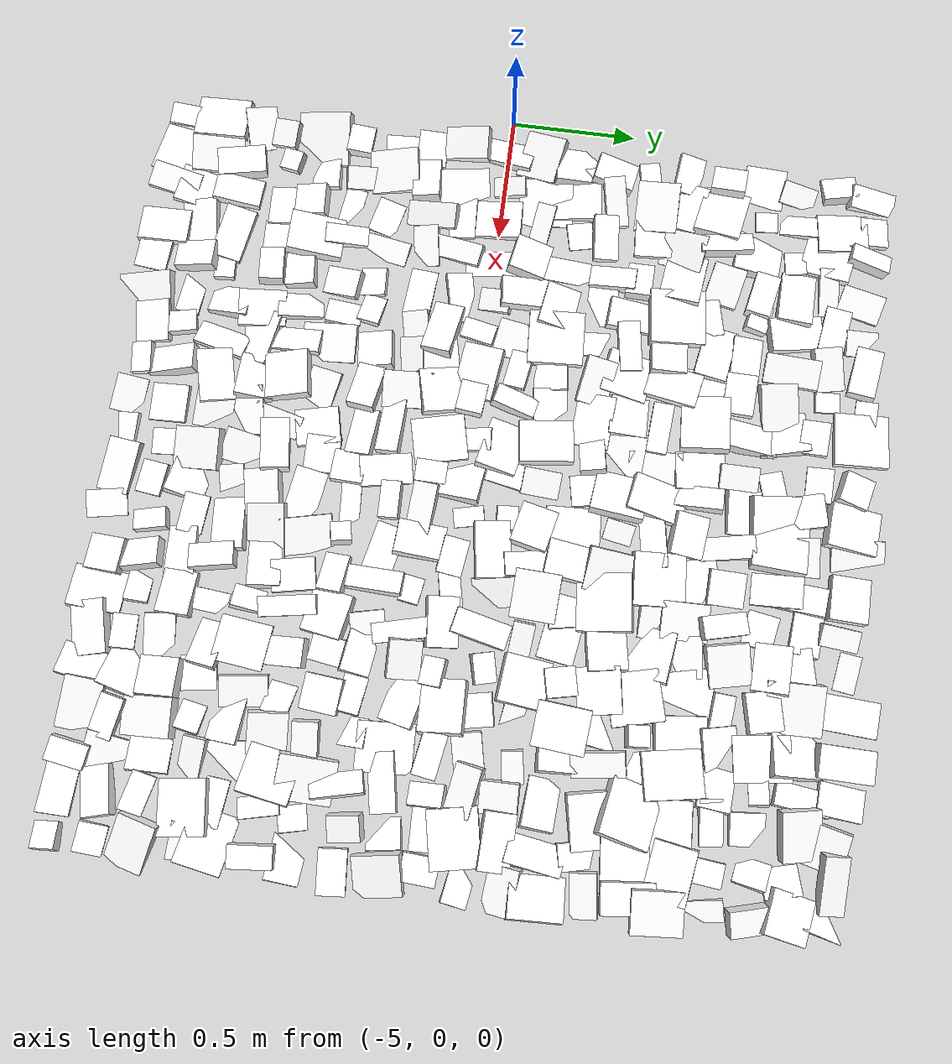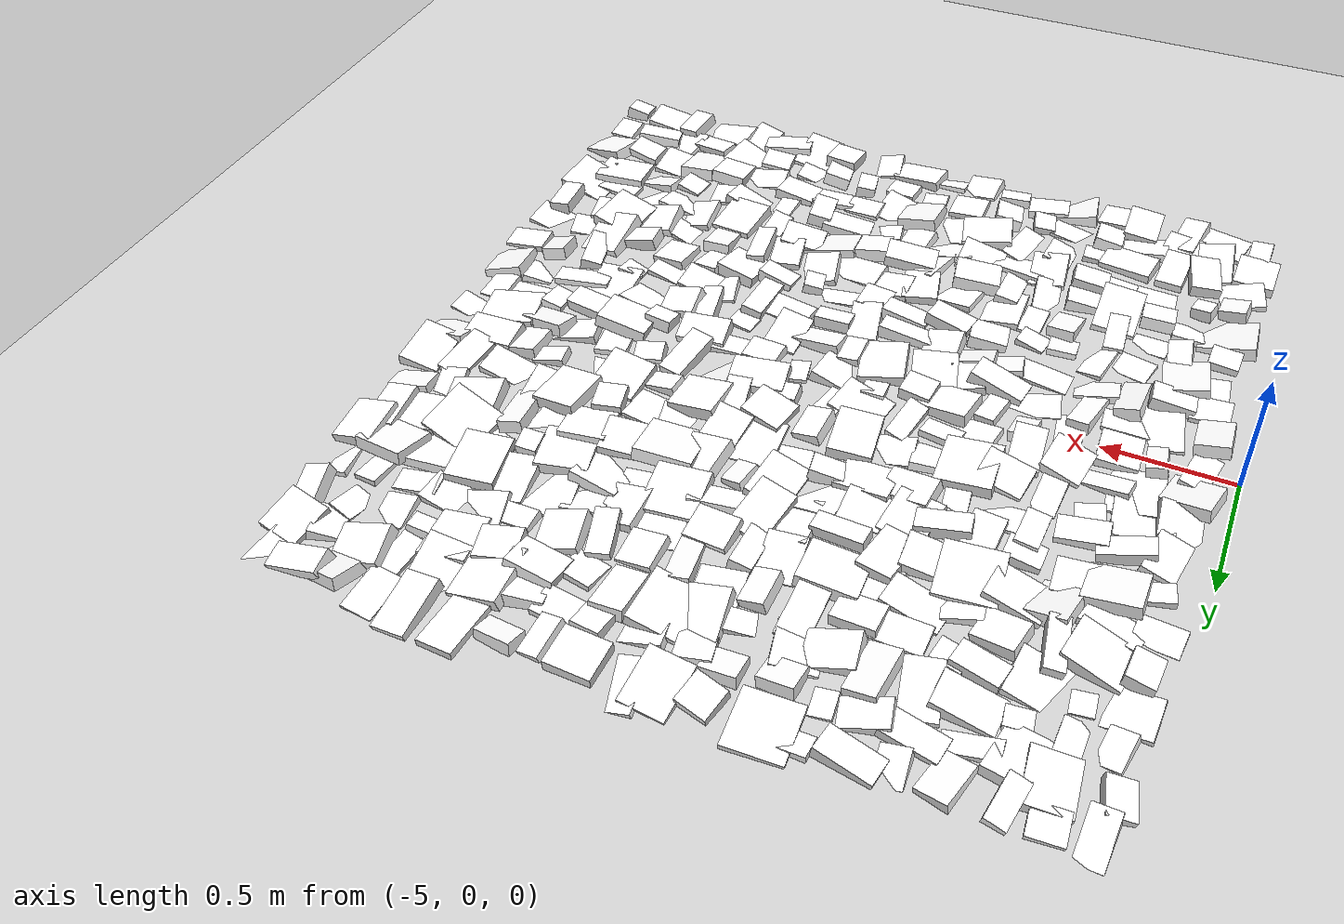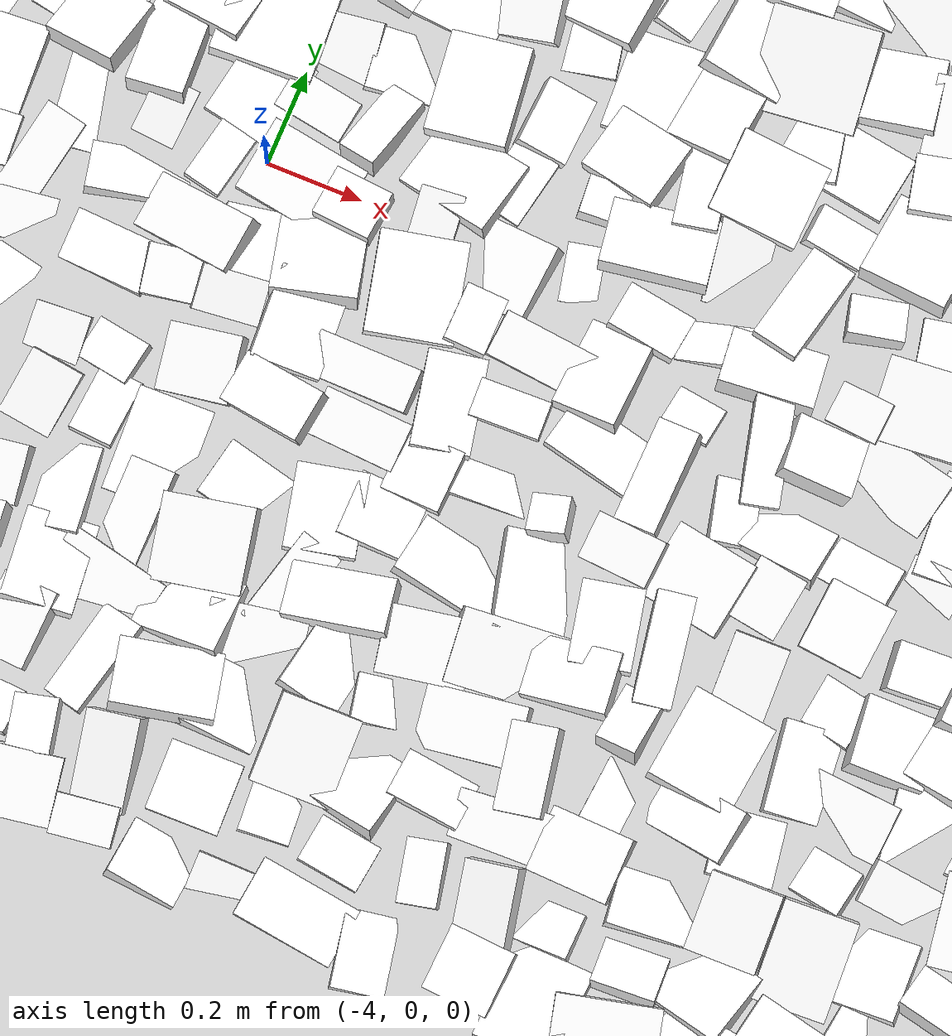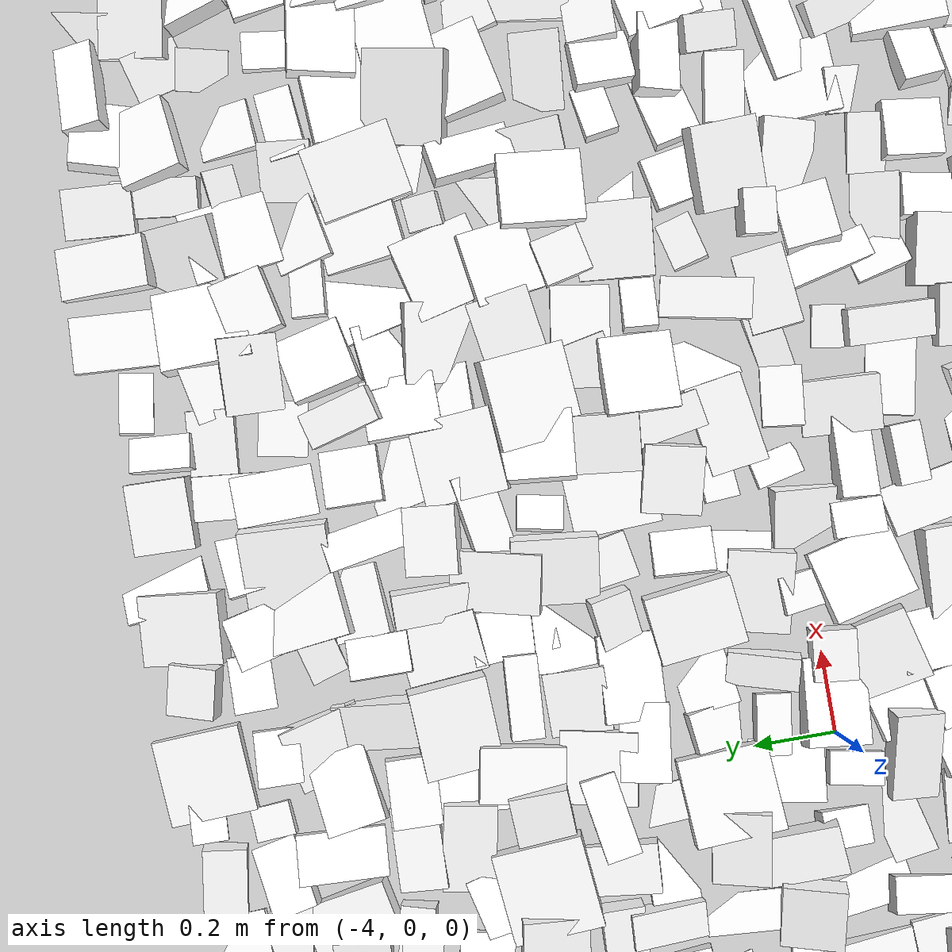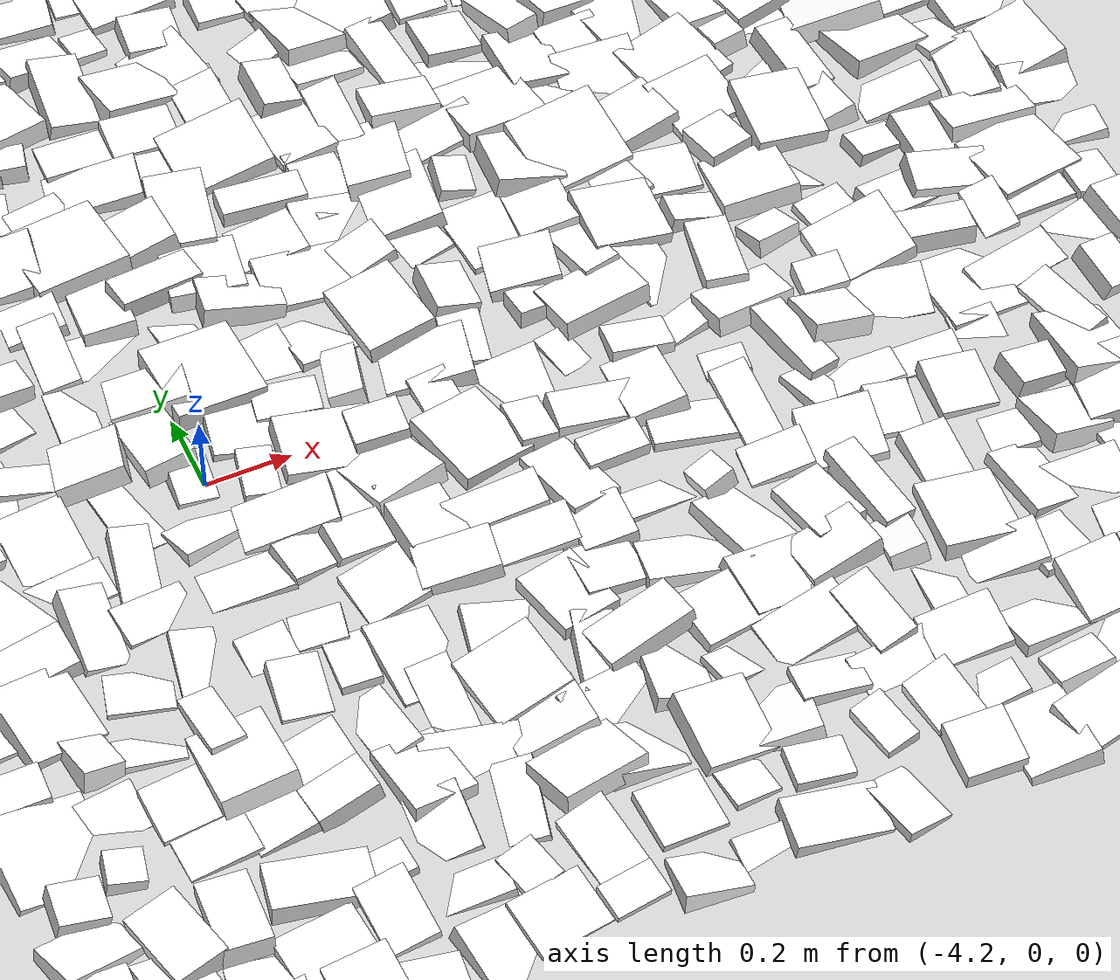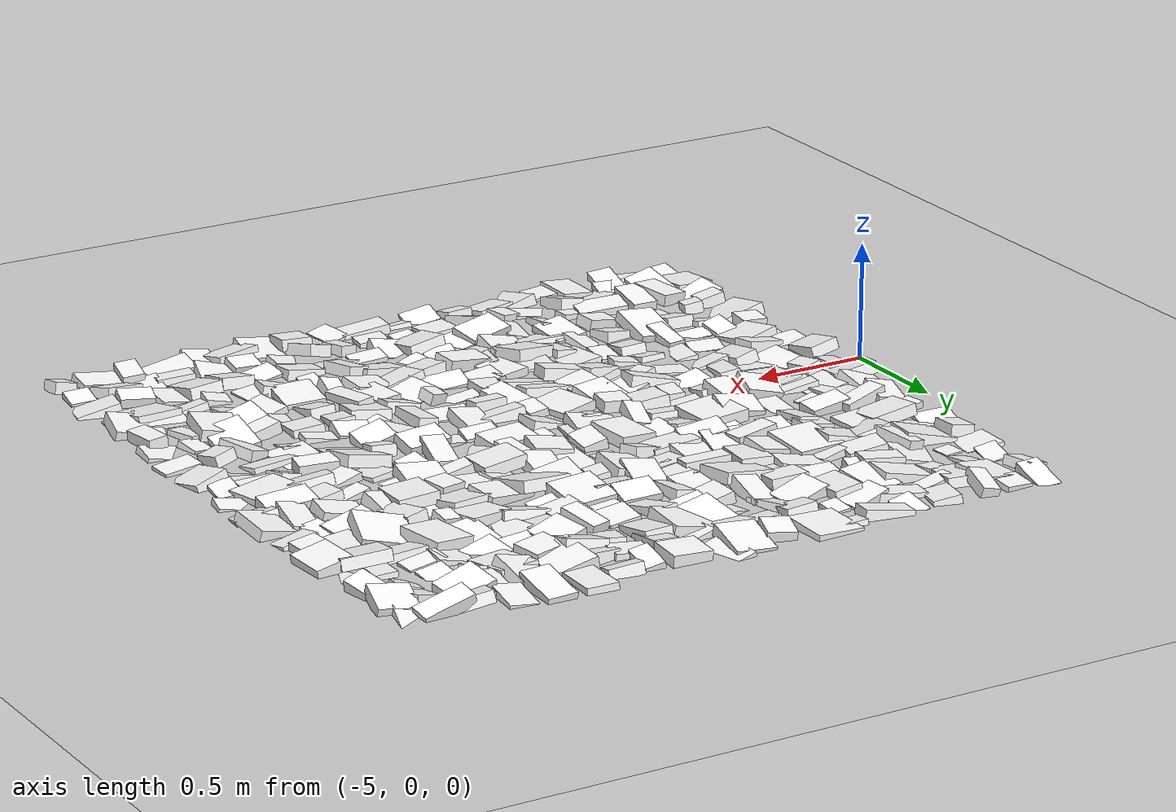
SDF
<sdf version="1.7">
  <world name="default">

    <!-- Need to be able to manipulate model state -->
    <plugin name="gazebo_ros_state" filename="libgazebo_ros_state.so">
      <ros>
        <namespace>/gazebo</namespace>
      </ros>

      <update_rate>1.0</update_rate>
    </plugin>

    <!-- Need to be able to manipulate model configuration -->
    <plugin name="gazebo_ros_properties" filename="libgazebo_ros_properties.so">
      <ros>
        <namespace>/gazebo</namespace>
      </ros>

      <update_rate>1.0</update_rate>
    </plugin>

    <physics type="ode">
    <max_step_size>0.001</max_step_size>
    <real_time_factor>1.0</real_time_factor>
    <real_time_update_rate>1000</real_time_update_rate>
    <gravity>0 0 -9.81</gravity>
        <ode>
            <solver>
            <type>quick</type>
            <iters>50</iters>
            <sor>1.3</sor>
            </solver>
            <constraints>
            <cfm>0.0</cfm>
            <erp>0.2</erp>
            <contact_max_correcting_vel>10.0</contact_max_correcting_vel>
            <contact_surface_layer>0.001</contact_surface_layer>
            </constraints>
        </ode>
    </physics>

    <scene>
    <sky>
        <clouds>
            <speed>12</speed>
        </clouds>
    </sky>
    </scene>
    <!-- A global light source -->
    <include>
        <uri>model://sun</uri>
    </include>
    <!-- A ground plane -->
    <include>
        <uri>model://ground_plane</uri>
    </include>
    <model name="static_environment">
  <static>true</static>
  <link name="region_0">
    <pose>-2.014062118704401 1.5020243571643022 -0.024271251875729018 0.20937350404994248 0.20035742705850612 2.9082107138131725</pose>
    <collision name="region_0_collision">
      <geometry>
        <box>
          <size>0.09812442635695086 0.18600745447731074 0.05</size>
        </box>
      </geometry>
      <surface>
        <friction>
          <ode>
            <mu>1.0</mu>
            <mu2>1.0</mu2>
          </ode>
        </friction>
      </surface>
    </collision>
    <visual name="region_0_visual">
      <geometry>
        <box>
          <size>0.09812442635695086 0.18600745447731074 0.05</size>
        </box>
      </geometry>
      <material>
        <ambient>1.0 1.0 1.0 1.0</ambient>
        <diffuse>1.0 1.0 1.0 1.0</diffuse>
      </material>
    </visual>
  </link>
  <link name="region_1">
    <pose>-2.162831317794181 1.506378882661463 0.02221125680265211 0.17636777055464248 -0.24887038324074323 3.1521130136101467</pose>
    <collision name="region_1_collision">
      <geometry>
        <box>
          <size>0.21854240044126752 0.09558139820341147 0.05</size>
        </box>
      </geometry>
      <surface>
        <friction>
          <ode>
            <mu>1.0</mu>
            <mu2>1.0</mu2>
          </ode>
        </friction>
      </surface>
    </collision>
    <visual name="region_1_visual">
      <geometry>
        <box>
          <size>0.21854240044126752 0.09558139820341147 0.05</size>
        </box>
      </geometry>
      <material>
        <ambient>1.0 1.0 1.0 1.0</ambient>
        <diffuse>1.0 1.0 1.0 1.0</diffuse>
      </material>
    </visual>
  </link>
  <link name="region_2">
    <pose>-2.283772969083941 1.4796707948259167 0.013228022516943938 -0.23959510102396692 -0.18239491081544157 2.949636508700845</pose>
    <collision name="region_2_collision">
      <geometry>
        <box>
          <size>0.15780564498968497 0.14780661204940646 0.05</size>
        </box>
      </geometry>
      <surface>
        <friction>
          <ode>
            <mu>1.0</mu>
            <mu2>1.0</mu2>
          </ode>
        </friction>
      </surface>
    </collision>
    <visual name="region_2_visual">
      <geometry>
        <box>
          <size>0.15780564498968497 0.14780661204940646 0.05</size>
        </box>
      </geometry>
      <material>
        <ambient>1.0 1.0 1.0 1.0</ambient>
        <diffuse>1.0 1.0 1.0 1.0</diffuse>
      </material>
    </visual>
  </link>
  <link name="region_3">
    <pose>-2.4515872309889537 1.519011785559593 -0.010520660823472323 0.11656298880633531 0.10131117762762315 3.0552847381317116</pose>
    <collision name="region_3_collision">
      <geometry>
        <box>
          <size>0.12148463767350438 0.1757178967818004 0.05</size>
        </box>
      </geometry>
      <surface>
        <friction>
          <ode>
            <mu>1.0</mu>
            <mu2>1.0</mu2>
          </ode>
        </friction>
      </surface>
    </collision>
    <visual name="region_3_visual">
      <geometry>
        <box>
          <size>0.12148463767350438 0.1757178967818004 0.05</size>
        </box>
      </geometry>
      <material>
        <ambient>1.0 1.0 1.0 1.0</ambient>
        <diffuse>1.0 1.0 1.0 1.0</diffuse>
      </material>
    </visual>
  </link>
  <link name="region_4">
    <pose>-2.5923860903359817 1.5270743971972522 0.01337378253102444 0.16250462660738674 -0.04667984909666917 3.117154205710657</pose>
    <collision name="region_4_collision">
      <geometry>
        <box>
          <size>0.12519712936590835 0.22170871185247784 0.05</size>
        </box>
      </geometry>
      <surface>
        <friction>
          <ode>
            <mu>1.0</mu>
            <mu2>1.0</mu2>
          </ode>
        </friction>
      </surface>
    </collision>
    <visual name="region_4_visual">
      <geometry>
        <box>
          <size>0.12519712936590835 0.22170871185247784 0.05</size>
        </box>
      </geometry>
      <material>
        <ambient>1.0 1.0 1.0 1.0</ambient>
        <diffuse>1.0 1.0 1.0 1.0</diffuse>
      </material>
    </visual>
  </link>
  <link name="region_5">
    <pose>-2.769207165839978 1.5278252979354006 -0.004037486487044689 -0.03797377672450064 -0.018425565136327038 3.0783615744119577</pose>
    <collision name="region_5_collision">
      <geometry>
        <box>
          <size>0.13509474410425104 0.22427072405078377 0.05</size>
        </box>
      </geometry>
      <surface>
        <friction>
          <ode>
            <mu>1.0</mu>
            <mu2>1.0</mu2>
          </ode>
        </friction>
      </surface>
    </collision>
    <visual name="region_5_visual">
      <geometry>
        <box>
          <size>0.13509474410425104 0.22427072405078377 0.05</size>
        </box>
      </geometry>
      <material>
        <ambient>1.0 1.0 1.0 1.0</ambient>
        <diffuse>1.0 1.0 1.0 1.0</diffuse>
      </material>
    </visual>
  </link>
  <link name="region_6">
    <pose>-2.9248046555684892 1.5140346236806959 0.006809999691643379 -0.23604610556923372 -0.0999149700880067 3.001926260414443</pose>
    <collision name="region_6_collision">
      <geometry>
        <box>
          <size>0.14482621502587664 0.08027523922062071 0.05</size>
        </box>
      </geometry>
      <surface>
        <friction>
          <ode>
            <mu>1.0</mu>
            <mu2>1.0</mu2>
          </ode>
        </friction>
      </surface>
    </collision>
    <visual name="region_6_visual">
      <geometry>
        <box>
          <size>0.14482621502587664 0.08027523922062071 0.05</size>
        </box>
      </geometry>
      <material>
        <ambient>1.0 1.0 1.0 1.0</ambient>
        <diffuse>1.0 1.0 1.0 1.0</diffuse>
      </material>
    </visual>
  </link>
  <link name="region_7">
    <pose>-3.0548788356708716 1.472990404820162 0.003620225776480468 0.15175832533868816 -0.1931991402300915 3.0300586072125983</pose>
    <collision name="region_7_collision">
      <geometry>
        <box>
          <size>0.08325299900103002 0.1534869106167438 0.05</size>
        </box>
      </geometry>
      <surface>
        <friction>
          <ode>
            <mu>1.0</mu>
            <mu2>1.0</mu2>
          </ode>
        </friction>
      </surface>
    </collision>
    <visual name="region_7_visual">
      <geometry>
        <box>
          <size>0.08325299900103002 0.1534869106167438 0.05</size>
        </box>
      </geometry>
      <material>
        <ambient>1.0 1.0 1.0 1.0</ambient>
        <diffuse>1.0 1.0 1.0 1.0</diffuse>
      </material>
    </visual>
  </link>
  <link name="region_8">
    <pose>-3.199467649924611 1.497797593473034 0.01973715369639454 0.05288884656779247 0.05167780158377683 3.1134359280956345</pose>
    <collision name="region_8_collision">
      <geometry>
        <box>
          <size>0.17125171375281345 0.14891059581547617 0.05</size>
        </box>
      </geometry>
      <surface>
        <friction>
          <ode>
            <mu>1.0</mu>
            <mu2>1.0</mu2>
          </ode>
        </friction>
      </surface>
    </collision>
    <visual name="region_8_visual">
      <geometry>
        <box>
          <size>0.17125171375281345 0.14891059581547617 0.05</size>
        </box>
      </geometry>
      <material>
        <ambient>1.0 1.0 1.0 1.0</ambient>
        <diffuse>1.0 1.0 1.0 1.0</diffuse>
      </material>
    </visual>
  </link>
  <link name="region_9">
    <pose>-3.3673509845132346 1.5267999636369054 -0.021326497802886726 0.047576228318045255 -0.2344244645741168 3.224128716265395</pose>
    <collision name="region_9_collision">
      <geometry>
        <box>
          <size>0.14700701749903353 0.20826712908445394 0.05</size>
        </box>
      </geometry>
      <surface>
        <friction>
          <ode>
            <mu>1.0</mu>
            <mu2>1.0</mu2>
          </ode>
        </friction>
      </surface>
    </collision>
    <visual name="region_9_visual">
      <geometry>
        <box>
          <size>0.14700701749903353 0.20826712908445394 0.05</size>
        </box>
      </geometry>
      <material>
        <ambient>1.0 1.0 1.0 1.0</ambient>
        <diffuse>1.0 1.0 1.0 1.0</diffuse>
      </material>
    </visual>
  </link>
  <link name="region_10">
    <pose>-3.473362750436614 1.4968765971506124 0.008497881621787752 0.21216534981599583 0.05971173338387331 3.052792866354407</pose>
    <collision name="region_10_collision">
      <geometry>
        <box>
          <size>0.1706078242711454 0.20436977434464226 0.05</size>
        </box>
      </geometry>
      <surface>
        <friction>
          <ode>
            <mu>1.0</mu>
            <mu2>1.0</mu2>
          </ode>
        </friction>
      </surface>
    </collision>
    <visual name="region_10_visual">
      <geometry>
        <box>
          <size>0.1706078242711454 0.20436977434464226 0.05</size>
        </box>
      </geometry>
      <material>
        <ambient>1.0 1.0 1.0 1.0</ambient>
        <diffuse>1.0 1.0 1.0 1.0</diffuse>
      </material>
    </visual>
  </link>
  <link name="region_11">
    <pose>-3.6224159671087985 1.4945103725620028 0.022327791118140157 0.1785952794159718 0.0944638330162288 2.89314398437617</pose>
    <collision name="region_11_collision">
      <geometry>
        <box>
          <size>0.12292144664003718 0.11871850275099793 0.05</size>
        </box>
      </geometry>
      <surface>
        <friction>
          <ode>
            <mu>1.0</mu>
            <mu2>1.0</mu2>
          </ode>
        </friction>
      </surface>
    </collision>
    <visual name="region_11_visual">
      <geometry>
        <box>
          <size>0.12292144664003718 0.11871850275099793 0.05</size>
        </box>
      </geometry>
      <material>
        <ambient>1.0 1.0 1.0 1.0</ambient>
        <diffuse>1.0 1.0 1.0 1.0</diffuse>
      </material>
    </visual>
  </link>
  <link name="region_12">
    <pose>-3.829506450537181 1.5087423389290238 -0.005739150987846293 0.04787094714345319 0.05540352775220464 3.191309594198669</pose>
    <collision name="region_12_collision">
      <geometry>
        <box>
          <size>0.2100155249485474 0.2129797306443485 0.05</size>
        </box>
      </geometry>
      <surface>
        <friction>
          <ode>
            <mu>1.0</mu>
            <mu2>1.0</mu2>
          </ode>
        </friction>
      </surface>
    </collision>
    <visual name="region_12_visual">
      <geometry>
        <box>
          <size>0.2100155249485474 0.2129797306443485 0.05</size>
        </box>
      </geometry>
      <material>
        <ambient>1.0 1.0 1.0 1.0</ambient>
        <diffuse>1.0 1.0 1.0 1.0</diffuse>
      </material>
    </visual>
  </link>
  <link name="region_13">
    <pose>-3.931816957192507 1.5248667110693215 -0.015266268547873147 -0.14469618057355804 -0.061279608819677645 3.092923605086337</pose>
    <collision name="region_13_collision">
      <geometry>
        <box>
          <size>0.12184259952648774 0.0854810512144632 0.05</size>
        </box>
      </geometry>
      <surface>
        <friction>
          <ode>
            <mu>1.0</mu>
            <mu2>1.0</mu2>
          </ode>
        </friction>
      </surface>
    </collision>
    <visual name="region_13_visual">
      <geometry>
        <box>
          <size>0.12184259952648774 0.0854810512144632 0.05</size>
        </box>
      </geometry>
      <material>
        <ambient>1.0 1.0 1.0 1.0</ambient>
        <diffuse>1.0 1.0 1.0 1.0</diffuse>
      </material>
    </visual>
  </link>
  <link name="region_14">
    <pose>-4.104720120952562 1.509072116500127 0.000582147639666554 -0.08308375724269845 0.13923671692967232 2.9592175672838055</pose>
    <collision name="region_14_collision">
      <geometry>
        <box>
          <size>0.20777665416491922 0.10532315150551087 0.05</size>
        </box>
      </geometry>
      <surface>
        <friction>
          <ode>
            <mu>1.0</mu>
            <mu2>1.0</mu2>
          </ode>
        </friction>
      </surface>
    </collision>
    <visual name="region_14_visual">
      <geometry>
        <box>
          <size>0.20777665416491922 0.10532315150551087 0.05</size>
        </box>
      </geometry>
      <material>
        <ambient>1.0 1.0 1.0 1.0</ambient>
        <diffuse>1.0 1.0 1.0 1.0</diffuse>
      </material>
    </visual>
  </link>
  <link name="region_15">
    <pose>-4.232650342042872 1.4854369557738816 -0.01952572893342406 0.21533800719094315 -0.1868063581127013 3.194002695181782</pose>
    <collision name="region_15_collision">
      <geometry>
        <box>
          <size>0.10375661583833336 0.1353883721843947 0.05</size>
        </box>
      </geometry>
      <surface>
        <friction>
          <ode>
            <mu>1.0</mu>
            <mu2>1.0</mu2>
          </ode>
        </friction>
      </surface>
    </collision>
    <visual name="region_15_visual">
      <geometry>
        <box>
          <size>0.10375661583833336 0.1353883721843947 0.05</size>
        </box>
      </geometry>
      <material>
        <ambient>1.0 1.0 1.0 1.0</ambient>
        <diffuse>1.0 1.0 1.0 1.0</diffuse>
      </material>
    </visual>
  </link>
  <link name="region_16">
    <pose>-4.390292452083434 1.4742859318742112 -0.007227853759948867 -0.08263796126161371 -0.1612468163916323 2.8955016698911407</pose>
    <collision name="region_16_collision">
      <geometry>
        <box>
          <size>0.11851829048817407 0.16897940878838555 0.05</size>
        </box>
      </geometry>
      <surface>
        <friction>
          <ode>
            <mu>1.0</mu>
            <mu2>1.0</mu2>
          </ode>
        </friction>
      </surface>
    </collision>
    <visual name="region_16_visual">
      <geometry>
        <box>
          <size>0.11851829048817407 0.16897940878838555 0.05</size>
        </box>
      </geometry>
      <material>
        <ambient>1.0 1.0 1.0 1.0</ambient>
        <diffuse>1.0 1.0 1.0 1.0</diffuse>
      </material>
    </visual>
  </link>
  <link name="region_17">
    <pose>-4.574782697448905 1.4891763544308383 0.02343091644849834 0.18679127561850645 0.20639199708541217 2.976449130465943</pose>
    <collision name="region_17_collision">
      <geometry>
        <box>
          <size>0.07656576031420817 0.1646188206958685 0.05</size>
        </box>
      </geometry>
      <surface>
        <friction>
          <ode>
            <mu>1.0</mu>
            <mu2>1.0</mu2>
          </ode>
        </friction>
      </surface>
    </collision>
    <visual name="region_17_visual">
      <geometry>
        <box>
          <size>0.07656576031420817 0.1646188206958685 0.05</size>
        </box>
      </geometry>
      <material>
        <ambient>1.0 1.0 1.0 1.0</ambient>
        <diffuse>1.0 1.0 1.0 1.0</diffuse>
      </material>
    </visual>
  </link>
  <link name="region_18">
    <pose>-4.7004037098366815 1.5028867628276785 -0.004727280645749489 0.12120515658839681 0.07186650788260135 3.2211716753573354</pose>
    <collision name="region_18_collision">
      <geometry>
        <box>
          <size>0.12252118510335676 0.1112670353571094 0.05</size>
        </box>
      </geometry>
      <surface>
        <friction>
          <ode>
            <mu>1.0</mu>
            <mu2>1.0</mu2>
          </ode>
        </friction>
      </surface>
    </collision>
    <visual name="region_18_visual">
      <geometry>
        <box>
          <size>0.12252118510335676 0.1112670353571094 0.05</size>
        </box>
      </geometry>
      <material>
        <ambient>1.0 1.0 1.0 1.0</ambient>
        <diffuse>1.0 1.0 1.0 1.0</diffuse>
      </material>
    </visual>
  </link>
  <link name="region_19">
    <pose>-4.841374151645391 1.4881579180459148 -0.006208605234027005 0.24431393258757367 -0.07770252986004095 3.063222500325638</pose>
    <collision name="region_19_collision">
      <geometry>
        <box>
          <size>0.09738355279015998 0.18698756847086337 0.05</size>
        </box>
      </geometry>
      <surface>
        <friction>
          <ode>
            <mu>1.0</mu>
            <mu2>1.0</mu2>
          </ode>
        </friction>
      </surface>
    </collision>
    <visual name="region_19_visual">
      <geometry>
        <box>
          <size>0.09738355279015998 0.18698756847086337 0.05</size>
        </box>
      </geometry>
      <material>
        <ambient>1.0 1.0 1.0 1.0</ambient>
        <diffuse>1.0 1.0 1.0 1.0</diffuse>
      </material>
    </visual>
  </link>
  <link name="region_20">
    <pose>-2.0290737123224836 1.3544659618949602 0.013883972603981082 0.2249410385688751 0.10149108655000566 2.9496028667239127</pose>
    <collision name="region_20_collision">
      <geometry>
        <box>
          <size>0.16704801815626547 0.167758906910901 0.05</size>
        </box>
      </geometry>
      <surface>
        <friction>
          <ode>
            <mu>1.0</mu>
            <mu2>1.0</mu2>
          </ode>
        </friction>
      </surface>
    </collision>
    <visual name="region_20_visual">
      <geometry>
        <box>
          <size>0.16704801815626547 0.167758906910901 0.05</size>
        </box>
      </geometry>
      <material>
        <ambient>1.0 1.0 1.0 1.0</ambient>
        <diffuse>1.0 1.0 1.0 1.0</diffuse>
      </material>
    </visual>
  </link>
  <link name="region_21">
    <pose>-2.141953024207276 1.3257421074516773 -0.005484539528843396 -0.08901620623463669 0.23566264696378902 3.3760911898057206</pose>
    <collision name="region_21_collision">
      <geometry>
        <box>
          <size>0.11199022171846364 0.13784080210763588 0.05</size>
        </box>
      </geometry>
      <surface>
        <friction>
          <ode>
            <mu>1.0</mu>
            <mu2>1.0</mu2>
          </ode>
        </friction>
      </surface>
    </collision>
    <visual name="region_21_visual">
      <geometry>
        <box>
          <size>0.11199022171846364 0.13784080210763588 0.05</size>
        </box>
      </geometry>
      <material>
        <ambient>1.0 1.0 1.0 1.0</ambient>
        <diffuse>1.0 1.0 1.0 1.0</diffuse>
      </material>
    </visual>
  </link>
  <link name="region_22">
    <pose>-2.3200061189991206 1.3769906845053326 0.02109129773419422 0.19128535016952536 -0.22448069998746467 3.2789701077173645</pose>
    <collision name="region_22_collision">
      <geometry>
        <box>
          <size>0.1865126952338271 0.15265339425532023 0.05</size>
        </box>
      </geometry>
      <surface>
        <friction>
          <ode>
            <mu>1.0</mu>
            <mu2>1.0</mu2>
          </ode>
        </friction>
      </surface>
    </collision>
    <visual name="region_22_visual">
      <geometry>
        <box>
          <size>0.1865126952338271 0.15265339425532023 0.05</size>
        </box>
      </geometry>
      <material>
        <ambient>1.0 1.0 1.0 1.0</ambient>
        <diffuse>1.0 1.0 1.0 1.0</diffuse>
      </material>
    </visual>
  </link>
  <link name="region_23">
    <pose>-2.4446017266397075 1.3793270737823784 -0.003566932174191108 0.06492498947557018 0.1381406671326596 3.021408743883807</pose>
    <collision name="region_23_collision">
      <geometry>
        <box>
          <size>0.09088427286351888 0.21080937999444802 0.05</size>
        </box>
      </geometry>
      <surface>
        <friction>
          <ode>
            <mu>1.0</mu>
            <mu2>1.0</mu2>
          </ode>
        </friction>
      </surface>
    </collision>
    <visual name="region_23_visual">
      <geometry>
        <box>
          <size>0.09088427286351888 0.21080937999444802 0.05</size>
        </box>
      </geometry>
      <material>
        <ambient>1.0 1.0 1.0 1.0</ambient>
        <diffuse>1.0 1.0 1.0 1.0</diffuse>
      </material>
    </visual>
  </link>
  <link name="region_24">
    <pose>-2.5985965995793263 1.3455246946917856 0.001550151890214107 0.22298906133503016 0.24963683107212142 3.226961794424131</pose>
    <collision name="region_24_collision">
      <geometry>
        <box>
          <size>0.1708369603893236 0.19901999627410133 0.05</size>
        </box>
      </geometry>
      <surface>
        <friction>
          <ode>
            <mu>1.0</mu>
            <mu2>1.0</mu2>
          </ode>
        </friction>
      </surface>
    </collision>
    <visual name="region_24_visual">
      <geometry>
        <box>
          <size>0.1708369603893236 0.19901999627410133 0.05</size>
        </box>
      </geometry>
      <material>
        <ambient>1.0 1.0 1.0 1.0</ambient>
        <diffuse>1.0 1.0 1.0 1.0</diffuse>
      </material>
    </visual>
  </link>
  <link name="region_25">
    <pose>-2.7713814097055436 1.3216467055907886 0.012322138061207369 0.05829403702023506 -0.20039765036196355 3.152451337678578</pose>
    <collision name="region_25_collision">
      <geometry>
        <box>
          <size>0.1934364205563424 0.2222381332040455 0.05</size>
        </box>
      </geometry>
      <surface>
        <friction>
          <ode>
            <mu>1.0</mu>
            <mu2>1.0</mu2>
          </ode>
        </friction>
      </surface>
    </collision>
    <visual name="region_25_visual">
      <geometry>
        <box>
          <size>0.1934364205563424 0.2222381332040455 0.05</size>
        </box>
      </geometry>
      <material>
        <ambient>1.0 1.0 1.0 1.0</ambient>
        <diffuse>1.0 1.0 1.0 1.0</diffuse>
      </material>
    </visual>
  </link>
  <link name="region_26">
    <pose>-2.9149686044343603 1.330904333247847 0.004191153348755611 -0.17304069632451752 0.10586379385263428 3.320876202726018</pose>
    <collision name="region_26_collision">
      <geometry>
        <box>
          <size>0.15111479722179935 0.11785395388839123 0.05</size>
        </box>
      </geometry>
      <surface>
        <friction>
          <ode>
            <mu>1.0</mu>
            <mu2>1.0</mu2>
          </ode>
        </friction>
      </surface>
    </collision>
    <visual name="region_26_visual">
      <geometry>
        <box>
          <size>0.15111479722179935 0.11785395388839123 0.05</size>
        </box>
      </geometry>
      <material>
        <ambient>1.0 1.0 1.0 1.0</ambient>
        <diffuse>1.0 1.0 1.0 1.0</diffuse>
      </material>
    </visual>
  </link>
  <link name="region_27">
    <pose>-3.0560529507349563 1.350878241987214 -0.007789788959760315 0.022801163499002908 0.0930583674152155 3.0413464474967067</pose>
    <collision name="region_27_collision">
      <geometry>
        <box>
          <size>0.17796620561972773 0.11476944132182873 0.05</size>
        </box>
      </geometry>
      <surface>
        <friction>
          <ode>
            <mu>1.0</mu>
            <mu2>1.0</mu2>
          </ode>
        </friction>
      </surface>
    </collision>
    <visual name="region_27_visual">
      <geometry>
        <box>
          <size>0.17796620561972773 0.11476944132182873 0.05</size>
        </box>
      </geometry>
      <material>
        <ambient>1.0 1.0 1.0 1.0</ambient>
        <diffuse>1.0 1.0 1.0 1.0</diffuse>
      </material>
    </visual>
  </link>
  <link name="region_28">
    <pose>-3.183323975746301 1.3226147355502407 0.007274268477214019 -0.1859034487469569 0.023826251471153748 3.0372617233279735</pose>
    <collision name="region_28_collision">
      <geometry>
        <box>
          <size>0.10730367351970604 0.19324631848978693 0.05</size>
        </box>
      </geometry>
      <surface>
        <friction>
          <ode>
            <mu>1.0</mu>
            <mu2>1.0</mu2>
          </ode>
        </friction>
      </surface>
    </collision>
    <visual name="region_28_visual">
      <geometry>
        <box>
          <size>0.10730367351970604 0.19324631848978693 0.05</size>
        </box>
      </geometry>
      <material>
        <ambient>1.0 1.0 1.0 1.0</ambient>
        <diffuse>1.0 1.0 1.0 1.0</diffuse>
      </material>
    </visual>
  </link>
  <link name="region_29">
    <pose>-3.326024197177781 1.3406444253104646 -0.018395734747924566 -0.021208525792619837 -0.20778109596812883 3.2616132966222233</pose>
    <collision name="region_29_collision">
      <geometry>
        <box>
          <size>0.19887676742959542 0.0896028557916878 0.05</size>
        </box>
      </geometry>
      <surface>
        <friction>
          <ode>
            <mu>1.0</mu>
            <mu2>1.0</mu2>
          </ode>
        </friction>
      </surface>
    </collision>
    <visual name="region_29_visual">
      <geometry>
        <box>
          <size>0.19887676742959542 0.0896028557916878 0.05</size>
        </box>
      </geometry>
      <material>
        <ambient>1.0 1.0 1.0 1.0</ambient>
        <diffuse>1.0 1.0 1.0 1.0</diffuse>
      </material>
    </visual>
  </link>
  <link name="region_30">
    <pose>-3.5234894314026612 1.3313077117943863 0.0009624402382346839 -0.19368886047820688 -0.008037205267920233 3.3572441885021815</pose>
    <collision name="region_30_collision">
      <geometry>
        <box>
          <size>0.12956067281717265 0.12503417433243483 0.05</size>
        </box>
      </geometry>
      <surface>
        <friction>
          <ode>
            <mu>1.0</mu>
            <mu2>1.0</mu2>
          </ode>
        </friction>
      </surface>
    </collision>
    <visual name="region_30_visual">
      <geometry>
        <box>
          <size>0.12956067281717265 0.12503417433243483 0.05</size>
        </box>
      </geometry>
      <material>
        <ambient>1.0 1.0 1.0 1.0</ambient>
        <diffuse>1.0 1.0 1.0 1.0</diffuse>
      </material>
    </visual>
  </link>
  <link name="region_31">
    <pose>-3.631545388154425 1.3597970003477404 0.005671755726946132 -0.18805892253738415 -0.0742292266154223 3.128049900804863</pose>
    <collision name="region_31_collision">
      <geometry>
        <box>
          <size>0.134828279164239 0.10205879768003219 0.05</size>
        </box>
      </geometry>
      <surface>
        <friction>
          <ode>
            <mu>1.0</mu>
            <mu2>1.0</mu2>
          </ode>
        </friction>
      </surface>
    </collision>
    <visual name="region_31_visual">
      <geometry>
        <box>
          <size>0.134828279164239 0.10205879768003219 0.05</size>
        </box>
      </geometry>
      <material>
        <ambient>1.0 1.0 1.0 1.0</ambient>
        <diffuse>1.0 1.0 1.0 1.0</diffuse>
      </material>
    </visual>
  </link>
  <link name="region_32">
    <pose>-3.8162620925565705 1.3287364593638857 0.011471256058425666 -0.18849419529501205 -0.09011101296383955 3.0873298103264855</pose>
    <collision name="region_32_collision">
      <geometry>
        <box>
          <size>0.13175779509372743 0.10828854993342196 0.05</size>
        </box>
      </geometry>
      <surface>
        <friction>
          <ode>
            <mu>1.0</mu>
            <mu2>1.0</mu2>
          </ode>
        </friction>
      </surface>
    </collision>
    <visual name="region_32_visual">
      <geometry>
        <box>
          <size>0.13175779509372743 0.10828854993342196 0.05</size>
        </box>
      </geometry>
      <material>
        <ambient>1.0 1.0 1.0 1.0</ambient>
        <diffuse>1.0 1.0 1.0 1.0</diffuse>
      </material>
    </visual>
  </link>
  <link name="region_33">
    <pose>-3.9696359689108736 1.3663994010388827 -0.01304007294788302 0.12358504361697314 -0.07625290767795234 3.222106684100043</pose>
    <collision name="region_33_collision">
      <geometry>
        <box>
          <size>0.08069118291779179 0.09825169303578776 0.05</size>
        </box>
      </geometry>
      <surface>
        <friction>
          <ode>
            <mu>1.0</mu>
            <mu2>1.0</mu2>
          </ode>
        </friction>
      </surface>
    </collision>
    <visual name="region_33_visual">
      <geometry>
        <box>
          <size>0.08069118291779179 0.09825169303578776 0.05</size>
        </box>
      </geometry>
      <material>
        <ambient>1.0 1.0 1.0 1.0</ambient>
        <diffuse>1.0 1.0 1.0 1.0</diffuse>
      </material>
    </visual>
  </link>
  <link name="region_34">
    <pose>-4.104616422439544 1.36078717767662 0.005267264312795384 0.05434025327083025 -0.23025828911216734 3.3442179773874794</pose>
    <collision name="region_34_collision">
      <geometry>
        <box>
          <size>0.17318309997485784 0.10994639143384492 0.05</size>
        </box>
      </geometry>
      <surface>
        <friction>
          <ode>
            <mu>1.0</mu>
            <mu2>1.0</mu2>
          </ode>
        </friction>
      </surface>
    </collision>
    <visual name="region_34_visual">
      <geometry>
        <box>
          <size>0.17318309997485784 0.10994639143384492 0.05</size>
        </box>
      </geometry>
      <material>
        <ambient>1.0 1.0 1.0 1.0</ambient>
        <diffuse>1.0 1.0 1.0 1.0</diffuse>
      </material>
    </visual>
  </link>
  <link name="region_35">
    <pose>-4.2566006963007395 1.3746665404310054 -0.002393422491329074 -0.03335343160421389 0.10480613468346567 2.9719510689256263</pose>
    <collision name="region_35_collision">
      <geometry>
        <box>
          <size>0.20835845713492265 0.10180219240691474 0.05</size>
        </box>
      </geometry>
      <surface>
        <friction>
          <ode>
            <mu>1.0</mu>
            <mu2>1.0</mu2>
          </ode>
        </friction>
      </surface>
    </collision>
    <visual name="region_35_visual">
      <geometry>
        <box>
          <size>0.20835845713492265 0.10180219240691474 0.05</size>
        </box>
      </geometry>
      <material>
        <ambient>1.0 1.0 1.0 1.0</ambient>
        <diffuse>1.0 1.0 1.0 1.0</diffuse>
      </material>
    </visual>
  </link>
  <link name="region_36">
    <pose>-4.425429314786352 1.3427773074026264 -0.01253182385497399 0.006311672440037053 -0.17825987154003414 3.212327750667861</pose>
    <collision name="region_36_collision">
      <geometry>
        <box>
          <size>0.20456277387589664 0.07707938721720528 0.05</size>
        </box>
      </geometry>
      <surface>
        <friction>
          <ode>
            <mu>1.0</mu>
            <mu2>1.0</mu2>
          </ode>
        </friction>
      </surface>
    </collision>
    <visual name="region_36_visual">
      <geometry>
        <box>
          <size>0.20456277387589664 0.07707938721720528 0.05</size>
        </box>
      </geometry>
      <material>
        <ambient>1.0 1.0 1.0 1.0</ambient>
        <diffuse>1.0 1.0 1.0 1.0</diffuse>
      </material>
    </visual>
  </link>
  <link name="region_37">
    <pose>-4.563727412231285 1.3304996041569328 0.001321638220872317 -0.12907229563369083 -0.021892943865762793 2.94974100567346</pose>
    <collision name="region_37_collision">
      <geometry>
        <box>
          <size>0.15586582556977865 0.19948712636549865 0.05</size>
        </box>
      </geometry>
      <surface>
        <friction>
          <ode>
            <mu>1.0</mu>
            <mu2>1.0</mu2>
          </ode>
        </friction>
      </surface>
    </collision>
    <visual name="region_37_visual">
      <geometry>
        <box>
          <size>0.15586582556977865 0.19948712636549865 0.05</size>
        </box>
      </geometry>
      <material>
        <ambient>1.0 1.0 1.0 1.0</ambient>
        <diffuse>1.0 1.0 1.0 1.0</diffuse>
      </material>
    </visual>
  </link>
  <link name="region_38">
    <pose>-4.67513499138701 1.377287783219825 0.004076468464325696 0.0073451529404567895 0.13835810596043274 3.2275486630410373</pose>
    <collision name="region_38_collision">
      <geometry>
        <box>
          <size>0.16497099421032754 0.20049523390078045 0.05</size>
        </box>
      </geometry>
      <surface>
        <friction>
          <ode>
            <mu>1.0</mu>
            <mu2>1.0</mu2>
          </ode>
        </friction>
      </surface>
    </collision>
    <visual name="region_38_visual">
      <geometry>
        <box>
          <size>0.16497099421032754 0.20049523390078045 0.05</size>
        </box>
      </geometry>
      <material>
        <ambient>1.0 1.0 1.0 1.0</ambient>
        <diffuse>1.0 1.0 1.0 1.0</diffuse>
      </material>
    </visual>
  </link>
  <link name="region_39">
    <pose>-4.870611345780961 1.3542661527741293 0.0004551544841737039 -0.023110741954973257 0.24550563598248448 3.3415732761676304</pose>
    <collision name="region_39_collision">
      <geometry>
        <box>
          <size>0.09956813109950557 0.13913375327888608 0.05</size>
        </box>
      </geometry>
      <surface>
        <friction>
          <ode>
            <mu>1.0</mu>
            <mu2>1.0</mu2>
          </ode>
        </friction>
      </surface>
    </collision>
    <visual name="region_39_visual">
      <geometry>
        <box>
          <size>0.09956813109950557 0.13913375327888608 0.05</size>
        </box>
      </geometry>
      <material>
        <ambient>1.0 1.0 1.0 1.0</ambient>
        <diffuse>1.0 1.0 1.0 1.0</diffuse>
      </material>
    </visual>
  </link>
  <link name="region_40">
    <pose>-2.0011965568894343 1.2197174616367374 0.02147127254759825 0.16438255407813995 -0.23661648154048714 3.336635409121264</pose>
    <collision name="region_40_collision">
      <geometry>
        <box>
          <size>0.09771386688438115 0.1661512127754759 0.05</size>
        </box>
      </geometry>
      <surface>
        <friction>
          <ode>
            <mu>1.0</mu>
            <mu2>1.0</mu2>
          </ode>
        </friction>
      </surface>
    </collision>
    <visual name="region_40_visual">
      <geometry>
        <box>
          <size>0.09771386688438115 0.1661512127754759 0.05</size>
        </box>
      </geometry>
      <material>
        <ambient>1.0 1.0 1.0 1.0</ambient>
        <diffuse>1.0 1.0 1.0 1.0</diffuse>
      </material>
    </visual>
  </link>
  <link name="region_41">
    <pose>-2.157250745480871 1.2191107489353044 -0.015097345654019035 -0.16198697651086208 0.24621802649519625 2.9138493721720455</pose>
    <collision name="region_41_collision">
      <geometry>
        <box>
          <size>0.09964477198536101 0.12509584119083372 0.05</size>
        </box>
      </geometry>
      <surface>
        <friction>
          <ode>
            <mu>1.0</mu>
            <mu2>1.0</mu2>
          </ode>
        </friction>
      </surface>
    </collision>
    <visual name="region_41_visual">
      <geometry>
        <box>
          <size>0.09964477198536101 0.12509584119083372 0.05</size>
        </box>
      </geometry>
      <material>
        <ambient>1.0 1.0 1.0 1.0</ambient>
        <diffuse>1.0 1.0 1.0 1.0</diffuse>
      </material>
    </visual>
  </link>
  <link name="region_42">
    <pose>-2.316373019181766 1.186263963775373 -0.01963911366453627 0.15551033292483352 -0.12700995614709426 3.2084258578618283</pose>
    <collision name="region_42_collision">
      <geometry>
        <box>
          <size>0.12162733286844597 0.13673753567743377 0.05</size>
        </box>
      </geometry>
      <surface>
        <friction>
          <ode>
            <mu>1.0</mu>
            <mu2>1.0</mu2>
          </ode>
        </friction>
      </surface>
    </collision>
    <visual name="region_42_visual">
      <geometry>
        <box>
          <size>0.12162733286844597 0.13673753567743377 0.05</size>
        </box>
      </geometry>
      <material>
        <ambient>1.0 1.0 1.0 1.0</ambient>
        <diffuse>1.0 1.0 1.0 1.0</diffuse>
      </material>
    </visual>
  </link>
  <link name="region_43">
    <pose>-2.4650555598843757 1.2198361206765185 -0.004441983885261923 -0.2050427080077219 0.23736874992469142 3.2176811320159877</pose>
    <collision name="region_43_collision">
      <geometry>
        <box>
          <size>0.12906568352292772 0.07572940316619309 0.05</size>
        </box>
      </geometry>
      <surface>
        <friction>
          <ode>
            <mu>1.0</mu>
            <mu2>1.0</mu2>
          </ode>
        </friction>
      </surface>
    </collision>
    <visual name="region_43_visual">
      <geometry>
        <box>
          <size>0.12906568352292772 0.07572940316619309 0.05</size>
        </box>
      </geometry>
      <material>
        <ambient>1.0 1.0 1.0 1.0</ambient>
        <diffuse>1.0 1.0 1.0 1.0</diffuse>
      </material>
    </visual>
  </link>
  <link name="region_44">
    <pose>-2.573907455990942 1.2227509823361913 -0.004923734385228799 -0.11052516944853741 -0.009537501666561254 3.26991041568167</pose>
    <collision name="region_44_collision">
      <geometry>
        <box>
          <size>0.17342333794669912 0.21412744062600159 0.05</size>
        </box>
      </geometry>
      <surface>
        <friction>
          <ode>
            <mu>1.0</mu>
            <mu2>1.0</mu2>
          </ode>
        </friction>
      </surface>
    </collision>
    <visual name="region_44_visual">
      <geometry>
        <box>
          <size>0.17342333794669912 0.21412744062600159 0.05</size>
        </box>
      </geometry>
      <material>
        <ambient>1.0 1.0 1.0 1.0</ambient>
        <diffuse>1.0 1.0 1.0 1.0</diffuse>
      </material>
    </visual>
  </link>
  <link name="region_45">
    <pose>-2.74402371262897 1.208599276160545 0.023926492284110763 0.060769097616112155 -0.05329978420108494 3.3589191858535874</pose>
    <collision name="region_45_collision">
      <geometry>
        <box>
          <size>0.15133238702472265 0.1312909782964136 0.05</size>
        </box>
      </geometry>
      <surface>
        <friction>
          <ode>
            <mu>1.0</mu>
            <mu2>1.0</mu2>
          </ode>
        </friction>
      </surface>
    </collision>
    <visual name="region_45_visual">
      <geometry>
        <box>
          <size>0.15133238702472265 0.1312909782964136 0.05</size>
        </box>
      </geometry>
      <material>
        <ambient>1.0 1.0 1.0 1.0</ambient>
        <diffuse>1.0 1.0 1.0 1.0</diffuse>
      </material>
    </visual>
  </link>
  <link name="region_46">
    <pose>-2.902317784221777 1.2300108076123604 0.02317990920831034 -0.2467401985324249 0.17297758530481622 3.0727405669533416</pose>
    <collision name="region_46_collision">
      <geometry>
        <box>
          <size>0.18477311194502558 0.1395854447674497 0.05</size>
        </box>
      </geometry>
      <surface>
        <friction>
          <ode>
            <mu>1.0</mu>
            <mu2>1.0</mu2>
          </ode>
        </friction>
      </surface>
    </collision>
    <visual name="region_46_visual">
      <geometry>
        <box>
          <size>0.18477311194502558 0.1395854447674497 0.05</size>
        </box>
      </geometry>
      <material>
        <ambient>1.0 1.0 1.0 1.0</ambient>
        <diffuse>1.0 1.0 1.0 1.0</diffuse>
      </material>
    </visual>
  </link>
  <link name="region_47">
    <pose>-3.043001041186285 1.1806954158845384 -0.014580907470299654 -0.14185588774747127 0.03071341216380047 2.9430436636670043</pose>
    <collision name="region_47_collision">
      <geometry>
        <box>
          <size>0.13459299224318186 0.11916894689664435 0.05</size>
        </box>
      </geometry>
      <surface>
        <friction>
          <ode>
            <mu>1.0</mu>
            <mu2>1.0</mu2>
          </ode>
        </friction>
      </surface>
    </collision>
    <visual name="region_47_visual">
      <geometry>
        <box>
          <size>0.13459299224318186 0.11916894689664435 0.05</size>
        </box>
      </geometry>
      <material>
        <ambient>1.0 1.0 1.0 1.0</ambient>
        <diffuse>1.0 1.0 1.0 1.0</diffuse>
      </material>
    </visual>
  </link>
  <link name="region_48">
    <pose>-3.2007267066167717 1.2274552379626626 0.010727850426596783 -0.19237733280014874 -0.02606910243487015 3.1548847399282174</pose>
    <collision name="region_48_collision">
      <geometry>
        <box>
          <size>0.12169889653552454 0.19603223556493202 0.05</size>
        </box>
      </geometry>
      <surface>
        <friction>
          <ode>
            <mu>1.0</mu>
            <mu2>1.0</mu2>
          </ode>
        </friction>
      </surface>
    </collision>
    <visual name="region_48_visual">
      <geometry>
        <box>
          <size>0.12169889653552454 0.19603223556493202 0.05</size>
        </box>
      </geometry>
      <material>
        <ambient>1.0 1.0 1.0 1.0</ambient>
        <diffuse>1.0 1.0 1.0 1.0</diffuse>
      </material>
    </visual>
  </link>
  <link name="region_49">
    <pose>-3.376691791024438 1.2247071172584358 0.009453672980976303 0.03722040202315269 0.2091633047900845 3.094015312741241</pose>
    <collision name="region_49_collision">
      <geometry>
        <box>
          <size>0.20945052945257953 0.2130379728099082 0.05</size>
        </box>
      </geometry>
      <surface>
        <friction>
          <ode>
            <mu>1.0</mu>
            <mu2>1.0</mu2>
          </ode>
        </friction>
      </surface>
    </collision>
    <visual name="region_49_visual">
      <geometry>
        <box>
          <size>0.20945052945257953 0.2130379728099082 0.05</size>
        </box>
      </geometry>
      <material>
        <ambient>1.0 1.0 1.0 1.0</ambient>
        <diffuse>1.0 1.0 1.0 1.0</diffuse>
      </material>
    </visual>
  </link>
  <link name="region_50">
    <pose>-3.480928307321091 1.2037607284650844 0.0029844818684453094 0.17900631935587558 -0.14723269115528503 3.2493704583024297</pose>
    <collision name="region_50_collision">
      <geometry>
        <box>
          <size>0.17586759001589866 0.19882283950283314 0.05</size>
        </box>
      </geometry>
      <surface>
        <friction>
          <ode>
            <mu>1.0</mu>
            <mu2>1.0</mu2>
          </ode>
        </friction>
      </surface>
    </collision>
    <visual name="region_50_visual">
      <geometry>
        <box>
          <size>0.17586759001589866 0.19882283950283314 0.05</size>
        </box>
      </geometry>
      <material>
        <ambient>1.0 1.0 1.0 1.0</ambient>
        <diffuse>1.0 1.0 1.0 1.0</diffuse>
      </material>
    </visual>
  </link>
  <link name="region_51">
    <pose>-3.6289684788963914 1.1776662093576626 -0.02231428236665782 -0.01468467100861881 0.21937532283309652 3.36526915592996</pose>
    <collision name="region_51_collision">
      <geometry>
        <box>
          <size>0.19738073139330983 0.09289147850770733 0.05</size>
        </box>
      </geometry>
      <surface>
        <friction>
          <ode>
            <mu>1.0</mu>
            <mu2>1.0</mu2>
          </ode>
        </friction>
      </surface>
    </collision>
    <visual name="region_51_visual">
      <geometry>
        <box>
          <size>0.19738073139330983 0.09289147850770733 0.05</size>
        </box>
      </geometry>
      <material>
        <ambient>1.0 1.0 1.0 1.0</ambient>
        <diffuse>1.0 1.0 1.0 1.0</diffuse>
      </material>
    </visual>
  </link>
  <link name="region_52">
    <pose>-3.8148135336707725 1.2086346652459818 -0.01671098211213894 -0.12333865203501837 0.21567775039032122 3.3401658015141544</pose>
    <collision name="region_52_collision">
      <geometry>
        <box>
          <size>0.16301595016087692 0.19697033880860118 0.05</size>
        </box>
      </geometry>
      <surface>
        <friction>
          <ode>
            <mu>1.0</mu>
            <mu2>1.0</mu2>
          </ode>
        </friction>
      </surface>
    </collision>
    <visual name="region_52_visual">
      <geometry>
        <box>
          <size>0.16301595016087692 0.19697033880860118 0.05</size>
        </box>
      </geometry>
      <material>
        <ambient>1.0 1.0 1.0 1.0</ambient>
        <diffuse>1.0 1.0 1.0 1.0</diffuse>
      </material>
    </visual>
  </link>
  <link name="region_53">
    <pose>-3.9270557892126727 1.1804225975723166 0.0003933863012294918 0.049590323640137546 -0.23137801791927143 3.299269132694362</pose>
    <collision name="region_53_collision">
      <geometry>
        <box>
          <size>0.18643594893411278 0.1460255045102985 0.05</size>
        </box>
      </geometry>
      <surface>
        <friction>
          <ode>
            <mu>1.0</mu>
            <mu2>1.0</mu2>
          </ode>
        </friction>
      </surface>
    </collision>
    <visual name="region_53_visual">
      <geometry>
        <box>
          <size>0.18643594893411278 0.1460255045102985 0.05</size>
        </box>
      </geometry>
      <material>
        <ambient>1.0 1.0 1.0 1.0</ambient>
        <diffuse>1.0 1.0 1.0 1.0</diffuse>
      </material>
    </visual>
  </link>
  <link name="region_54">
    <pose>-4.0739063321990425 1.2174636176579425 0.016345515581136415 -0.09846852410530516 -0.1707248822704766 3.074724854780664</pose>
    <collision name="region_54_collision">
      <geometry>
        <box>
          <size>0.11723854043931331 0.21379516396226508 0.05</size>
        </box>
      </geometry>
      <surface>
        <friction>
          <ode>
            <mu>1.0</mu>
            <mu2>1.0</mu2>
          </ode>
        </friction>
      </surface>
    </collision>
    <visual name="region_54_visual">
      <geometry>
        <box>
          <size>0.11723854043931331 0.21379516396226508 0.05</size>
        </box>
      </geometry>
      <material>
        <ambient>1.0 1.0 1.0 1.0</ambient>
        <diffuse>1.0 1.0 1.0 1.0</diffuse>
      </material>
    </visual>
  </link>
  <link name="region_55">
    <pose>-4.23009598811861 1.220637864679023 0.009669756909560678 0.1489588365182375 -0.01771530415874556 3.3414561040527686</pose>
    <collision name="region_55_collision">
      <geometry>
        <box>
          <size>0.13398832391026191 0.2153750286485532 0.05</size>
        </box>
      </geometry>
      <surface>
        <friction>
          <ode>
            <mu>1.0</mu>
            <mu2>1.0</mu2>
          </ode>
        </friction>
      </surface>
    </collision>
    <visual name="region_55_visual">
      <geometry>
        <box>
          <size>0.13398832391026191 0.2153750286485532 0.05</size>
        </box>
      </geometry>
      <material>
        <ambient>1.0 1.0 1.0 1.0</ambient>
        <diffuse>1.0 1.0 1.0 1.0</diffuse>
      </material>
    </visual>
  </link>
  <link name="region_56">
    <pose>-4.375553415747021 1.2129772958151368 0.00709985102498982 0.012905547001975826 0.22210709675690143 3.0727662746604993</pose>
    <collision name="region_56_collision">
      <geometry>
        <box>
          <size>0.22055254854479442 0.1366784752471267 0.05</size>
        </box>
      </geometry>
      <surface>
        <friction>
          <ode>
            <mu>1.0</mu>
            <mu2>1.0</mu2>
          </ode>
        </friction>
      </surface>
    </collision>
    <visual name="region_56_visual">
      <geometry>
        <box>
          <size>0.22055254854479442 0.1366784752471267 0.05</size>
        </box>
      </geometry>
      <material>
        <ambient>1.0 1.0 1.0 1.0</ambient>
        <diffuse>1.0 1.0 1.0 1.0</diffuse>
      </material>
    </visual>
  </link>
  <link name="region_57">
    <pose>-4.531402227600461 1.2025063731538712 -0.01303486854201365 -0.0789084575708246 0.07882783631365653 3.265805890295087</pose>
    <collision name="region_57_collision">
      <geometry>
        <box>
          <size>0.0959835802704287 0.0840426457400242 0.05</size>
        </box>
      </geometry>
      <surface>
        <friction>
          <ode>
            <mu>1.0</mu>
            <mu2>1.0</mu2>
          </ode>
        </friction>
      </surface>
    </collision>
    <visual name="region_57_visual">
      <geometry>
        <box>
          <size>0.0959835802704287 0.0840426457400242 0.05</size>
        </box>
      </geometry>
      <material>
        <ambient>1.0 1.0 1.0 1.0</ambient>
        <diffuse>1.0 1.0 1.0 1.0</diffuse>
      </material>
    </visual>
  </link>
  <link name="region_58">
    <pose>-4.693642252412237 1.2179616243971907 -0.013784937435933437 -0.1692245233500841 0.12528366364208948 3.085437863658262</pose>
    <collision name="region_58_collision">
      <geometry>
        <box>
          <size>0.08780393824888337 0.16833462766891255 0.05</size>
        </box>
      </geometry>
      <surface>
        <friction>
          <ode>
            <mu>1.0</mu>
            <mu2>1.0</mu2>
          </ode>
        </friction>
      </surface>
    </collision>
    <visual name="region_58_visual">
      <geometry>
        <box>
          <size>0.08780393824888337 0.16833462766891255 0.05</size>
        </box>
      </geometry>
      <material>
        <ambient>1.0 1.0 1.0 1.0</ambient>
        <diffuse>1.0 1.0 1.0 1.0</diffuse>
      </material>
    </visual>
  </link>
  <link name="region_59">
    <pose>-4.8319949755964 1.1910136078336617 -0.015056601178488694 0.1328100015613125 -0.2171663236751663 2.9392929184568803</pose>
    <collision name="region_59_collision">
      <geometry>
        <box>
          <size>0.09323084729013409 0.14065479251009633 0.05</size>
        </box>
      </geometry>
      <surface>
        <friction>
          <ode>
            <mu>1.0</mu>
            <mu2>1.0</mu2>
          </ode>
        </friction>
      </surface>
    </collision>
    <visual name="region_59_visual">
      <geometry>
        <box>
          <size>0.09323084729013409 0.14065479251009633 0.05</size>
        </box>
      </geometry>
      <material>
        <ambient>1.0 1.0 1.0 1.0</ambient>
        <diffuse>1.0 1.0 1.0 1.0</diffuse>
      </material>
    </visual>
  </link>
  <link name="region_60">
    <pose>-2.0086971427118034 1.0323772749153162 -0.024872290176046703 -0.11606835810282551 -0.17881410711330886 3.3287937320240433</pose>
    <collision name="region_60_collision">
      <geometry>
        <box>
          <size>0.07912487320766111 0.1952532175862135 0.05</size>
        </box>
      </geometry>
      <surface>
        <friction>
          <ode>
            <mu>1.0</mu>
            <mu2>1.0</mu2>
          </ode>
        </friction>
      </surface>
    </collision>
    <visual name="region_60_visual">
      <geometry>
        <box>
          <size>0.07912487320766111 0.1952532175862135 0.05</size>
        </box>
      </geometry>
      <material>
        <ambient>1.0 1.0 1.0 1.0</ambient>
        <diffuse>1.0 1.0 1.0 1.0</diffuse>
      </material>
    </visual>
  </link>
  <link name="region_61">
    <pose>-2.1488886090180372 1.0223736925852238 -0.015042126238339277 -0.07852013135794877 -0.0676410187465109 3.0400355776392174</pose>
    <collision name="region_61_collision">
      <geometry>
        <box>
          <size>0.09176786287331602 0.1897843092409868 0.05</size>
        </box>
      </geometry>
      <surface>
        <friction>
          <ode>
            <mu>1.0</mu>
            <mu2>1.0</mu2>
          </ode>
        </friction>
      </surface>
    </collision>
    <visual name="region_61_visual">
      <geometry>
        <box>
          <size>0.09176786287331602 0.1897843092409868 0.05</size>
        </box>
      </geometry>
      <material>
        <ambient>1.0 1.0 1.0 1.0</ambient>
        <diffuse>1.0 1.0 1.0 1.0</diffuse>
      </material>
    </visual>
  </link>
  <link name="region_62">
    <pose>-2.3249316660796366 1.0523749831987725 -0.009517894062768867 0.08581927028295727 -0.10907260584651252 3.2311607629455357</pose>
    <collision name="region_62_collision">
      <geometry>
        <box>
          <size>0.17131033355908235 0.08880746864579687 0.05</size>
        </box>
      </geometry>
      <surface>
        <friction>
          <ode>
            <mu>1.0</mu>
            <mu2>1.0</mu2>
          </ode>
        </friction>
      </surface>
    </collision>
    <visual name="region_62_visual">
      <geometry>
        <box>
          <size>0.17131033355908235 0.08880746864579687 0.05</size>
        </box>
      </geometry>
      <material>
        <ambient>1.0 1.0 1.0 1.0</ambient>
        <diffuse>1.0 1.0 1.0 1.0</diffuse>
      </material>
    </visual>
  </link>
  <link name="region_63">
    <pose>-2.4644734090041758 1.0647761156389488 -0.01814895211648662 0.0115759566395634 0.2125207877001566 3.0374984107255405</pose>
    <collision name="region_63_collision">
      <geometry>
        <box>
          <size>0.2069920406179951 0.1269882676004928 0.05</size>
        </box>
      </geometry>
      <surface>
        <friction>
          <ode>
            <mu>1.0</mu>
            <mu2>1.0</mu2>
          </ode>
        </friction>
      </surface>
    </collision>
    <visual name="region_63_visual">
      <geometry>
        <box>
          <size>0.2069920406179951 0.1269882676004928 0.05</size>
        </box>
      </geometry>
      <material>
        <ambient>1.0 1.0 1.0 1.0</ambient>
        <diffuse>1.0 1.0 1.0 1.0</diffuse>
      </material>
    </visual>
  </link>
  <link name="region_64">
    <pose>-2.579588693760759 1.0648126423118318 -0.02366023554546012 0.19705976299606254 -0.16572059085955648 3.3316170578970996</pose>
    <collision name="region_64_collision">
      <geometry>
        <box>
          <size>0.18762816908887603 0.13596831682542068 0.05</size>
        </box>
      </geometry>
      <surface>
        <friction>
          <ode>
            <mu>1.0</mu>
            <mu2>1.0</mu2>
          </ode>
        </friction>
      </surface>
    </collision>
    <visual name="region_64_visual">
      <geometry>
        <box>
          <size>0.18762816908887603 0.13596831682542068 0.05</size>
        </box>
      </geometry>
      <material>
        <ambient>1.0 1.0 1.0 1.0</ambient>
        <diffuse>1.0 1.0 1.0 1.0</diffuse>
      </material>
    </visual>
  </link>
  <link name="region_65">
    <pose>-2.7269473221359037 1.058028690802229 -0.010510337498329898 0.18374081211482918 -0.12045966440871886 3.056151036135509</pose>
    <collision name="region_65_collision">
      <geometry>
        <box>
          <size>0.13434789679920442 0.0828606370578053 0.05</size>
        </box>
      </geometry>
      <surface>
        <friction>
          <ode>
            <mu>1.0</mu>
            <mu2>1.0</mu2>
          </ode>
        </friction>
      </surface>
    </collision>
    <visual name="region_65_visual">
      <geometry>
        <box>
          <size>0.13434789679920442 0.0828606370578053 0.05</size>
        </box>
      </geometry>
      <material>
        <ambient>1.0 1.0 1.0 1.0</ambient>
        <diffuse>1.0 1.0 1.0 1.0</diffuse>
      </material>
    </visual>
  </link>
  <link name="region_66">
    <pose>-2.901672883215209 1.067573646973538 0.0020588918769290157 0.08116830067582725 -0.21067111657317872 3.3437588107289953</pose>
    <collision name="region_66_collision">
      <geometry>
        <box>
          <size>0.1581103738633414 0.16528104624154386 0.05</size>
        </box>
      </geometry>
      <surface>
        <friction>
          <ode>
            <mu>1.0</mu>
            <mu2>1.0</mu2>
          </ode>
        </friction>
      </surface>
    </collision>
    <visual name="region_66_visual">
      <geometry>
        <box>
          <size>0.1581103738633414 0.16528104624154386 0.05</size>
        </box>
      </geometry>
      <material>
        <ambient>1.0 1.0 1.0 1.0</ambient>
        <diffuse>1.0 1.0 1.0 1.0</diffuse>
      </material>
    </visual>
  </link>
  <link name="region_67">
    <pose>-3.042838810718356 1.035494492208183 0.02498709649525467 0.17964357227808475 -0.012119074353568737 3.390856155727695</pose>
    <collision name="region_67_collision">
      <geometry>
        <box>
          <size>0.08713215249993522 0.17846111983562046 0.05</size>
        </box>
      </geometry>
      <surface>
        <friction>
          <ode>
            <mu>1.0</mu>
            <mu2>1.0</mu2>
          </ode>
        </friction>
      </surface>
    </collision>
    <visual name="region_67_visual">
      <geometry>
        <box>
          <size>0.08713215249993522 0.17846111983562046 0.05</size>
        </box>
      </geometry>
      <material>
        <ambient>1.0 1.0 1.0 1.0</ambient>
        <diffuse>1.0 1.0 1.0 1.0</diffuse>
      </material>
    </visual>
  </link>
  <link name="region_68">
    <pose>-3.1885959055340134 1.0359596794038441 -0.0029437115117119488 0.08591096817441979 -0.1285775940427349 3.114522815001479</pose>
    <collision name="region_68_collision">
      <geometry>
        <box>
          <size>0.13551258692655768 0.14023953889285304 0.05</size>
        </box>
      </geometry>
      <surface>
        <friction>
          <ode>
            <mu>1.0</mu>
            <mu2>1.0</mu2>
          </ode>
        </friction>
      </surface>
    </collision>
    <visual name="region_68_visual">
      <geometry>
        <box>
          <size>0.13551258692655768 0.14023953889285304 0.05</size>
        </box>
      </geometry>
      <material>
        <ambient>1.0 1.0 1.0 1.0</ambient>
        <diffuse>1.0 1.0 1.0 1.0</diffuse>
      </material>
    </visual>
  </link>
  <link name="region_69">
    <pose>-3.3430807180080615 1.0285381929349737 0.002809035290791368 -0.21288660352097616 -0.0255078174706449 3.309076343086165</pose>
    <collision name="region_69_collision">
      <geometry>
        <box>
          <size>0.08943465586379602 0.21741279211670586 0.05</size>
        </box>
      </geometry>
      <surface>
        <friction>
          <ode>
            <mu>1.0</mu>
            <mu2>1.0</mu2>
          </ode>
        </friction>
      </surface>
    </collision>
    <visual name="region_69_visual">
      <geometry>
        <box>
          <size>0.08943465586379602 0.21741279211670586 0.05</size>
        </box>
      </geometry>
      <material>
        <ambient>1.0 1.0 1.0 1.0</ambient>
        <diffuse>1.0 1.0 1.0 1.0</diffuse>
      </material>
    </visual>
  </link>
  <link name="region_70">
    <pose>-3.491235007518494 1.0757883341180117 -0.01366047264301244 0.19851755597599008 -0.12249757079299978 3.202418016284161</pose>
    <collision name="region_70_collision">
      <geometry>
        <box>
          <size>0.17199956367881825 0.13466124031310217 0.05</size>
        </box>
      </geometry>
      <surface>
        <friction>
          <ode>
            <mu>1.0</mu>
            <mu2>1.0</mu2>
          </ode>
        </friction>
      </surface>
    </collision>
    <visual name="region_70_visual">
      <geometry>
        <box>
          <size>0.17199956367881825 0.13466124031310217 0.05</size>
        </box>
      </geometry>
      <material>
        <ambient>1.0 1.0 1.0 1.0</ambient>
        <diffuse>1.0 1.0 1.0 1.0</diffuse>
      </material>
    </visual>
  </link>
  <link name="region_71">
    <pose>-3.6230364368534937 1.0471963687658001 0.011421832009749569 -0.011167872114045019 -0.22162480456825373 3.131703125805108</pose>
    <collision name="region_71_collision">
      <geometry>
        <box>
          <size>0.09718251830032122 0.14906649547310374 0.05</size>
        </box>
      </geometry>
      <surface>
        <friction>
          <ode>
            <mu>1.0</mu>
            <mu2>1.0</mu2>
          </ode>
        </friction>
      </surface>
    </collision>
    <visual name="region_71_visual">
      <geometry>
        <box>
          <size>0.09718251830032122 0.14906649547310374 0.05</size>
        </box>
      </geometry>
      <material>
        <ambient>1.0 1.0 1.0 1.0</ambient>
        <diffuse>1.0 1.0 1.0 1.0</diffuse>
      </material>
    </visual>
  </link>
  <link name="region_72">
    <pose>-3.782638485669364 1.0732215696160659 0.0039395518368402285 0.23951214188447767 0.19850751868958688 3.122491518853824</pose>
    <collision name="region_72_collision">
      <geometry>
        <box>
          <size>0.11461537412358669 0.22075162058865685 0.05</size>
        </box>
      </geometry>
      <surface>
        <friction>
          <ode>
            <mu>1.0</mu>
            <mu2>1.0</mu2>
          </ode>
        </friction>
      </surface>
    </collision>
    <visual name="region_72_visual">
      <geometry>
        <box>
          <size>0.11461537412358669 0.22075162058865685 0.05</size>
        </box>
      </geometry>
      <material>
        <ambient>1.0 1.0 1.0 1.0</ambient>
        <diffuse>1.0 1.0 1.0 1.0</diffuse>
      </material>
    </visual>
  </link>
  <link name="region_73">
    <pose>-3.954733671225889 1.0230104297810685 0.011295745139574154 -0.07839194552425655 -0.030481082231647083 3.090407632894602</pose>
    <collision name="region_73_collision">
      <geometry>
        <box>
          <size>0.16425957500197325 0.11947550413600536 0.05</size>
        </box>
      </geometry>
      <surface>
        <friction>
          <ode>
            <mu>1.0</mu>
            <mu2>1.0</mu2>
          </ode>
        </friction>
      </surface>
    </collision>
    <visual name="region_73_visual">
      <geometry>
        <box>
          <size>0.16425957500197325 0.11947550413600536 0.05</size>
        </box>
      </geometry>
      <material>
        <ambient>1.0 1.0 1.0 1.0</ambient>
        <diffuse>1.0 1.0 1.0 1.0</diffuse>
      </material>
    </visual>
  </link>
  <link name="region_74">
    <pose>-4.093219173894692 1.0333424950157424 -0.009679268526127122 0.117204106528009 0.01192806371981936 3.100997752183631</pose>
    <collision name="region_74_collision">
      <geometry>
        <box>
          <size>0.2043672520689068 0.11664214615330043 0.05</size>
        </box>
      </geometry>
      <surface>
        <friction>
          <ode>
            <mu>1.0</mu>
            <mu2>1.0</mu2>
          </ode>
        </friction>
      </surface>
    </collision>
    <visual name="region_74_visual">
      <geometry>
        <box>
          <size>0.2043672520689068 0.11664214615330043 0.05</size>
        </box>
      </geometry>
      <material>
        <ambient>1.0 1.0 1.0 1.0</ambient>
        <diffuse>1.0 1.0 1.0 1.0</diffuse>
      </material>
    </visual>
  </link>
  <link name="region_75">
    <pose>-4.277975532540291 1.0696635661106113 0.009349955567536282 0.1325342098807925 0.0589887690794354 2.9199039283987456</pose>
    <collision name="region_75_collision">
      <geometry>
        <box>
          <size>0.11452556950313356 0.08471425222467681 0.05</size>
        </box>
      </geometry>
      <surface>
        <friction>
          <ode>
            <mu>1.0</mu>
            <mu2>1.0</mu2>
          </ode>
        </friction>
      </surface>
    </collision>
    <visual name="region_75_visual">
      <geometry>
        <box>
          <size>0.11452556950313356 0.08471425222467681 0.05</size>
        </box>
      </geometry>
      <material>
        <ambient>1.0 1.0 1.0 1.0</ambient>
        <diffuse>1.0 1.0 1.0 1.0</diffuse>
      </material>
    </visual>
  </link>
  <link name="region_76">
    <pose>-4.372000684190178 1.0773626707146435 0.023169408026844897 -0.03278283385112546 0.07225885500322915 2.9307758555612837</pose>
    <collision name="region_76_collision">
      <geometry>
        <box>
          <size>0.17652858064480959 0.09761456554277732 0.05</size>
        </box>
      </geometry>
      <surface>
        <friction>
          <ode>
            <mu>1.0</mu>
            <mu2>1.0</mu2>
          </ode>
        </friction>
      </surface>
    </collision>
    <visual name="region_76_visual">
      <geometry>
        <box>
          <size>0.17652858064480959 0.09761456554277732 0.05</size>
        </box>
      </geometry>
      <material>
        <ambient>1.0 1.0 1.0 1.0</ambient>
        <diffuse>1.0 1.0 1.0 1.0</diffuse>
      </material>
    </visual>
  </link>
  <link name="region_77">
    <pose>-4.5605963805634 1.0506735545128574 -0.015158519418853234 0.06480472551673488 0.24451500826543682 3.0281205584416404</pose>
    <collision name="region_77_collision">
      <geometry>
        <box>
          <size>0.20808565689236805 0.18398983290280238 0.05</size>
        </box>
      </geometry>
      <surface>
        <friction>
          <ode>
            <mu>1.0</mu>
            <mu2>1.0</mu2>
          </ode>
        </friction>
      </surface>
    </collision>
    <visual name="region_77_visual">
      <geometry>
        <box>
          <size>0.20808565689236805 0.18398983290280238 0.05</size>
        </box>
      </geometry>
      <material>
        <ambient>1.0 1.0 1.0 1.0</ambient>
        <diffuse>1.0 1.0 1.0 1.0</diffuse>
      </material>
    </visual>
  </link>
  <link name="region_78">
    <pose>-4.700334947580579 1.073358187110819 -0.022494192682623933 -0.0009050964292098285 -0.040364566616187036 3.2325487801938597</pose>
    <collision name="region_78_collision">
      <geometry>
        <box>
          <size>0.08336678809866709 0.08917953976129367 0.05</size>
        </box>
      </geometry>
      <surface>
        <friction>
          <ode>
            <mu>1.0</mu>
            <mu2>1.0</mu2>
          </ode>
        </friction>
      </surface>
    </collision>
    <visual name="region_78_visual">
      <geometry>
        <box>
          <size>0.08336678809866709 0.08917953976129367 0.05</size>
        </box>
      </geometry>
      <material>
        <ambient>1.0 1.0 1.0 1.0</ambient>
        <diffuse>1.0 1.0 1.0 1.0</diffuse>
      </material>
    </visual>
  </link>
  <link name="region_79">
    <pose>-4.849295872863113 1.0516525113164488 -0.020205250799934817 -0.017132593053686418 -0.1159189016505972 3.0848015500650856</pose>
    <collision name="region_79_collision">
      <geometry>
        <box>
          <size>0.1680042624348622 0.16523833490421933 0.05</size>
        </box>
      </geometry>
      <surface>
        <friction>
          <ode>
            <mu>1.0</mu>
            <mu2>1.0</mu2>
          </ode>
        </friction>
      </surface>
    </collision>
    <visual name="region_79_visual">
      <geometry>
        <box>
          <size>0.1680042624348622 0.16523833490421933 0.05</size>
        </box>
      </geometry>
      <material>
        <ambient>1.0 1.0 1.0 1.0</ambient>
        <diffuse>1.0 1.0 1.0 1.0</diffuse>
      </material>
    </visual>
  </link>
  <link name="region_80">
    <pose>-1.9883371316473737 0.8845938633639511 0.018371814461186665 0.024628338945438033 -0.1699687597671135 3.2096852279529005</pose>
    <collision name="region_80_collision">
      <geometry>
        <box>
          <size>0.16149344705779387 0.19265881054812506 0.05</size>
        </box>
      </geometry>
      <surface>
        <friction>
          <ode>
            <mu>1.0</mu>
            <mu2>1.0</mu2>
          </ode>
        </friction>
      </surface>
    </collision>
    <visual name="region_80_visual">
      <geometry>
        <box>
          <size>0.16149344705779387 0.19265881054812506 0.05</size>
        </box>
      </geometry>
      <material>
        <ambient>1.0 1.0 1.0 1.0</ambient>
        <diffuse>1.0 1.0 1.0 1.0</diffuse>
      </material>
    </visual>
  </link>
  <link name="region_81">
    <pose>-2.1292997426798315 0.9212290550499997 0.01804514333909992 -0.20754793713760394 -0.07137978301191245 2.996074148936363</pose>
    <collision name="region_81_collision">
      <geometry>
        <box>
          <size>0.20699551493959104 0.16304315820753568 0.05</size>
        </box>
      </geometry>
      <surface>
        <friction>
          <ode>
            <mu>1.0</mu>
            <mu2>1.0</mu2>
          </ode>
        </friction>
      </surface>
    </collision>
    <visual name="region_81_visual">
      <geometry>
        <box>
          <size>0.20699551493959104 0.16304315820753568 0.05</size>
        </box>
      </geometry>
      <material>
        <ambient>1.0 1.0 1.0 1.0</ambient>
        <diffuse>1.0 1.0 1.0 1.0</diffuse>
      </material>
    </visual>
  </link>
  <link name="region_82">
    <pose>-2.275321957069371 0.9033913289176626 -0.011726165119979544 -0.19526976494307735 -0.0231654799691573 3.197536678547382</pose>
    <collision name="region_82_collision">
      <geometry>
        <box>
          <size>0.2225055553548428 0.1757824114062242 0.05</size>
        </box>
      </geometry>
      <surface>
        <friction>
          <ode>
            <mu>1.0</mu>
            <mu2>1.0</mu2>
          </ode>
        </friction>
      </surface>
    </collision>
    <visual name="region_82_visual">
      <geometry>
        <box>
          <size>0.2225055553548428 0.1757824114062242 0.05</size>
        </box>
      </geometry>
      <material>
        <ambient>1.0 1.0 1.0 1.0</ambient>
        <diffuse>1.0 1.0 1.0 1.0</diffuse>
      </material>
    </visual>
  </link>
  <link name="region_83">
    <pose>-2.4736009655092177 0.8953586526792207 0.02071165732866328 0.01082935046725314 0.0904751006052747 3.3158334826466445</pose>
    <collision name="region_83_collision">
      <geometry>
        <box>
          <size>0.17905476914916305 0.22179036475720626 0.05</size>
        </box>
      </geometry>
      <surface>
        <friction>
          <ode>
            <mu>1.0</mu>
            <mu2>1.0</mu2>
          </ode>
        </friction>
      </surface>
    </collision>
    <visual name="region_83_visual">
      <geometry>
        <box>
          <size>0.17905476914916305 0.22179036475720626 0.05</size>
        </box>
      </geometry>
      <material>
        <ambient>1.0 1.0 1.0 1.0</ambient>
        <diffuse>1.0 1.0 1.0 1.0</diffuse>
      </material>
    </visual>
  </link>
  <link name="region_84">
    <pose>-2.6169762462353283 0.9123904466013625 -0.008374175038033494 0.1514117827529342 -0.07581134830615927 3.24060449365772</pose>
    <collision name="region_84_collision">
      <geometry>
        <box>
          <size>0.15123007455548812 0.19888745678978412 0.05</size>
        </box>
      </geometry>
      <surface>
        <friction>
          <ode>
            <mu>1.0</mu>
            <mu2>1.0</mu2>
          </ode>
        </friction>
      </surface>
    </collision>
    <visual name="region_84_visual">
      <geometry>
        <box>
          <size>0.15123007455548812 0.19888745678978412 0.05</size>
        </box>
      </geometry>
      <material>
        <ambient>1.0 1.0 1.0 1.0</ambient>
        <diffuse>1.0 1.0 1.0 1.0</diffuse>
      </material>
    </visual>
  </link>
  <link name="region_85">
    <pose>-2.7650310520577284 0.9297965671018192 -0.02478617782362091 -0.04653374775527286 -0.08500862991987052 3.368646592812195</pose>
    <collision name="region_85_collision">
      <geometry>
        <box>
          <size>0.19889912990549816 0.2012782909728528 0.05</size>
        </box>
      </geometry>
      <surface>
        <friction>
          <ode>
            <mu>1.0</mu>
            <mu2>1.0</mu2>
          </ode>
        </friction>
      </surface>
    </collision>
    <visual name="region_85_visual">
      <geometry>
        <box>
          <size>0.19889912990549816 0.2012782909728528 0.05</size>
        </box>
      </geometry>
      <material>
        <ambient>1.0 1.0 1.0 1.0</ambient>
        <diffuse>1.0 1.0 1.0 1.0</diffuse>
      </material>
    </visual>
  </link>
  <link name="region_86">
    <pose>-2.9081624626426765 0.881237108933481 -0.02366924664941189 -0.1851236897035327 -0.0784101126767694 3.255263009770064</pose>
    <collision name="region_86_collision">
      <geometry>
        <box>
          <size>0.15982735733272058 0.18659410562701986 0.05</size>
        </box>
      </geometry>
      <surface>
        <friction>
          <ode>
            <mu>1.0</mu>
            <mu2>1.0</mu2>
          </ode>
        </friction>
      </surface>
    </collision>
    <visual name="region_86_visual">
      <geometry>
        <box>
          <size>0.15982735733272058 0.18659410562701986 0.05</size>
        </box>
      </geometry>
      <material>
        <ambient>1.0 1.0 1.0 1.0</ambient>
        <diffuse>1.0 1.0 1.0 1.0</diffuse>
      </material>
    </visual>
  </link>
  <link name="region_87">
    <pose>-3.045092096565838 0.8905543888612595 -0.0006384489608780922 -0.0015289687545890218 -0.1648705695767005 3.1455762545983132</pose>
    <collision name="region_87_collision">
      <geometry>
        <box>
          <size>0.1444036856549739 0.1801619727260887 0.05</size>
        </box>
      </geometry>
      <surface>
        <friction>
          <ode>
            <mu>1.0</mu>
            <mu2>1.0</mu2>
          </ode>
        </friction>
      </surface>
    </collision>
    <visual name="region_87_visual">
      <geometry>
        <box>
          <size>0.1444036856549739 0.1801619727260887 0.05</size>
        </box>
      </geometry>
      <material>
        <ambient>1.0 1.0 1.0 1.0</ambient>
        <diffuse>1.0 1.0 1.0 1.0</diffuse>
      </material>
    </visual>
  </link>
  <link name="region_88">
    <pose>-3.1800905507581536 0.9272028695507777 -0.024765088704869122 0.08046318855049334 -0.05785262018010051 3.343456595610858</pose>
    <collision name="region_88_collision">
      <geometry>
        <box>
          <size>0.21357667552902163 0.1673782652406772 0.05</size>
        </box>
      </geometry>
      <surface>
        <friction>
          <ode>
            <mu>1.0</mu>
            <mu2>1.0</mu2>
          </ode>
        </friction>
      </surface>
    </collision>
    <visual name="region_88_visual">
      <geometry>
        <box>
          <size>0.21357667552902163 0.1673782652406772 0.05</size>
        </box>
      </geometry>
      <material>
        <ambient>1.0 1.0 1.0 1.0</ambient>
        <diffuse>1.0 1.0 1.0 1.0</diffuse>
      </material>
    </visual>
  </link>
  <link name="region_89">
    <pose>-3.372838920165907 0.8731215890749682 0.01086843626810019 0.2244481943095798 -0.04997588233958389 3.0325748626111015</pose>
    <collision name="region_89_collision">
      <geometry>
        <box>
          <size>0.1662887871117601 0.1297723967705958 0.05</size>
        </box>
      </geometry>
      <surface>
        <friction>
          <ode>
            <mu>1.0</mu>
            <mu2>1.0</mu2>
          </ode>
        </friction>
      </surface>
    </collision>
    <visual name="region_89_visual">
      <geometry>
        <box>
          <size>0.1662887871117601 0.1297723967705958 0.05</size>
        </box>
      </geometry>
      <material>
        <ambient>1.0 1.0 1.0 1.0</ambient>
        <diffuse>1.0 1.0 1.0 1.0</diffuse>
      </material>
    </visual>
  </link>
  <link name="region_90">
    <pose>-3.522752644685981 0.9034094931863955 0.002030015380881517 -0.1133726761692857 0.18366987341869911 3.112184939321855</pose>
    <collision name="region_90_collision">
      <geometry>
        <box>
          <size>0.08632195482257947 0.187184255299073 0.05</size>
        </box>
      </geometry>
      <surface>
        <friction>
          <ode>
            <mu>1.0</mu>
            <mu2>1.0</mu2>
          </ode>
        </friction>
      </surface>
    </collision>
    <visual name="region_90_visual">
      <geometry>
        <box>
          <size>0.08632195482257947 0.187184255299073 0.05</size>
        </box>
      </geometry>
      <material>
        <ambient>1.0 1.0 1.0 1.0</ambient>
        <diffuse>1.0 1.0 1.0 1.0</diffuse>
      </material>
    </visual>
  </link>
  <link name="region_91">
    <pose>-3.6315591783065773 0.8947719336226974 -0.011699979228121021 0.11835200727548906 0.014643537939566242 3.243321142662028</pose>
    <collision name="region_91_collision">
      <geometry>
        <box>
          <size>0.1439511231999984 0.197233642775333 0.05</size>
        </box>
      </geometry>
      <surface>
        <friction>
          <ode>
            <mu>1.0</mu>
            <mu2>1.0</mu2>
          </ode>
        </friction>
      </surface>
    </collision>
    <visual name="region_91_visual">
      <geometry>
        <box>
          <size>0.1439511231999984 0.197233642775333 0.05</size>
        </box>
      </geometry>
      <material>
        <ambient>1.0 1.0 1.0 1.0</ambient>
        <diffuse>1.0 1.0 1.0 1.0</diffuse>
      </material>
    </visual>
  </link>
  <link name="region_92">
    <pose>-3.818973115534253 0.8978518623637425 0.01872559915359156 -0.12133246685449334 0.14066915408774605 3.178220320530982</pose>
    <collision name="region_92_collision">
      <geometry>
        <box>
          <size>0.2196333035259809 0.18890119516313156 0.05</size>
        </box>
      </geometry>
      <surface>
        <friction>
          <ode>
            <mu>1.0</mu>
            <mu2>1.0</mu2>
          </ode>
        </friction>
      </surface>
    </collision>
    <visual name="region_92_visual">
      <geometry>
        <box>
          <size>0.2196333035259809 0.18890119516313156 0.05</size>
        </box>
      </geometry>
      <material>
        <ambient>1.0 1.0 1.0 1.0</ambient>
        <diffuse>1.0 1.0 1.0 1.0</diffuse>
      </material>
    </visual>
  </link>
  <link name="region_93">
    <pose>-3.9746511648806493 0.8855452130229322 -0.01350389620680082 -0.13503114956618806 -0.11308812755218606 3.030342850002796</pose>
    <collision name="region_93_collision">
      <geometry>
        <box>
          <size>0.11733487796048803 0.1829816673202897 0.05</size>
        </box>
      </geometry>
      <surface>
        <friction>
          <ode>
            <mu>1.0</mu>
            <mu2>1.0</mu2>
          </ode>
        </friction>
      </surface>
    </collision>
    <visual name="region_93_visual">
      <geometry>
        <box>
          <size>0.11733487796048803 0.1829816673202897 0.05</size>
        </box>
      </geometry>
      <material>
        <ambient>1.0 1.0 1.0 1.0</ambient>
        <diffuse>1.0 1.0 1.0 1.0</diffuse>
      </material>
    </visual>
  </link>
  <link name="region_94">
    <pose>-4.1098939730351285 0.9142433043660096 -0.0018937506045361707 -0.003323054464851094 0.16492755509736245 2.9592535085027</pose>
    <collision name="region_94_collision">
      <geometry>
        <box>
          <size>0.2195785116419252 0.12880104693962424 0.05</size>
        </box>
      </geometry>
      <surface>
        <friction>
          <ode>
            <mu>1.0</mu>
            <mu2>1.0</mu2>
          </ode>
        </friction>
      </surface>
    </collision>
    <visual name="region_94_visual">
      <geometry>
        <box>
          <size>0.2195785116419252 0.12880104693962424 0.05</size>
        </box>
      </geometry>
      <material>
        <ambient>1.0 1.0 1.0 1.0</ambient>
        <diffuse>1.0 1.0 1.0 1.0</diffuse>
      </material>
    </visual>
  </link>
  <link name="region_95">
    <pose>-4.264701007947153 0.8845850804206271 -0.006587288463088866 -0.08489723056268433 -0.09251317923114566 3.390356148140093</pose>
    <collision name="region_95_collision">
      <geometry>
        <box>
          <size>0.15284155814154704 0.08084759896191056 0.05</size>
        </box>
      </geometry>
      <surface>
        <friction>
          <ode>
            <mu>1.0</mu>
            <mu2>1.0</mu2>
          </ode>
        </friction>
      </surface>
    </collision>
    <visual name="region_95_visual">
      <geometry>
        <box>
          <size>0.15284155814154704 0.08084759896191056 0.05</size>
        </box>
      </geometry>
      <material>
        <ambient>1.0 1.0 1.0 1.0</ambient>
        <diffuse>1.0 1.0 1.0 1.0</diffuse>
      </material>
    </visual>
  </link>
  <link name="region_96">
    <pose>-4.398490035321812 0.9256601643339442 0.01419072840014507 -0.014704855726002553 -0.17568101276567738 2.9280230514851793</pose>
    <collision name="region_96_collision">
      <geometry>
        <box>
          <size>0.16148060317409516 0.13116765023311516 0.05</size>
        </box>
      </geometry>
      <surface>
        <friction>
          <ode>
            <mu>1.0</mu>
            <mu2>1.0</mu2>
          </ode>
        </friction>
      </surface>
    </collision>
    <visual name="region_96_visual">
      <geometry>
        <box>
          <size>0.16148060317409516 0.13116765023311516 0.05</size>
        </box>
      </geometry>
      <material>
        <ambient>1.0 1.0 1.0 1.0</ambient>
        <diffuse>1.0 1.0 1.0 1.0</diffuse>
      </material>
    </visual>
  </link>
  <link name="region_97">
    <pose>-4.569865296714866 0.9148454691223769 0.023927856667056872 0.04160877608265512 0.1769217869342865 3.302307550590467</pose>
    <collision name="region_97_collision">
      <geometry>
        <box>
          <size>0.07534728530428075 0.2108118419155048 0.05</size>
        </box>
      </geometry>
      <surface>
        <friction>
          <ode>
            <mu>1.0</mu>
            <mu2>1.0</mu2>
          </ode>
        </friction>
      </surface>
    </collision>
    <visual name="region_97_visual">
      <geometry>
        <box>
          <size>0.07534728530428075 0.2108118419155048 0.05</size>
        </box>
      </geometry>
      <material>
        <ambient>1.0 1.0 1.0 1.0</ambient>
        <diffuse>1.0 1.0 1.0 1.0</diffuse>
      </material>
    </visual>
  </link>
  <link name="region_98">
    <pose>-4.705321453001212 0.8887291066425931 0.001375391943081776 -0.08812952643299632 0.22239970053089525 2.9350676518982435</pose>
    <collision name="region_98_collision">
      <geometry>
        <box>
          <size>0.216247151382206 0.18567707261419836 0.05</size>
        </box>
      </geometry>
      <surface>
        <friction>
          <ode>
            <mu>1.0</mu>
            <mu2>1.0</mu2>
          </ode>
        </friction>
      </surface>
    </collision>
    <visual name="region_98_visual">
      <geometry>
        <box>
          <size>0.216247151382206 0.18567707261419836 0.05</size>
        </box>
      </geometry>
      <material>
        <ambient>1.0 1.0 1.0 1.0</ambient>
        <diffuse>1.0 1.0 1.0 1.0</diffuse>
      </material>
    </visual>
  </link>
  <link name="region_99">
    <pose>-4.8469409004973745 0.905338400491434 0.01705347576715232 -0.10007524107078969 0.15243612454562933 3.0451640807492137</pose>
    <collision name="region_99_collision">
      <geometry>
        <box>
          <size>0.10450879493199686 0.13548722709413455 0.05</size>
        </box>
      </geometry>
      <surface>
        <friction>
          <ode>
            <mu>1.0</mu>
            <mu2>1.0</mu2>
          </ode>
        </friction>
      </surface>
    </collision>
    <visual name="region_99_visual">
      <geometry>
        <box>
          <size>0.10450879493199686 0.13548722709413455 0.05</size>
        </box>
      </geometry>
      <material>
        <ambient>1.0 1.0 1.0 1.0</ambient>
        <diffuse>1.0 1.0 1.0 1.0</diffuse>
      </material>
    </visual>
  </link>
  <link name="region_100">
    <pose>-2.0215639122824496 0.7761192714450522 0.009335956193358579 0.0310864900420445 -0.10150280907376857 3.2349398955482487</pose>
    <collision name="region_100_collision">
      <geometry>
        <box>
          <size>0.11932921692746454 0.20142703571815715 0.05</size>
        </box>
      </geometry>
      <surface>
        <friction>
          <ode>
            <mu>1.0</mu>
            <mu2>1.0</mu2>
          </ode>
        </friction>
      </surface>
    </collision>
    <visual name="region_100_visual">
      <geometry>
        <box>
          <size>0.11932921692746454 0.20142703571815715 0.05</size>
        </box>
      </geometry>
      <material>
        <ambient>1.0 1.0 1.0 1.0</ambient>
        <diffuse>1.0 1.0 1.0 1.0</diffuse>
      </material>
    </visual>
  </link>
  <link name="region_101">
    <pose>-2.130277118790763 0.7550446822547358 -0.006333684508582349 -0.016663603533165094 -0.0514467344740151 3.225253492670405</pose>
    <collision name="region_101_collision">
      <geometry>
        <box>
          <size>0.20161368595892606 0.17887339392464108 0.05</size>
        </box>
      </geometry>
      <surface>
        <friction>
          <ode>
            <mu>1.0</mu>
            <mu2>1.0</mu2>
          </ode>
        </friction>
      </surface>
    </collision>
    <visual name="region_101_visual">
      <geometry>
        <box>
          <size>0.20161368595892606 0.17887339392464108 0.05</size>
        </box>
      </geometry>
      <material>
        <ambient>1.0 1.0 1.0 1.0</ambient>
        <diffuse>1.0 1.0 1.0 1.0</diffuse>
      </material>
    </visual>
  </link>
  <link name="region_102">
    <pose>-2.3177947796492218 0.7499757868587885 0.02048029405351242 0.24965600401551757 0.2272612636045328 2.9338184175825526</pose>
    <collision name="region_102_collision">
      <geometry>
        <box>
          <size>0.22092793764216775 0.20185537827672273 0.05</size>
        </box>
      </geometry>
      <surface>
        <friction>
          <ode>
            <mu>1.0</mu>
            <mu2>1.0</mu2>
          </ode>
        </friction>
      </surface>
    </collision>
    <visual name="region_102_visual">
      <geometry>
        <box>
          <size>0.22092793764216775 0.20185537827672273 0.05</size>
        </box>
      </geometry>
      <material>
        <ambient>1.0 1.0 1.0 1.0</ambient>
        <diffuse>1.0 1.0 1.0 1.0</diffuse>
      </material>
    </visual>
  </link>
  <link name="region_103">
    <pose>-2.4795000782246466 0.7629423003260596 -0.02343994063630904 -0.16636912421590216 0.10601781274675903 3.362784765548931</pose>
    <collision name="region_103_collision">
      <geometry>
        <box>
          <size>0.11610383132416018 0.183813724204583 0.05</size>
        </box>
      </geometry>
      <surface>
        <friction>
          <ode>
            <mu>1.0</mu>
            <mu2>1.0</mu2>
          </ode>
        </friction>
      </surface>
    </collision>
    <visual name="region_103_visual">
      <geometry>
        <box>
          <size>0.11610383132416018 0.183813724204583 0.05</size>
        </box>
      </geometry>
      <material>
        <ambient>1.0 1.0 1.0 1.0</ambient>
        <diffuse>1.0 1.0 1.0 1.0</diffuse>
      </material>
    </visual>
  </link>
  <link name="region_104">
    <pose>-2.595505246852451 0.7535137705024257 0.019434984996620018 0.18664208295640267 0.11538221932884252 3.230971513268254</pose>
    <collision name="region_104_collision">
      <geometry>
        <box>
          <size>0.08001473904331943 0.08336456639481157 0.05</size>
        </box>
      </geometry>
      <surface>
        <friction>
          <ode>
            <mu>1.0</mu>
            <mu2>1.0</mu2>
          </ode>
        </friction>
      </surface>
    </collision>
    <visual name="region_104_visual">
      <geometry>
        <box>
          <size>0.08001473904331943 0.08336456639481157 0.05</size>
        </box>
      </geometry>
      <material>
        <ambient>1.0 1.0 1.0 1.0</ambient>
        <diffuse>1.0 1.0 1.0 1.0</diffuse>
      </material>
    </visual>
  </link>
  <link name="region_105">
    <pose>-2.7346470502111675 0.732358884077053 0.003435224162484162 -0.06991783616216019 0.06113519767440534 3.3815890492041487</pose>
    <collision name="region_105_collision">
      <geometry>
        <box>
          <size>0.19719890914208707 0.20212952201314374 0.05</size>
        </box>
      </geometry>
      <surface>
        <friction>
          <ode>
            <mu>1.0</mu>
            <mu2>1.0</mu2>
          </ode>
        </friction>
      </surface>
    </collision>
    <visual name="region_105_visual">
      <geometry>
        <box>
          <size>0.19719890914208707 0.20212952201314374 0.05</size>
        </box>
      </geometry>
      <material>
        <ambient>1.0 1.0 1.0 1.0</ambient>
        <diffuse>1.0 1.0 1.0 1.0</diffuse>
      </material>
    </visual>
  </link>
  <link name="region_106">
    <pose>-2.907479613381318 0.7551868103598117 -0.01840996581263095 -0.24977769082213364 0.10374628765505067 2.9879874158017508</pose>
    <collision name="region_106_collision">
      <geometry>
        <box>
          <size>0.19487789782791065 0.21413746942554235 0.05</size>
        </box>
      </geometry>
      <surface>
        <friction>
          <ode>
            <mu>1.0</mu>
            <mu2>1.0</mu2>
          </ode>
        </friction>
      </surface>
    </collision>
    <visual name="region_106_visual">
      <geometry>
        <box>
          <size>0.19487789782791065 0.21413746942554235 0.05</size>
        </box>
      </geometry>
      <material>
        <ambient>1.0 1.0 1.0 1.0</ambient>
        <diffuse>1.0 1.0 1.0 1.0</diffuse>
      </material>
    </visual>
  </link>
  <link name="region_107">
    <pose>-3.071098503590602 0.7766605946587859 -0.015453861793008106 0.1981867619593542 -0.17773882641565597 3.110686447893108</pose>
    <collision name="region_107_collision">
      <geometry>
        <box>
          <size>0.2105464834773001 0.12293951116570014 0.05</size>
        </box>
      </geometry>
      <surface>
        <friction>
          <ode>
            <mu>1.0</mu>
            <mu2>1.0</mu2>
          </ode>
        </friction>
      </surface>
    </collision>
    <visual name="region_107_visual">
      <geometry>
        <box>
          <size>0.2105464834773001 0.12293951116570014 0.05</size>
        </box>
      </geometry>
      <material>
        <ambient>1.0 1.0 1.0 1.0</ambient>
        <diffuse>1.0 1.0 1.0 1.0</diffuse>
      </material>
    </visual>
  </link>
  <link name="region_108">
    <pose>-3.187302797284633 0.7750448883958304 0.014757187128448528 0.15290907565325723 -0.028301799573561826 3.204450163045642</pose>
    <collision name="region_108_collision">
      <geometry>
        <box>
          <size>0.20428175501087323 0.20309684080417825 0.05</size>
        </box>
      </geometry>
      <surface>
        <friction>
          <ode>
            <mu>1.0</mu>
            <mu2>1.0</mu2>
          </ode>
        </friction>
      </surface>
    </collision>
    <visual name="region_108_visual">
      <geometry>
        <box>
          <size>0.20428175501087323 0.20309684080417825 0.05</size>
        </box>
      </geometry>
      <material>
        <ambient>1.0 1.0 1.0 1.0</ambient>
        <diffuse>1.0 1.0 1.0 1.0</diffuse>
      </material>
    </visual>
  </link>
  <link name="region_109">
    <pose>-3.334986051848049 0.7444491180853794 0.00359137108272432 -0.20712045102571291 0.05998300966622022 3.3017464388019637</pose>
    <collision name="region_109_collision">
      <geometry>
        <box>
          <size>0.21483792969966023 0.09951525615182691 0.05</size>
        </box>
      </geometry>
      <surface>
        <friction>
          <ode>
            <mu>1.0</mu>
            <mu2>1.0</mu2>
          </ode>
        </friction>
      </surface>
    </collision>
    <visual name="region_109_visual">
      <geometry>
        <box>
          <size>0.21483792969966023 0.09951525615182691 0.05</size>
        </box>
      </geometry>
      <material>
        <ambient>1.0 1.0 1.0 1.0</ambient>
        <diffuse>1.0 1.0 1.0 1.0</diffuse>
      </material>
    </visual>
  </link>
  <link name="region_110">
    <pose>-3.4953328989591412 0.7393782897052659 0.008970611509386862 0.17180837962458978 0.12766514510208288 2.9420923442631235</pose>
    <collision name="region_110_collision">
      <geometry>
        <box>
          <size>0.14625997580785893 0.21992574860243916 0.05</size>
        </box>
      </geometry>
      <surface>
        <friction>
          <ode>
            <mu>1.0</mu>
            <mu2>1.0</mu2>
          </ode>
        </friction>
      </surface>
    </collision>
    <visual name="region_110_visual">
      <geometry>
        <box>
          <size>0.14625997580785893 0.21992574860243916 0.05</size>
        </box>
      </geometry>
      <material>
        <ambient>1.0 1.0 1.0 1.0</ambient>
        <diffuse>1.0 1.0 1.0 1.0</diffuse>
      </material>
    </visual>
  </link>
  <link name="region_111">
    <pose>-3.6270084310150144 0.7239052392283457 -0.01631395893301179 -0.07280291376155806 -0.151357109972319 3.202170947746782</pose>
    <collision name="region_111_collision">
      <geometry>
        <box>
          <size>0.12431086424980137 0.2076339530002352 0.05</size>
        </box>
      </geometry>
      <surface>
        <friction>
          <ode>
            <mu>1.0</mu>
            <mu2>1.0</mu2>
          </ode>
        </friction>
      </surface>
    </collision>
    <visual name="region_111_visual">
      <geometry>
        <box>
          <size>0.12431086424980137 0.2076339530002352 0.05</size>
        </box>
      </geometry>
      <material>
        <ambient>1.0 1.0 1.0 1.0</ambient>
        <diffuse>1.0 1.0 1.0 1.0</diffuse>
      </material>
    </visual>
  </link>
  <link name="region_112">
    <pose>-3.778175013875222 0.7240197345236051 0.01399692015208958 -0.046615869050720904 -0.02738273887448761 3.0693644658430554</pose>
    <collision name="region_112_collision">
      <geometry>
        <box>
          <size>0.20036749075341012 0.07985500044898025 0.05</size>
        </box>
      </geometry>
      <surface>
        <friction>
          <ode>
            <mu>1.0</mu>
            <mu2>1.0</mu2>
          </ode>
        </friction>
      </surface>
    </collision>
    <visual name="region_112_visual">
      <geometry>
        <box>
          <size>0.20036749075341012 0.07985500044898025 0.05</size>
        </box>
      </geometry>
      <material>
        <ambient>1.0 1.0 1.0 1.0</ambient>
        <diffuse>1.0 1.0 1.0 1.0</diffuse>
      </material>
    </visual>
  </link>
  <link name="region_113">
    <pose>-3.9602337321143284 0.7607727591825375 0.011434388611345131 -0.08976369764080722 0.010218295815222933 2.94644683422042</pose>
    <collision name="region_113_collision">
      <geometry>
        <box>
          <size>0.1346481891214402 0.2071371489773793 0.05</size>
        </box>
      </geometry>
      <surface>
        <friction>
          <ode>
            <mu>1.0</mu>
            <mu2>1.0</mu2>
          </ode>
        </friction>
      </surface>
    </collision>
    <visual name="region_113_visual">
      <geometry>
        <box>
          <size>0.1346481891214402 0.2071371489773793 0.05</size>
        </box>
      </geometry>
      <material>
        <ambient>1.0 1.0 1.0 1.0</ambient>
        <diffuse>1.0 1.0 1.0 1.0</diffuse>
      </material>
    </visual>
  </link>
  <link name="region_114">
    <pose>-4.097872983093902 0.7281609150140587 0.010957479024783764 0.07465130409613385 0.20141453226591394 3.1858359376754612</pose>
    <collision name="region_114_collision">
      <geometry>
        <box>
          <size>0.1947871451714058 0.14178322460728265 0.05</size>
        </box>
      </geometry>
      <surface>
        <friction>
          <ode>
            <mu>1.0</mu>
            <mu2>1.0</mu2>
          </ode>
        </friction>
      </surface>
    </collision>
    <visual name="region_114_visual">
      <geometry>
        <box>
          <size>0.1947871451714058 0.14178322460728265 0.05</size>
        </box>
      </geometry>
      <material>
        <ambient>1.0 1.0 1.0 1.0</ambient>
        <diffuse>1.0 1.0 1.0 1.0</diffuse>
      </material>
    </visual>
  </link>
  <link name="region_115">
    <pose>-4.24034020295751 0.7473840257176911 0.015968683434390514 0.10107900919823626 0.01922453332087143 3.2351691801716727</pose>
    <collision name="region_115_collision">
      <geometry>
        <box>
          <size>0.22254151582764767 0.22039844042800075 0.05</size>
        </box>
      </geometry>
      <surface>
        <friction>
          <ode>
            <mu>1.0</mu>
            <mu2>1.0</mu2>
          </ode>
        </friction>
      </surface>
    </collision>
    <visual name="region_115_visual">
      <geometry>
        <box>
          <size>0.22254151582764767 0.22039844042800075 0.05</size>
        </box>
      </geometry>
      <material>
        <ambient>1.0 1.0 1.0 1.0</ambient>
        <diffuse>1.0 1.0 1.0 1.0</diffuse>
      </material>
    </visual>
  </link>
  <link name="region_116">
    <pose>-4.40742618718104 0.7587752289522686 0.004812675924992203 -0.10421538335732533 0.20051497950389108 2.9948268329833008</pose>
    <collision name="region_116_collision">
      <geometry>
        <box>
          <size>0.21086908692705844 0.1608902542087511 0.05</size>
        </box>
      </geometry>
      <surface>
        <friction>
          <ode>
            <mu>1.0</mu>
            <mu2>1.0</mu2>
          </ode>
        </friction>
      </surface>
    </collision>
    <visual name="region_116_visual">
      <geometry>
        <box>
          <size>0.21086908692705844 0.1608902542087511 0.05</size>
        </box>
      </geometry>
      <material>
        <ambient>1.0 1.0 1.0 1.0</ambient>
        <diffuse>1.0 1.0 1.0 1.0</diffuse>
      </material>
    </visual>
  </link>
  <link name="region_117">
    <pose>-4.530729796468622 0.7501529122327147 0.00629251016251163 -0.20471145422500292 -0.2305107466006 3.005366541953356</pose>
    <collision name="region_117_collision">
      <geometry>
        <box>
          <size>0.14883329553901728 0.17398519567534498 0.05</size>
        </box>
      </geometry>
      <surface>
        <friction>
          <ode>
            <mu>1.0</mu>
            <mu2>1.0</mu2>
          </ode>
        </friction>
      </surface>
    </collision>
    <visual name="region_117_visual">
      <geometry>
        <box>
          <size>0.14883329553901728 0.17398519567534498 0.05</size>
        </box>
      </geometry>
      <material>
        <ambient>1.0 1.0 1.0 1.0</ambient>
        <diffuse>1.0 1.0 1.0 1.0</diffuse>
      </material>
    </visual>
  </link>
  <link name="region_118">
    <pose>-4.720386531818148 0.7555285943739584 -0.01773809162063641 -0.12989685375561155 0.08765940378338455 2.8986173726405835</pose>
    <collision name="region_118_collision">
      <geometry>
        <box>
          <size>0.21415724890823892 0.11387425461242218 0.05</size>
        </box>
      </geometry>
      <surface>
        <friction>
          <ode>
            <mu>1.0</mu>
            <mu2>1.0</mu2>
          </ode>
        </friction>
      </surface>
    </collision>
    <visual name="region_118_visual">
      <geometry>
        <box>
          <size>0.21415724890823892 0.11387425461242218 0.05</size>
        </box>
      </geometry>
      <material>
        <ambient>1.0 1.0 1.0 1.0</ambient>
        <diffuse>1.0 1.0 1.0 1.0</diffuse>
      </material>
    </visual>
  </link>
  <link name="region_119">
    <pose>-4.866616325457331 0.7410159075540297 -0.017204279416508112 0.2198593919621069 -0.036365169452325485 3.026247928086484</pose>
    <collision name="region_119_collision">
      <geometry>
        <box>
          <size>0.16416076170619806 0.10622455494024315 0.05</size>
        </box>
      </geometry>
      <surface>
        <friction>
          <ode>
            <mu>1.0</mu>
            <mu2>1.0</mu2>
          </ode>
        </friction>
      </surface>
    </collision>
    <visual name="region_119_visual">
      <geometry>
        <box>
          <size>0.16416076170619806 0.10622455494024315 0.05</size>
        </box>
      </geometry>
      <material>
        <ambient>1.0 1.0 1.0 1.0</ambient>
        <diffuse>1.0 1.0 1.0 1.0</diffuse>
      </material>
    </visual>
  </link>
  <link name="region_120">
    <pose>-2.0109240523659957 0.6197682777032166 -0.010678644581388598 -0.17392881687164574 -0.1461559739329238 3.2686798264083605</pose>
    <collision name="region_120_collision">
      <geometry>
        <box>
          <size>0.16436310916118005 0.10165470052951761 0.05</size>
        </box>
      </geometry>
      <surface>
        <friction>
          <ode>
            <mu>1.0</mu>
            <mu2>1.0</mu2>
          </ode>
        </friction>
      </surface>
    </collision>
    <visual name="region_120_visual">
      <geometry>
        <box>
          <size>0.16436310916118005 0.10165470052951761 0.05</size>
        </box>
      </geometry>
      <material>
        <ambient>1.0 1.0 1.0 1.0</ambient>
        <diffuse>1.0 1.0 1.0 1.0</diffuse>
      </material>
    </visual>
  </link>
  <link name="region_121">
    <pose>-2.1479958100587373 0.5970854524618708 -0.022086350201038742 0.1880241035179014 -0.057953172138433984 3.3406168505203246</pose>
    <collision name="region_121_collision">
      <geometry>
        <box>
          <size>0.10134561643521058 0.18906816730512524 0.05</size>
        </box>
      </geometry>
      <surface>
        <friction>
          <ode>
            <mu>1.0</mu>
            <mu2>1.0</mu2>
          </ode>
        </friction>
      </surface>
    </collision>
    <visual name="region_121_visual">
      <geometry>
        <box>
          <size>0.10134561643521058 0.18906816730512524 0.05</size>
        </box>
      </geometry>
      <material>
        <ambient>1.0 1.0 1.0 1.0</ambient>
        <diffuse>1.0 1.0 1.0 1.0</diffuse>
      </material>
    </visual>
  </link>
  <link name="region_122">
    <pose>-2.277504289945039 0.6282636448610068 -0.0023677284893988057 0.11874804715742471 -0.15551488699149757 3.325824073631246</pose>
    <collision name="region_122_collision">
      <geometry>
        <box>
          <size>0.20797745344703703 0.19619488539034016 0.05</size>
        </box>
      </geometry>
      <surface>
        <friction>
          <ode>
            <mu>1.0</mu>
            <mu2>1.0</mu2>
          </ode>
        </friction>
      </surface>
    </collision>
    <visual name="region_122_visual">
      <geometry>
        <box>
          <size>0.20797745344703703 0.19619488539034016 0.05</size>
        </box>
      </geometry>
      <material>
        <ambient>1.0 1.0 1.0 1.0</ambient>
        <diffuse>1.0 1.0 1.0 1.0</diffuse>
      </material>
    </visual>
  </link>
  <link name="region_123">
    <pose>-2.478500861043045 0.6213952468091992 0.013751211013583932 -0.16643441948813414 -0.15413344608529578 3.2994717331470462</pose>
    <collision name="region_123_collision">
      <geometry>
        <box>
          <size>0.09366416991348124 0.20378697012074395 0.05</size>
        </box>
      </geometry>
      <surface>
        <friction>
          <ode>
            <mu>1.0</mu>
            <mu2>1.0</mu2>
          </ode>
        </friction>
      </surface>
    </collision>
    <visual name="region_123_visual">
      <geometry>
        <box>
          <size>0.09366416991348124 0.20378697012074395 0.05</size>
        </box>
      </geometry>
      <material>
        <ambient>1.0 1.0 1.0 1.0</ambient>
        <diffuse>1.0 1.0 1.0 1.0</diffuse>
      </material>
    </visual>
  </link>
  <link name="region_124">
    <pose>-2.607286246780319 0.6099531153783746 -0.02447941071111341 0.18413411193740115 0.13133023097581853 2.9984969355596536</pose>
    <collision name="region_124_collision">
      <geometry>
        <box>
          <size>0.14825705602805925 0.15150684805577194 0.05</size>
        </box>
      </geometry>
      <surface>
        <friction>
          <ode>
            <mu>1.0</mu>
            <mu2>1.0</mu2>
          </ode>
        </friction>
      </surface>
    </collision>
    <visual name="region_124_visual">
      <geometry>
        <box>
          <size>0.14825705602805925 0.15150684805577194 0.05</size>
        </box>
      </geometry>
      <material>
        <ambient>1.0 1.0 1.0 1.0</ambient>
        <diffuse>1.0 1.0 1.0 1.0</diffuse>
      </material>
    </visual>
  </link>
  <link name="region_125">
    <pose>-2.7450805066014703 0.5970030428289608 0.007936961248547307 -0.17419196022391947 0.016974017752795112 3.2902578594799046</pose>
    <collision name="region_125_collision">
      <geometry>
        <box>
          <size>0.1787872380026846 0.16993174513375917 0.05</size>
        </box>
      </geometry>
      <surface>
        <friction>
          <ode>
            <mu>1.0</mu>
            <mu2>1.0</mu2>
          </ode>
        </friction>
      </surface>
    </collision>
    <visual name="region_125_visual">
      <geometry>
        <box>
          <size>0.1787872380026846 0.16993174513375917 0.05</size>
        </box>
      </geometry>
      <material>
        <ambient>1.0 1.0 1.0 1.0</ambient>
        <diffuse>1.0 1.0 1.0 1.0</diffuse>
      </material>
    </visual>
  </link>
  <link name="region_126">
    <pose>-2.922717799424981 0.602954744807372 0.008060220298915226 0.07985708676963998 0.11889525013622187 3.3008269502088647</pose>
    <collision name="region_126_collision">
      <geometry>
        <box>
          <size>0.20914142681799403 0.15219455647485614 0.05</size>
        </box>
      </geometry>
      <surface>
        <friction>
          <ode>
            <mu>1.0</mu>
            <mu2>1.0</mu2>
          </ode>
        </friction>
      </surface>
    </collision>
    <visual name="region_126_visual">
      <geometry>
        <box>
          <size>0.20914142681799403 0.15219455647485614 0.05</size>
        </box>
      </geometry>
      <material>
        <ambient>1.0 1.0 1.0 1.0</ambient>
        <diffuse>1.0 1.0 1.0 1.0</diffuse>
      </material>
    </visual>
  </link>
  <link name="region_127">
    <pose>-3.074279364121639 0.582110382729103 0.021026293206696932 -0.2405612050189324 0.07493299263441427 3.2245069481845783</pose>
    <collision name="region_127_collision">
      <geometry>
        <box>
          <size>0.22155990457814648 0.2110941735947492 0.05</size>
        </box>
      </geometry>
      <surface>
        <friction>
          <ode>
            <mu>1.0</mu>
            <mu2>1.0</mu2>
          </ode>
        </friction>
      </surface>
    </collision>
    <visual name="region_127_visual">
      <geometry>
        <box>
          <size>0.22155990457814648 0.2110941735947492 0.05</size>
        </box>
      </geometry>
      <material>
        <ambient>1.0 1.0 1.0 1.0</ambient>
        <diffuse>1.0 1.0 1.0 1.0</diffuse>
      </material>
    </visual>
  </link>
  <link name="region_128">
    <pose>-3.1947381954442773 0.5901361474293554 0.011953698729334043 0.09498438012934918 -0.2211343357453654 3.0196516848383186</pose>
    <collision name="region_128_collision">
      <geometry>
        <box>
          <size>0.16613577178932437 0.18793919129499198 0.05</size>
        </box>
      </geometry>
      <surface>
        <friction>
          <ode>
            <mu>1.0</mu>
            <mu2>1.0</mu2>
          </ode>
        </friction>
      </surface>
    </collision>
    <visual name="region_128_visual">
      <geometry>
        <box>
          <size>0.16613577178932437 0.18793919129499198 0.05</size>
        </box>
      </geometry>
      <material>
        <ambient>1.0 1.0 1.0 1.0</ambient>
        <diffuse>1.0 1.0 1.0 1.0</diffuse>
      </material>
    </visual>
  </link>
  <link name="region_129">
    <pose>-3.355668653819017 0.6083099449797359 0.0009755239532160676 -0.022850039672724476 -0.21872230571334383 2.951974097623102</pose>
    <collision name="region_129_collision">
      <geometry>
        <box>
          <size>0.08257557329714259 0.11113737238680219 0.05</size>
        </box>
      </geometry>
      <surface>
        <friction>
          <ode>
            <mu>1.0</mu>
            <mu2>1.0</mu2>
          </ode>
        </friction>
      </surface>
    </collision>
    <visual name="region_129_visual">
      <geometry>
        <box>
          <size>0.08257557329714259 0.11113737238680219 0.05</size>
        </box>
      </geometry>
      <material>
        <ambient>1.0 1.0 1.0 1.0</ambient>
        <diffuse>1.0 1.0 1.0 1.0</diffuse>
      </material>
    </visual>
  </link>
  <link name="region_130">
    <pose>-3.4922629295971306 0.5959158536080889 0.006568006959826914 -0.0055398618858787385 0.22804185539591587 3.023004547890952</pose>
    <collision name="region_130_collision">
      <geometry>
        <box>
          <size>0.1640660648733593 0.20913328548267288 0.05</size>
        </box>
      </geometry>
      <surface>
        <friction>
          <ode>
            <mu>1.0</mu>
            <mu2>1.0</mu2>
          </ode>
        </friction>
      </surface>
    </collision>
    <visual name="region_130_visual">
      <geometry>
        <box>
          <size>0.1640660648733593 0.20913328548267288 0.05</size>
        </box>
      </geometry>
      <material>
        <ambient>1.0 1.0 1.0 1.0</ambient>
        <diffuse>1.0 1.0 1.0 1.0</diffuse>
      </material>
    </visual>
  </link>
  <link name="region_131">
    <pose>-3.648373527006152 0.5947880951270129 -0.023319140893328788 -0.11848757534612836 -0.13990396817205109 3.070749420234047</pose>
    <collision name="region_131_collision">
      <geometry>
        <box>
          <size>0.1927850153646151 0.16695596059760995 0.05</size>
        </box>
      </geometry>
      <surface>
        <friction>
          <ode>
            <mu>1.0</mu>
            <mu2>1.0</mu2>
          </ode>
        </friction>
      </surface>
    </collision>
    <visual name="region_131_visual">
      <geometry>
        <box>
          <size>0.1927850153646151 0.16695596059760995 0.05</size>
        </box>
      </geometry>
      <material>
        <ambient>1.0 1.0 1.0 1.0</ambient>
        <diffuse>1.0 1.0 1.0 1.0</diffuse>
      </material>
    </visual>
  </link>
  <link name="region_132">
    <pose>-3.8130432648049815 0.5963063886739338 -0.007617025520392406 0.11973167539864021 0.11310366122033366 3.1417136245198183</pose>
    <collision name="region_132_collision">
      <geometry>
        <box>
          <size>0.15815211331805767 0.14937282128342147 0.05</size>
        </box>
      </geometry>
      <surface>
        <friction>
          <ode>
            <mu>1.0</mu>
            <mu2>1.0</mu2>
          </ode>
        </friction>
      </surface>
    </collision>
    <visual name="region_132_visual">
      <geometry>
        <box>
          <size>0.15815211331805767 0.14937282128342147 0.05</size>
        </box>
      </geometry>
      <material>
        <ambient>1.0 1.0 1.0 1.0</ambient>
        <diffuse>1.0 1.0 1.0 1.0</diffuse>
      </material>
    </visual>
  </link>
  <link name="region_133">
    <pose>-3.9795089519257782 0.574649046125805 0.00044835079384081267 0.170214213032232 -0.007524654286323484 2.965011449339123</pose>
    <collision name="region_133_collision">
      <geometry>
        <box>
          <size>0.17534049738056207 0.18718979881708145 0.05</size>
        </box>
      </geometry>
      <surface>
        <friction>
          <ode>
            <mu>1.0</mu>
            <mu2>1.0</mu2>
          </ode>
        </friction>
      </surface>
    </collision>
    <visual name="region_133_visual">
      <geometry>
        <box>
          <size>0.17534049738056207 0.18718979881708145 0.05</size>
        </box>
      </geometry>
      <material>
        <ambient>1.0 1.0 1.0 1.0</ambient>
        <diffuse>1.0 1.0 1.0 1.0</diffuse>
      </material>
    </visual>
  </link>
  <link name="region_134">
    <pose>-4.094930638773095 0.5717928075139347 0.023055060772423225 -0.009833687898736843 -0.0800342305586077 3.3000092581641702</pose>
    <collision name="region_134_collision">
      <geometry>
        <box>
          <size>0.19889755639854195 0.08673962148626173 0.05</size>
        </box>
      </geometry>
      <surface>
        <friction>
          <ode>
            <mu>1.0</mu>
            <mu2>1.0</mu2>
          </ode>
        </friction>
      </surface>
    </collision>
    <visual name="region_134_visual">
      <geometry>
        <box>
          <size>0.19889755639854195 0.08673962148626173 0.05</size>
        </box>
      </geometry>
      <material>
        <ambient>1.0 1.0 1.0 1.0</ambient>
        <diffuse>1.0 1.0 1.0 1.0</diffuse>
      </material>
    </visual>
  </link>
  <link name="region_135">
    <pose>-4.2259383029663695 0.5847000216087276 -0.0037026635300198736 0.15818253985080866 0.03394616841524495 3.077240296913267</pose>
    <collision name="region_135_collision">
      <geometry>
        <box>
          <size>0.12095090418604272 0.224739495464232 0.05</size>
        </box>
      </geometry>
      <surface>
        <friction>
          <ode>
            <mu>1.0</mu>
            <mu2>1.0</mu2>
          </ode>
        </friction>
      </surface>
    </collision>
    <visual name="region_135_visual">
      <geometry>
        <box>
          <size>0.12095090418604272 0.224739495464232 0.05</size>
        </box>
      </geometry>
      <material>
        <ambient>1.0 1.0 1.0 1.0</ambient>
        <diffuse>1.0 1.0 1.0 1.0</diffuse>
      </material>
    </visual>
  </link>
  <link name="region_136">
    <pose>-4.378785905032851 0.5858798009585618 0.004238206458930936 -0.05363359997818429 0.1552629733575982 3.0993602494009798</pose>
    <collision name="region_136_collision">
      <geometry>
        <box>
          <size>0.13699257528748074 0.10370538693956385 0.05</size>
        </box>
      </geometry>
      <surface>
        <friction>
          <ode>
            <mu>1.0</mu>
            <mu2>1.0</mu2>
          </ode>
        </friction>
      </surface>
    </collision>
    <visual name="region_136_visual">
      <geometry>
        <box>
          <size>0.13699257528748074 0.10370538693956385 0.05</size>
        </box>
      </geometry>
      <material>
        <ambient>1.0 1.0 1.0 1.0</ambient>
        <diffuse>1.0 1.0 1.0 1.0</diffuse>
      </material>
    </visual>
  </link>
  <link name="region_137">
    <pose>-4.568375600816374 0.6228613020676033 -0.0053349668206515224 -0.013343253054145576 -0.04038233263856855 3.1961608564960153</pose>
    <collision name="region_137_collision">
      <geometry>
        <box>
          <size>0.15732103376469306 0.14947723644080474 0.05</size>
        </box>
      </geometry>
      <surface>
        <friction>
          <ode>
            <mu>1.0</mu>
            <mu2>1.0</mu2>
          </ode>
        </friction>
      </surface>
    </collision>
    <visual name="region_137_visual">
      <geometry>
        <box>
          <size>0.15732103376469306 0.14947723644080474 0.05</size>
        </box>
      </geometry>
      <material>
        <ambient>1.0 1.0 1.0 1.0</ambient>
        <diffuse>1.0 1.0 1.0 1.0</diffuse>
      </material>
    </visual>
  </link>
  <link name="region_138">
    <pose>-4.697940206859725 0.6249724349372511 0.015335434540967682 -0.12772019359927494 -0.13984663478878673 3.1428504137177904</pose>
    <collision name="region_138_collision">
      <geometry>
        <box>
          <size>0.20415039297976195 0.16852878841279345 0.05</size>
        </box>
      </geometry>
      <surface>
        <friction>
          <ode>
            <mu>1.0</mu>
            <mu2>1.0</mu2>
          </ode>
        </friction>
      </surface>
    </collision>
    <visual name="region_138_visual">
      <geometry>
        <box>
          <size>0.20415039297976195 0.16852878841279345 0.05</size>
        </box>
      </geometry>
      <material>
        <ambient>1.0 1.0 1.0 1.0</ambient>
        <diffuse>1.0 1.0 1.0 1.0</diffuse>
      </material>
    </visual>
  </link>
  <link name="region_139">
    <pose>-4.836495799420705 0.5837706913059889 -0.004070651850384289 0.017284858585840723 -0.09719315389216904 3.359345084625111</pose>
    <collision name="region_139_collision">
      <geometry>
        <box>
          <size>0.10582122075447274 0.08154338717244526 0.05</size>
        </box>
      </geometry>
      <surface>
        <friction>
          <ode>
            <mu>1.0</mu>
            <mu2>1.0</mu2>
          </ode>
        </friction>
      </surface>
    </collision>
    <visual name="region_139_visual">
      <geometry>
        <box>
          <size>0.10582122075447274 0.08154338717244526 0.05</size>
        </box>
      </geometry>
      <material>
        <ambient>1.0 1.0 1.0 1.0</ambient>
        <diffuse>1.0 1.0 1.0 1.0</diffuse>
      </material>
    </visual>
  </link>
  <link name="region_140">
    <pose>-1.977554527062493 0.44654129015868715 0.008197541328173172 0.0782525190440791 0.2219908501742885 3.182647477624625</pose>
    <collision name="region_140_collision">
      <geometry>
        <box>
          <size>0.15912056584782244 0.20657173481870045 0.05</size>
        </box>
      </geometry>
      <surface>
        <friction>
          <ode>
            <mu>1.0</mu>
            <mu2>1.0</mu2>
          </ode>
        </friction>
      </surface>
    </collision>
    <visual name="region_140_visual">
      <geometry>
        <box>
          <size>0.15912056584782244 0.20657173481870045 0.05</size>
        </box>
      </geometry>
      <material>
        <ambient>1.0 1.0 1.0 1.0</ambient>
        <diffuse>1.0 1.0 1.0 1.0</diffuse>
      </material>
    </visual>
  </link>
  <link name="region_141">
    <pose>-2.126756254897216 0.4243954894508986 4.9218588760752136e-05 0.09862361094934724 0.1410521175741823 2.9893607152386563</pose>
    <collision name="region_141_collision">
      <geometry>
        <box>
          <size>0.11128267354355184 0.21727386595157264 0.05</size>
        </box>
      </geometry>
      <surface>
        <friction>
          <ode>
            <mu>1.0</mu>
            <mu2>1.0</mu2>
          </ode>
        </friction>
      </surface>
    </collision>
    <visual name="region_141_visual">
      <geometry>
        <box>
          <size>0.11128267354355184 0.21727386595157264 0.05</size>
        </box>
      </geometry>
      <material>
        <ambient>1.0 1.0 1.0 1.0</ambient>
        <diffuse>1.0 1.0 1.0 1.0</diffuse>
      </material>
    </visual>
  </link>
  <link name="region_142">
    <pose>-2.3066923933066175 0.42473631597748673 -0.0071861196831135565 0.1195137725190904 0.2167940511240608 3.0678516066331656</pose>
    <collision name="region_142_collision">
      <geometry>
        <box>
          <size>0.1873565274673096 0.12182042776783417 0.05</size>
        </box>
      </geometry>
      <surface>
        <friction>
          <ode>
            <mu>1.0</mu>
            <mu2>1.0</mu2>
          </ode>
        </friction>
      </surface>
    </collision>
    <visual name="region_142_visual">
      <geometry>
        <box>
          <size>0.1873565274673096 0.12182042776783417 0.05</size>
        </box>
      </geometry>
      <material>
        <ambient>1.0 1.0 1.0 1.0</ambient>
        <diffuse>1.0 1.0 1.0 1.0</diffuse>
      </material>
    </visual>
  </link>
  <link name="region_143">
    <pose>-2.4797391435352867 0.47445375798717376 -0.0005016795825624094 0.18506785968185613 0.19300738297912629 3.2047756692687903</pose>
    <collision name="region_143_collision">
      <geometry>
        <box>
          <size>0.10750885270128696 0.16651616020808907 0.05</size>
        </box>
      </geometry>
      <surface>
        <friction>
          <ode>
            <mu>1.0</mu>
            <mu2>1.0</mu2>
          </ode>
        </friction>
      </surface>
    </collision>
    <visual name="region_143_visual">
      <geometry>
        <box>
          <size>0.10750885270128696 0.16651616020808907 0.05</size>
        </box>
      </geometry>
      <material>
        <ambient>1.0 1.0 1.0 1.0</ambient>
        <diffuse>1.0 1.0 1.0 1.0</diffuse>
      </material>
    </visual>
  </link>
  <link name="region_144">
    <pose>-2.5923904133879905 0.4708563151062957 0.0246079806252648 -0.07311969972214782 -0.0875729615630787 3.056457538661293</pose>
    <collision name="region_144_collision">
      <geometry>
        <box>
          <size>0.17155182428870538 0.20281812778706174 0.05</size>
        </box>
      </geometry>
      <surface>
        <friction>
          <ode>
            <mu>1.0</mu>
            <mu2>1.0</mu2>
          </ode>
        </friction>
      </surface>
    </collision>
    <visual name="region_144_visual">
      <geometry>
        <box>
          <size>0.17155182428870538 0.20281812778706174 0.05</size>
        </box>
      </geometry>
      <material>
        <ambient>1.0 1.0 1.0 1.0</ambient>
        <diffuse>1.0 1.0 1.0 1.0</diffuse>
      </material>
    </visual>
  </link>
  <link name="region_145">
    <pose>-2.758083239749354 0.4490404530701476 0.021144752501435597 0.0355235897543576 0.012708381295239102 3.3543667856906594</pose>
    <collision name="region_145_collision">
      <geometry>
        <box>
          <size>0.11167313632987634 0.11646361485092716 0.05</size>
        </box>
      </geometry>
      <surface>
        <friction>
          <ode>
            <mu>1.0</mu>
            <mu2>1.0</mu2>
          </ode>
        </friction>
      </surface>
    </collision>
    <visual name="region_145_visual">
      <geometry>
        <box>
          <size>0.11167313632987634 0.11646361485092716 0.05</size>
        </box>
      </geometry>
      <material>
        <ambient>1.0 1.0 1.0 1.0</ambient>
        <diffuse>1.0 1.0 1.0 1.0</diffuse>
      </material>
    </visual>
  </link>
  <link name="region_146">
    <pose>-2.9132910932410088 0.429095376063361 -0.014107610328486266 0.006784271642801154 0.006025194472600748 2.983012271385779</pose>
    <collision name="region_146_collision">
      <geometry>
        <box>
          <size>0.16446557801859527 0.14272536299121175 0.05</size>
        </box>
      </geometry>
      <surface>
        <friction>
          <ode>
            <mu>1.0</mu>
            <mu2>1.0</mu2>
          </ode>
        </friction>
      </surface>
    </collision>
    <visual name="region_146_visual">
      <geometry>
        <box>
          <size>0.16446557801859527 0.14272536299121175 0.05</size>
        </box>
      </geometry>
      <material>
        <ambient>1.0 1.0 1.0 1.0</ambient>
        <diffuse>1.0 1.0 1.0 1.0</diffuse>
      </material>
    </visual>
  </link>
  <link name="region_147">
    <pose>-3.02983836197062 0.4666969602887719 -0.01904519936383796 0.06504248751070002 0.18845013867110239 3.3438110455227488</pose>
    <collision name="region_147_collision">
      <geometry>
        <box>
          <size>0.13307413932261364 0.19986395768187556 0.05</size>
        </box>
      </geometry>
      <surface>
        <friction>
          <ode>
            <mu>1.0</mu>
            <mu2>1.0</mu2>
          </ode>
        </friction>
      </surface>
    </collision>
    <visual name="region_147_visual">
      <geometry>
        <box>
          <size>0.13307413932261364 0.19986395768187556 0.05</size>
        </box>
      </geometry>
      <material>
        <ambient>1.0 1.0 1.0 1.0</ambient>
        <diffuse>1.0 1.0 1.0 1.0</diffuse>
      </material>
    </visual>
  </link>
  <link name="region_148">
    <pose>-3.2128582750516324 0.43829430901701005 0.00259493737990461 0.1878498009879035 0.14357269516973675 3.053334509353942</pose>
    <collision name="region_148_collision">
      <geometry>
        <box>
          <size>0.14092712411985148 0.2043946631770028 0.05</size>
        </box>
      </geometry>
      <surface>
        <friction>
          <ode>
            <mu>1.0</mu>
            <mu2>1.0</mu2>
          </ode>
        </friction>
      </surface>
    </collision>
    <visual name="region_148_visual">
      <geometry>
        <box>
          <size>0.14092712411985148 0.2043946631770028 0.05</size>
        </box>
      </geometry>
      <material>
        <ambient>1.0 1.0 1.0 1.0</ambient>
        <diffuse>1.0 1.0 1.0 1.0</diffuse>
      </material>
    </visual>
  </link>
  <link name="region_149">
    <pose>-3.351406051432328 0.42913865702626164 -0.018198315720773146 0.06569982079071063 -0.00118522118580916 3.1871142628320768</pose>
    <collision name="region_149_collision">
      <geometry>
        <box>
          <size>0.15432472128174257 0.2133753842760531 0.05</size>
        </box>
      </geometry>
      <surface>
        <friction>
          <ode>
            <mu>1.0</mu>
            <mu2>1.0</mu2>
          </ode>
        </friction>
      </surface>
    </collision>
    <visual name="region_149_visual">
      <geometry>
        <box>
          <size>0.15432472128174257 0.2133753842760531 0.05</size>
        </box>
      </geometry>
      <material>
        <ambient>1.0 1.0 1.0 1.0</ambient>
        <diffuse>1.0 1.0 1.0 1.0</diffuse>
      </material>
    </visual>
  </link>
  <link name="region_150">
    <pose>-3.501549717466175 0.4717631532022559 -0.022139818051866655 0.0042888951992146596 0.09757328563466916 3.3284522985641787</pose>
    <collision name="region_150_collision">
      <geometry>
        <box>
          <size>0.12426772657355908 0.1330524193768934 0.05</size>
        </box>
      </geometry>
      <surface>
        <friction>
          <ode>
            <mu>1.0</mu>
            <mu2>1.0</mu2>
          </ode>
        </friction>
      </surface>
    </collision>
    <visual name="region_150_visual">
      <geometry>
        <box>
          <size>0.12426772657355908 0.1330524193768934 0.05</size>
        </box>
      </geometry>
      <material>
        <ambient>1.0 1.0 1.0 1.0</ambient>
        <diffuse>1.0 1.0 1.0 1.0</diffuse>
      </material>
    </visual>
  </link>
  <link name="region_151">
    <pose>-3.6345684079839256 0.4764251820763707 0.005187594577890909 -0.14557207132012523 0.24685727497245558 3.281161751918272</pose>
    <collision name="region_151_collision">
      <geometry>
        <box>
          <size>0.1298728478875402 0.10021600310100176 0.05</size>
        </box>
      </geometry>
      <surface>
        <friction>
          <ode>
            <mu>1.0</mu>
            <mu2>1.0</mu2>
          </ode>
        </friction>
      </surface>
    </collision>
    <visual name="region_151_visual">
      <geometry>
        <box>
          <size>0.1298728478875402 0.10021600310100176 0.05</size>
        </box>
      </geometry>
      <material>
        <ambient>1.0 1.0 1.0 1.0</ambient>
        <diffuse>1.0 1.0 1.0 1.0</diffuse>
      </material>
    </visual>
  </link>
  <link name="region_152">
    <pose>-3.7811806753105435 0.46335909322320223 -0.003623981192343067 -0.09056033977986166 -0.08234724325951992 3.076538613729159</pose>
    <collision name="region_152_collision">
      <geometry>
        <box>
          <size>0.2097559328130741 0.1493497404227089 0.05</size>
        </box>
      </geometry>
      <surface>
        <friction>
          <ode>
            <mu>1.0</mu>
            <mu2>1.0</mu2>
          </ode>
        </friction>
      </surface>
    </collision>
    <visual name="region_152_visual">
      <geometry>
        <box>
          <size>0.2097559328130741 0.1493497404227089 0.05</size>
        </box>
      </geometry>
      <material>
        <ambient>1.0 1.0 1.0 1.0</ambient>
        <diffuse>1.0 1.0 1.0 1.0</diffuse>
      </material>
    </visual>
  </link>
  <link name="region_153">
    <pose>-3.937463878106142 0.45701922625572167 0.01481089140452365 0.15445395185810312 -0.16435714184399508 2.969763489640336</pose>
    <collision name="region_153_collision">
      <geometry>
        <box>
          <size>0.18700749862652458 0.12020930522267306 0.05</size>
        </box>
      </geometry>
      <surface>
        <friction>
          <ode>
            <mu>1.0</mu>
            <mu2>1.0</mu2>
          </ode>
        </friction>
      </surface>
    </collision>
    <visual name="region_153_visual">
      <geometry>
        <box>
          <size>0.18700749862652458 0.12020930522267306 0.05</size>
        </box>
      </geometry>
      <material>
        <ambient>1.0 1.0 1.0 1.0</ambient>
        <diffuse>1.0 1.0 1.0 1.0</diffuse>
      </material>
    </visual>
  </link>
  <link name="region_154">
    <pose>-4.0982184114410884 0.43112996197274955 -0.0222439493188153 0.15413326450859954 -0.0736210067693357 3.2367414242147836</pose>
    <collision name="region_154_collision">
      <geometry>
        <box>
          <size>0.0939086746460353 0.12610695431808672 0.05</size>
        </box>
      </geometry>
      <surface>
        <friction>
          <ode>
            <mu>1.0</mu>
            <mu2>1.0</mu2>
          </ode>
        </friction>
      </surface>
    </collision>
    <visual name="region_154_visual">
      <geometry>
        <box>
          <size>0.0939086746460353 0.12610695431808672 0.05</size>
        </box>
      </geometry>
      <material>
        <ambient>1.0 1.0 1.0 1.0</ambient>
        <diffuse>1.0 1.0 1.0 1.0</diffuse>
      </material>
    </visual>
  </link>
  <link name="region_155">
    <pose>-4.26429904964434 0.44894758650820266 -0.024382924216087995 -0.09701220259592974 -0.05631189676451864 3.136482111701895</pose>
    <collision name="region_155_collision">
      <geometry>
        <box>
          <size>0.17497054567080686 0.11994226667458904 0.05</size>
        </box>
      </geometry>
      <surface>
        <friction>
          <ode>
            <mu>1.0</mu>
            <mu2>1.0</mu2>
          </ode>
        </friction>
      </surface>
    </collision>
    <visual name="region_155_visual">
      <geometry>
        <box>
          <size>0.17497054567080686 0.11994226667458904 0.05</size>
        </box>
      </geometry>
      <material>
        <ambient>1.0 1.0 1.0 1.0</ambient>
        <diffuse>1.0 1.0 1.0 1.0</diffuse>
      </material>
    </visual>
  </link>
  <link name="region_156">
    <pose>-4.376294951007065 0.47972937947673633 0.0019502048551304774 -0.16139881131398393 0.13432908697854268 3.093017583781916</pose>
    <collision name="region_156_collision">
      <geometry>
        <box>
          <size>0.08874882262221645 0.18478351056948586 0.05</size>
        </box>
      </geometry>
      <surface>
        <friction>
          <ode>
            <mu>1.0</mu>
            <mu2>1.0</mu2>
          </ode>
        </friction>
      </surface>
    </collision>
    <visual name="region_156_visual">
      <geometry>
        <box>
          <size>0.08874882262221645 0.18478351056948586 0.05</size>
        </box>
      </geometry>
      <material>
        <ambient>1.0 1.0 1.0 1.0</ambient>
        <diffuse>1.0 1.0 1.0 1.0</diffuse>
      </material>
    </visual>
  </link>
  <link name="region_157">
    <pose>-4.541505392615168 0.42928006592529067 0.01386972632482305 0.11793235004464825 -0.1037312264085109 3.226270425010195</pose>
    <collision name="region_157_collision">
      <geometry>
        <box>
          <size>0.18528931789354486 0.09819742179364188 0.05</size>
        </box>
      </geometry>
      <surface>
        <friction>
          <ode>
            <mu>1.0</mu>
            <mu2>1.0</mu2>
          </ode>
        </friction>
      </surface>
    </collision>
    <visual name="region_157_visual">
      <geometry>
        <box>
          <size>0.18528931789354486 0.09819742179364188 0.05</size>
        </box>
      </geometry>
      <material>
        <ambient>1.0 1.0 1.0 1.0</ambient>
        <diffuse>1.0 1.0 1.0 1.0</diffuse>
      </material>
    </visual>
  </link>
  <link name="region_158">
    <pose>-4.696038178157421 0.45452142723220934 0.024356395909022756 -0.025953468332759022 -0.18295366509076916 3.34071855874957</pose>
    <collision name="region_158_collision">
      <geometry>
        <box>
          <size>0.2033711821210401 0.08479166280243756 0.05</size>
        </box>
      </geometry>
      <surface>
        <friction>
          <ode>
            <mu>1.0</mu>
            <mu2>1.0</mu2>
          </ode>
        </friction>
      </surface>
    </collision>
    <visual name="region_158_visual">
      <geometry>
        <box>
          <size>0.2033711821210401 0.08479166280243756 0.05</size>
        </box>
      </geometry>
      <material>
        <ambient>1.0 1.0 1.0 1.0</ambient>
        <diffuse>1.0 1.0 1.0 1.0</diffuse>
      </material>
    </visual>
  </link>
  <link name="region_159">
    <pose>-4.823823090812478 0.43979105658319595 0.014988513643660821 0.15643175212717803 0.20947934922514366 2.966412801531626</pose>
    <collision name="region_159_collision">
      <geometry>
        <box>
          <size>0.12500217326562607 0.16507961312182964 0.05</size>
        </box>
      </geometry>
      <surface>
        <friction>
          <ode>
            <mu>1.0</mu>
            <mu2>1.0</mu2>
          </ode>
        </friction>
      </surface>
    </collision>
    <visual name="region_159_visual">
      <geometry>
        <box>
          <size>0.12500217326562607 0.16507961312182964 0.05</size>
        </box>
      </geometry>
      <material>
        <ambient>1.0 1.0 1.0 1.0</ambient>
        <diffuse>1.0 1.0 1.0 1.0</diffuse>
      </material>
    </visual>
  </link>
  <link name="region_160">
    <pose>-1.989980733730303 0.3202628769462638 -0.007050060379597545 -0.24645662454059564 -0.1492669802642519 3.05614232002102</pose>
    <collision name="region_160_collision">
      <geometry>
        <box>
          <size>0.17738690893603393 0.11780525247197708 0.05</size>
        </box>
      </geometry>
      <surface>
        <friction>
          <ode>
            <mu>1.0</mu>
            <mu2>1.0</mu2>
          </ode>
        </friction>
      </surface>
    </collision>
    <visual name="region_160_visual">
      <geometry>
        <box>
          <size>0.17738690893603393 0.11780525247197708 0.05</size>
        </box>
      </geometry>
      <material>
        <ambient>1.0 1.0 1.0 1.0</ambient>
        <diffuse>1.0 1.0 1.0 1.0</diffuse>
      </material>
    </visual>
  </link>
  <link name="region_161">
    <pose>-2.158029919694631 0.28121571303227094 0.014106737472372406 0.17669890894893364 -0.06341066816809077 3.113286618236681</pose>
    <collision name="region_161_collision">
      <geometry>
        <box>
          <size>0.21529562221032936 0.12020713081095363 0.05</size>
        </box>
      </geometry>
      <surface>
        <friction>
          <ode>
            <mu>1.0</mu>
            <mu2>1.0</mu2>
          </ode>
        </friction>
      </surface>
    </collision>
    <visual name="region_161_visual">
      <geometry>
        <box>
          <size>0.21529562221032936 0.12020713081095363 0.05</size>
        </box>
      </geometry>
      <material>
        <ambient>1.0 1.0 1.0 1.0</ambient>
        <diffuse>1.0 1.0 1.0 1.0</diffuse>
      </material>
    </visual>
  </link>
  <link name="region_162">
    <pose>-2.3135385694385397 0.2726072839015603 0.00432264221515068 -0.10872310491003084 -0.16241050658796635 3.171038680385558</pose>
    <collision name="region_162_collision">
      <geometry>
        <box>
          <size>0.11971639446762072 0.14452383582103218 0.05</size>
        </box>
      </geometry>
      <surface>
        <friction>
          <ode>
            <mu>1.0</mu>
            <mu2>1.0</mu2>
          </ode>
        </friction>
      </surface>
    </collision>
    <visual name="region_162_visual">
      <geometry>
        <box>
          <size>0.11971639446762072 0.14452383582103218 0.05</size>
        </box>
      </geometry>
      <material>
        <ambient>1.0 1.0 1.0 1.0</ambient>
        <diffuse>1.0 1.0 1.0 1.0</diffuse>
      </material>
    </visual>
  </link>
  <link name="region_163">
    <pose>-2.429137725359212 0.3071355729197987 -0.005852534895555806 0.00885008480408167 -0.18536123305020663 3.287282680959551</pose>
    <collision name="region_163_collision">
      <geometry>
        <box>
          <size>0.12504145602461889 0.08160128611318312 0.05</size>
        </box>
      </geometry>
      <surface>
        <friction>
          <ode>
            <mu>1.0</mu>
            <mu2>1.0</mu2>
          </ode>
        </friction>
      </surface>
    </collision>
    <visual name="region_163_visual">
      <geometry>
        <box>
          <size>0.12504145602461889 0.08160128611318312 0.05</size>
        </box>
      </geometry>
      <material>
        <ambient>1.0 1.0 1.0 1.0</ambient>
        <diffuse>1.0 1.0 1.0 1.0</diffuse>
      </material>
    </visual>
  </link>
  <link name="region_164">
    <pose>-2.6235522980317394 0.28557116445511727 -0.024354282278486142 0.1490270257808678 -0.20587495526984667 2.9670029609816293</pose>
    <collision name="region_164_collision">
      <geometry>
        <box>
          <size>0.11654885732882905 0.08407692260042217 0.05</size>
        </box>
      </geometry>
      <surface>
        <friction>
          <ode>
            <mu>1.0</mu>
            <mu2>1.0</mu2>
          </ode>
        </friction>
      </surface>
    </collision>
    <visual name="region_164_visual">
      <geometry>
        <box>
          <size>0.11654885732882905 0.08407692260042217 0.05</size>
        </box>
      </geometry>
      <material>
        <ambient>1.0 1.0 1.0 1.0</ambient>
        <diffuse>1.0 1.0 1.0 1.0</diffuse>
      </material>
    </visual>
  </link>
  <link name="region_165">
    <pose>-2.741958834615202 0.3125943626702169 0.009239051161982245 0.18206268454672336 0.0822056442808955 3.0437090313672606</pose>
    <collision name="region_165_collision">
      <geometry>
        <box>
          <size>0.18313343105108731 0.18120486192448076 0.05</size>
        </box>
      </geometry>
      <surface>
        <friction>
          <ode>
            <mu>1.0</mu>
            <mu2>1.0</mu2>
          </ode>
        </friction>
      </surface>
    </collision>
    <visual name="region_165_visual">
      <geometry>
        <box>
          <size>0.18313343105108731 0.18120486192448076 0.05</size>
        </box>
      </geometry>
      <material>
        <ambient>1.0 1.0 1.0 1.0</ambient>
        <diffuse>1.0 1.0 1.0 1.0</diffuse>
      </material>
    </visual>
  </link>
  <link name="region_166">
    <pose>-2.9051775265179804 0.2853728156736461 -0.0002655537497958764 0.022126066735518535 -0.2375696023240681 3.0468278027703275</pose>
    <collision name="region_166_collision">
      <geometry>
        <box>
          <size>0.12228054918479558 0.08260138469513424 0.05</size>
        </box>
      </geometry>
      <surface>
        <friction>
          <ode>
            <mu>1.0</mu>
            <mu2>1.0</mu2>
          </ode>
        </friction>
      </surface>
    </collision>
    <visual name="region_166_visual">
      <geometry>
        <box>
          <size>0.12228054918479558 0.08260138469513424 0.05</size>
        </box>
      </geometry>
      <material>
        <ambient>1.0 1.0 1.0 1.0</ambient>
        <diffuse>1.0 1.0 1.0 1.0</diffuse>
      </material>
    </visual>
  </link>
  <link name="region_167">
    <pose>-3.0686423028335783 0.3185991884106128 0.022778344708693096 -0.05831778260220705 -0.1527083785163787 3.0974322092054405</pose>
    <collision name="region_167_collision">
      <geometry>
        <box>
          <size>0.18710878250868135 0.17564816586291176 0.05</size>
        </box>
      </geometry>
      <surface>
        <friction>
          <ode>
            <mu>1.0</mu>
            <mu2>1.0</mu2>
          </ode>
        </friction>
      </surface>
    </collision>
    <visual name="region_167_visual">
      <geometry>
        <box>
          <size>0.18710878250868135 0.17564816586291176 0.05</size>
        </box>
      </geometry>
      <material>
        <ambient>1.0 1.0 1.0 1.0</ambient>
        <diffuse>1.0 1.0 1.0 1.0</diffuse>
      </material>
    </visual>
  </link>
  <link name="region_168">
    <pose>-3.189774431250422 0.2935210849755584 0.013283188452265657 0.1355822239599494 0.05921705157188084 3.324442475313525</pose>
    <collision name="region_168_collision">
      <geometry>
        <box>
          <size>0.09002754263251588 0.2241914198070922 0.05</size>
        </box>
      </geometry>
      <surface>
        <friction>
          <ode>
            <mu>1.0</mu>
            <mu2>1.0</mu2>
          </ode>
        </friction>
      </surface>
    </collision>
    <visual name="region_168_visual">
      <geometry>
        <box>
          <size>0.09002754263251588 0.2241914198070922 0.05</size>
        </box>
      </geometry>
      <material>
        <ambient>1.0 1.0 1.0 1.0</ambient>
        <diffuse>1.0 1.0 1.0 1.0</diffuse>
      </material>
    </visual>
  </link>
  <link name="region_169">
    <pose>-3.3288913365518122 0.28100530281232267 0.015421346544319724 0.02616927684513043 0.1440281311971532 2.9218535455873056</pose>
    <collision name="region_169_collision">
      <geometry>
        <box>
          <size>0.16461831801063612 0.14407062861919936 0.05</size>
        </box>
      </geometry>
      <surface>
        <friction>
          <ode>
            <mu>1.0</mu>
            <mu2>1.0</mu2>
          </ode>
        </friction>
      </surface>
    </collision>
    <visual name="region_169_visual">
      <geometry>
        <box>
          <size>0.16461831801063612 0.14407062861919936 0.05</size>
        </box>
      </geometry>
      <material>
        <ambient>1.0 1.0 1.0 1.0</ambient>
        <diffuse>1.0 1.0 1.0 1.0</diffuse>
      </material>
    </visual>
  </link>
  <link name="region_170">
    <pose>-3.507600614443394 0.2881663709877289 0.010369644690111923 0.06986474430687106 -0.22894318589666007 3.0641063771314743</pose>
    <collision name="region_170_collision">
      <geometry>
        <box>
          <size>0.10536326010167556 0.14612067975087553 0.05</size>
        </box>
      </geometry>
      <surface>
        <friction>
          <ode>
            <mu>1.0</mu>
            <mu2>1.0</mu2>
          </ode>
        </friction>
      </surface>
    </collision>
    <visual name="region_170_visual">
      <geometry>
        <box>
          <size>0.10536326010167556 0.14612067975087553 0.05</size>
        </box>
      </geometry>
      <material>
        <ambient>1.0 1.0 1.0 1.0</ambient>
        <diffuse>1.0 1.0 1.0 1.0</diffuse>
      </material>
    </visual>
  </link>
  <link name="region_171">
    <pose>-3.668316521911214 0.2886939156214142 0.017605253919817453 0.03296478802090108 0.08572706935795238 3.2608488976659937</pose>
    <collision name="region_171_collision">
      <geometry>
        <box>
          <size>0.16619526351678537 0.21172243492698042 0.05</size>
        </box>
      </geometry>
      <surface>
        <friction>
          <ode>
            <mu>1.0</mu>
            <mu2>1.0</mu2>
          </ode>
        </friction>
      </surface>
    </collision>
    <visual name="region_171_visual">
      <geometry>
        <box>
          <size>0.16619526351678537 0.21172243492698042 0.05</size>
        </box>
      </geometry>
      <material>
        <ambient>1.0 1.0 1.0 1.0</ambient>
        <diffuse>1.0 1.0 1.0 1.0</diffuse>
      </material>
    </visual>
  </link>
  <link name="region_172">
    <pose>-3.79854663270844 0.28929207426471015 -0.023704180302129802 0.09343863976034272 -0.1288095050315436 3.2650099319183234</pose>
    <collision name="region_172_collision">
      <geometry>
        <box>
          <size>0.19432395758099788 0.13422188477039676 0.05</size>
        </box>
      </geometry>
      <surface>
        <friction>
          <ode>
            <mu>1.0</mu>
            <mu2>1.0</mu2>
          </ode>
        </friction>
      </surface>
    </collision>
    <visual name="region_172_visual">
      <geometry>
        <box>
          <size>0.19432395758099788 0.13422188477039676 0.05</size>
        </box>
      </geometry>
      <material>
        <ambient>1.0 1.0 1.0 1.0</ambient>
        <diffuse>1.0 1.0 1.0 1.0</diffuse>
      </material>
    </visual>
  </link>
  <link name="region_173">
    <pose>-3.9678311583523698 0.27673564445606436 -0.015517437492212571 -0.22931290725654985 0.04888858812818686 3.256254680707327</pose>
    <collision name="region_173_collision">
      <geometry>
        <box>
          <size>0.16971889044296298 0.1339951754151947 0.05</size>
        </box>
      </geometry>
      <surface>
        <friction>
          <ode>
            <mu>1.0</mu>
            <mu2>1.0</mu2>
          </ode>
        </friction>
      </surface>
    </collision>
    <visual name="region_173_visual">
      <geometry>
        <box>
          <size>0.16971889044296298 0.1339951754151947 0.05</size>
        </box>
      </geometry>
      <material>
        <ambient>1.0 1.0 1.0 1.0</ambient>
        <diffuse>1.0 1.0 1.0 1.0</diffuse>
      </material>
    </visual>
  </link>
  <link name="region_174">
    <pose>-4.094341893352273 0.27863565437505555 0.017640977484312023 0.006459481364513797 -0.05468793864959892 3.1951904326741163</pose>
    <collision name="region_174_collision">
      <geometry>
        <box>
          <size>0.2117453371799521 0.2190020692192252 0.05</size>
        </box>
      </geometry>
      <surface>
        <friction>
          <ode>
            <mu>1.0</mu>
            <mu2>1.0</mu2>
          </ode>
        </friction>
      </surface>
    </collision>
    <visual name="region_174_visual">
      <geometry>
        <box>
          <size>0.2117453371799521 0.2190020692192252 0.05</size>
        </box>
      </geometry>
      <material>
        <ambient>1.0 1.0 1.0 1.0</ambient>
        <diffuse>1.0 1.0 1.0 1.0</diffuse>
      </material>
    </visual>
  </link>
  <link name="region_175">
    <pose>-4.223196349004232 0.27368066382770534 0.014698083292538987 0.19966338633009162 0.15414834099931374 2.998161887427554</pose>
    <collision name="region_175_collision">
      <geometry>
        <box>
          <size>0.18135667290933993 0.13857290186814222 0.05</size>
        </box>
      </geometry>
      <surface>
        <friction>
          <ode>
            <mu>1.0</mu>
            <mu2>1.0</mu2>
          </ode>
        </friction>
      </surface>
    </collision>
    <visual name="region_175_visual">
      <geometry>
        <box>
          <size>0.18135667290933993 0.13857290186814222 0.05</size>
        </box>
      </geometry>
      <material>
        <ambient>1.0 1.0 1.0 1.0</ambient>
        <diffuse>1.0 1.0 1.0 1.0</diffuse>
      </material>
    </visual>
  </link>
  <link name="region_176">
    <pose>-4.391483473223296 0.27367705466088404 -0.022658009665344415 0.043425796888531154 -0.07137661800411294 3.0786752252215313</pose>
    <collision name="region_176_collision">
      <geometry>
        <box>
          <size>0.09762890317799491 0.22073841437311614 0.05</size>
        </box>
      </geometry>
      <surface>
        <friction>
          <ode>
            <mu>1.0</mu>
            <mu2>1.0</mu2>
          </ode>
        </friction>
      </surface>
    </collision>
    <visual name="region_176_visual">
      <geometry>
        <box>
          <size>0.09762890317799491 0.22073841437311614 0.05</size>
        </box>
      </geometry>
      <material>
        <ambient>1.0 1.0 1.0 1.0</ambient>
        <diffuse>1.0 1.0 1.0 1.0</diffuse>
      </material>
    </visual>
  </link>
  <link name="region_177">
    <pose>-4.545753503291472 0.3283131357378465 -0.01949619642523295 0.03202887495100709 -0.10392997606887072 3.3707311001568585</pose>
    <collision name="region_177_collision">
      <geometry>
        <box>
          <size>0.10928244734717256 0.10323825948265071 0.05</size>
        </box>
      </geometry>
      <surface>
        <friction>
          <ode>
            <mu>1.0</mu>
            <mu2>1.0</mu2>
          </ode>
        </friction>
      </surface>
    </collision>
    <visual name="region_177_visual">
      <geometry>
        <box>
          <size>0.10928244734717256 0.10323825948265071 0.05</size>
        </box>
      </geometry>
      <material>
        <ambient>1.0 1.0 1.0 1.0</ambient>
        <diffuse>1.0 1.0 1.0 1.0</diffuse>
      </material>
    </visual>
  </link>
  <link name="region_178">
    <pose>-4.720405187765419 0.285322319762648 -0.008647692328182185 -0.07671111084763449 0.0054481557765695965 3.244484316516232</pose>
    <collision name="region_178_collision">
      <geometry>
        <box>
          <size>0.2196614902504646 0.2227195221169087 0.05</size>
        </box>
      </geometry>
      <surface>
        <friction>
          <ode>
            <mu>1.0</mu>
            <mu2>1.0</mu2>
          </ode>
        </friction>
      </surface>
    </collision>
    <visual name="region_178_visual">
      <geometry>
        <box>
          <size>0.2196614902504646 0.2227195221169087 0.05</size>
        </box>
      </geometry>
      <material>
        <ambient>1.0 1.0 1.0 1.0</ambient>
        <diffuse>1.0 1.0 1.0 1.0</diffuse>
      </material>
    </visual>
  </link>
  <link name="region_179">
    <pose>-4.837683751294579 0.2915425646125662 -0.004209977211674026 0.2318473825692236 0.23224546902507015 3.2923529911103127</pose>
    <collision name="region_179_collision">
      <geometry>
        <box>
          <size>0.15752704659282607 0.20813670010384766 0.05</size>
        </box>
      </geometry>
      <surface>
        <friction>
          <ode>
            <mu>1.0</mu>
            <mu2>1.0</mu2>
          </ode>
        </friction>
      </surface>
    </collision>
    <visual name="region_179_visual">
      <geometry>
        <box>
          <size>0.15752704659282607 0.20813670010384766 0.05</size>
        </box>
      </geometry>
      <material>
        <ambient>1.0 1.0 1.0 1.0</ambient>
        <diffuse>1.0 1.0 1.0 1.0</diffuse>
      </material>
    </visual>
  </link>
  <link name="region_180">
    <pose>-1.9843846277812955 0.16082606523592652 -0.019490602017265254 0.1467077714178613 0.1625147209730744 2.9786054578040755</pose>
    <collision name="region_180_collision">
      <geometry>
        <box>
          <size>0.14988438791221353 0.09685233144976411 0.05</size>
        </box>
      </geometry>
      <surface>
        <friction>
          <ode>
            <mu>1.0</mu>
            <mu2>1.0</mu2>
          </ode>
        </friction>
      </surface>
    </collision>
    <visual name="region_180_visual">
      <geometry>
        <box>
          <size>0.14988438791221353 0.09685233144976411 0.05</size>
        </box>
      </geometry>
      <material>
        <ambient>1.0 1.0 1.0 1.0</ambient>
        <diffuse>1.0 1.0 1.0 1.0</diffuse>
      </material>
    </visual>
  </link>
  <link name="region_181">
    <pose>-2.1506486584106552 0.12588338322754006 0.002481381489566465 -0.0385578600382297 -0.0647032116662622 3.335872617991656</pose>
    <collision name="region_181_collision">
      <geometry>
        <box>
          <size>0.22128001811208883 0.19129539594553027 0.05</size>
        </box>
      </geometry>
      <surface>
        <friction>
          <ode>
            <mu>1.0</mu>
            <mu2>1.0</mu2>
          </ode>
        </friction>
      </surface>
    </collision>
    <visual name="region_181_visual">
      <geometry>
        <box>
          <size>0.22128001811208883 0.19129539594553027 0.05</size>
        </box>
      </geometry>
      <material>
        <ambient>1.0 1.0 1.0 1.0</ambient>
        <diffuse>1.0 1.0 1.0 1.0</diffuse>
      </material>
    </visual>
  </link>
  <link name="region_182">
    <pose>-2.324559393511831 0.14066329114765044 0.015025855210280076 -0.22017778255201315 -0.14591012480841614 2.9776042120570123</pose>
    <collision name="region_182_collision">
      <geometry>
        <box>
          <size>0.19051599948541342 0.10237562472478162 0.05</size>
        </box>
      </geometry>
      <surface>
        <friction>
          <ode>
            <mu>1.0</mu>
            <mu2>1.0</mu2>
          </ode>
        </friction>
      </surface>
    </collision>
    <visual name="region_182_visual">
      <geometry>
        <box>
          <size>0.19051599948541342 0.10237562472478162 0.05</size>
        </box>
      </geometry>
      <material>
        <ambient>1.0 1.0 1.0 1.0</ambient>
        <diffuse>1.0 1.0 1.0 1.0</diffuse>
      </material>
    </visual>
  </link>
  <link name="region_183">
    <pose>-2.450190187621763 0.13867275310308524 -0.010184513625325436 -0.015609239466161495 -0.18151698324835086 3.352393435273882</pose>
    <collision name="region_183_collision">
      <geometry>
        <box>
          <size>0.17441914561251268 0.11451447982364635 0.05</size>
        </box>
      </geometry>
      <surface>
        <friction>
          <ode>
            <mu>1.0</mu>
            <mu2>1.0</mu2>
          </ode>
        </friction>
      </surface>
    </collision>
    <visual name="region_183_visual">
      <geometry>
        <box>
          <size>0.17441914561251268 0.11451447982364635 0.05</size>
        </box>
      </geometry>
      <material>
        <ambient>1.0 1.0 1.0 1.0</ambient>
        <diffuse>1.0 1.0 1.0 1.0</diffuse>
      </material>
    </visual>
  </link>
  <link name="region_184">
    <pose>-2.6151268095248845 0.13747695087300577 -0.016979379646044113 -0.13772174683264793 -0.044711736757814924 3.3402227677368113</pose>
    <collision name="region_184_collision">
      <geometry>
        <box>
          <size>0.12715453265956467 0.1544727440471793 0.05</size>
        </box>
      </geometry>
      <surface>
        <friction>
          <ode>
            <mu>1.0</mu>
            <mu2>1.0</mu2>
          </ode>
        </friction>
      </surface>
    </collision>
    <visual name="region_184_visual">
      <geometry>
        <box>
          <size>0.12715453265956467 0.1544727440471793 0.05</size>
        </box>
      </geometry>
      <material>
        <ambient>1.0 1.0 1.0 1.0</ambient>
        <diffuse>1.0 1.0 1.0 1.0</diffuse>
      </material>
    </visual>
  </link>
  <link name="region_185">
    <pose>-2.7751051109559866 0.15466626929951455 0.0031156735647610186 0.22958429907304928 -0.09350274279784093 3.3669278233319275</pose>
    <collision name="region_185_collision">
      <geometry>
        <box>
          <size>0.11524414401918215 0.08545538111408923 0.05</size>
        </box>
      </geometry>
      <surface>
        <friction>
          <ode>
            <mu>1.0</mu>
            <mu2>1.0</mu2>
          </ode>
        </friction>
      </surface>
    </collision>
    <visual name="region_185_visual">
      <geometry>
        <box>
          <size>0.11524414401918215 0.08545538111408923 0.05</size>
        </box>
      </geometry>
      <material>
        <ambient>1.0 1.0 1.0 1.0</ambient>
        <diffuse>1.0 1.0 1.0 1.0</diffuse>
      </material>
    </visual>
  </link>
  <link name="region_186">
    <pose>-2.918223912747124 0.12648834184290475 0.020205681365423542 0.15127968239389078 0.02976128457810867 2.9283164711776144</pose>
    <collision name="region_186_collision">
      <geometry>
        <box>
          <size>0.09658302095518441 0.21747877452751407 0.05</size>
        </box>
      </geometry>
      <surface>
        <friction>
          <ode>
            <mu>1.0</mu>
            <mu2>1.0</mu2>
          </ode>
        </friction>
      </surface>
    </collision>
    <visual name="region_186_visual">
      <geometry>
        <box>
          <size>0.09658302095518441 0.21747877452751407 0.05</size>
        </box>
      </geometry>
      <material>
        <ambient>1.0 1.0 1.0 1.0</ambient>
        <diffuse>1.0 1.0 1.0 1.0</diffuse>
      </material>
    </visual>
  </link>
  <link name="region_187">
    <pose>-3.0710168221763308 0.17632134162272228 -0.013627740595100392 -0.24034881687793097 -0.2488361246988015 3.3265687456666595</pose>
    <collision name="region_187_collision">
      <geometry>
        <box>
          <size>0.11567577102510876 0.1964156399216283 0.05</size>
        </box>
      </geometry>
      <surface>
        <friction>
          <ode>
            <mu>1.0</mu>
            <mu2>1.0</mu2>
          </ode>
        </friction>
      </surface>
    </collision>
    <visual name="region_187_visual">
      <geometry>
        <box>
          <size>0.11567577102510876 0.1964156399216283 0.05</size>
        </box>
      </geometry>
      <material>
        <ambient>1.0 1.0 1.0 1.0</ambient>
        <diffuse>1.0 1.0 1.0 1.0</diffuse>
      </material>
    </visual>
  </link>
  <link name="region_188">
    <pose>-3.2227725300783234 0.13394558686758676 0.021314824524297914 0.1276474374725668 0.00630674946339399 3.2902692527882524</pose>
    <collision name="region_188_collision">
      <geometry>
        <box>
          <size>0.21753978937258397 0.13750344757772248 0.05</size>
        </box>
      </geometry>
      <surface>
        <friction>
          <ode>
            <mu>1.0</mu>
            <mu2>1.0</mu2>
          </ode>
        </friction>
      </surface>
    </collision>
    <visual name="region_188_visual">
      <geometry>
        <box>
          <size>0.21753978937258397 0.13750344757772248 0.05</size>
        </box>
      </geometry>
      <material>
        <ambient>1.0 1.0 1.0 1.0</ambient>
        <diffuse>1.0 1.0 1.0 1.0</diffuse>
      </material>
    </visual>
  </link>
  <link name="region_189">
    <pose>-3.353552267784887 0.17482966958461613 0.0105915874041667 0.0859678668780694 -0.07803683243032605 3.2114125578818697</pose>
    <collision name="region_189_collision">
      <geometry>
        <box>
          <size>0.09232715607775574 0.08180664449967569 0.05</size>
        </box>
      </geometry>
      <surface>
        <friction>
          <ode>
            <mu>1.0</mu>
            <mu2>1.0</mu2>
          </ode>
        </friction>
      </surface>
    </collision>
    <visual name="region_189_visual">
      <geometry>
        <box>
          <size>0.09232715607775574 0.08180664449967569 0.05</size>
        </box>
      </geometry>
      <material>
        <ambient>1.0 1.0 1.0 1.0</ambient>
        <diffuse>1.0 1.0 1.0 1.0</diffuse>
      </material>
    </visual>
  </link>
  <link name="region_190">
    <pose>-3.5299189631916894 0.1510806082933005 -0.009134467195322727 -0.08049755297903921 -0.05061615037986461 2.9399321404416763</pose>
    <collision name="region_190_collision">
      <geometry>
        <box>
          <size>0.09785876449965346 0.1464472158214041 0.05</size>
        </box>
      </geometry>
      <surface>
        <friction>
          <ode>
            <mu>1.0</mu>
            <mu2>1.0</mu2>
          </ode>
        </friction>
      </surface>
    </collision>
    <visual name="region_190_visual">
      <geometry>
        <box>
          <size>0.09785876449965346 0.1464472158214041 0.05</size>
        </box>
      </geometry>
      <material>
        <ambient>1.0 1.0 1.0 1.0</ambient>
        <diffuse>1.0 1.0 1.0 1.0</diffuse>
      </material>
    </visual>
  </link>
  <link name="region_191">
    <pose>-3.6297818503123445 0.12183835689815216 -0.0044859342985503585 0.07317742830067642 0.17660192533636426 2.9276869945220247</pose>
    <collision name="region_191_collision">
      <geometry>
        <box>
          <size>0.20082703177499545 0.1599241899353591 0.05</size>
        </box>
      </geometry>
      <surface>
        <friction>
          <ode>
            <mu>1.0</mu>
            <mu2>1.0</mu2>
          </ode>
        </friction>
      </surface>
    </collision>
    <visual name="region_191_visual">
      <geometry>
        <box>
          <size>0.20082703177499545 0.1599241899353591 0.05</size>
        </box>
      </geometry>
      <material>
        <ambient>1.0 1.0 1.0 1.0</ambient>
        <diffuse>1.0 1.0 1.0 1.0</diffuse>
      </material>
    </visual>
  </link>
  <link name="region_192">
    <pose>-3.815995573507702 0.1472315341989627 0.010931407661523604 0.21279713986770654 0.19934674387777757 2.928013825051837</pose>
    <collision name="region_192_collision">
      <geometry>
        <box>
          <size>0.08049794742514396 0.17107467915113123 0.05</size>
        </box>
      </geometry>
      <surface>
        <friction>
          <ode>
            <mu>1.0</mu>
            <mu2>1.0</mu2>
          </ode>
        </friction>
      </surface>
    </collision>
    <visual name="region_192_visual">
      <geometry>
        <box>
          <size>0.08049794742514396 0.17107467915113123 0.05</size>
        </box>
      </geometry>
      <material>
        <ambient>1.0 1.0 1.0 1.0</ambient>
        <diffuse>1.0 1.0 1.0 1.0</diffuse>
      </material>
    </visual>
  </link>
  <link name="region_193">
    <pose>-3.9525459149481166 0.14922839498735907 -0.008545288755037479 -0.15647982140211764 -0.015220761575641395 2.979083152136356</pose>
    <collision name="region_193_collision">
      <geometry>
        <box>
          <size>0.14874525593005802 0.08733805480922513 0.05</size>
        </box>
      </geometry>
      <surface>
        <friction>
          <ode>
            <mu>1.0</mu>
            <mu2>1.0</mu2>
          </ode>
        </friction>
      </surface>
    </collision>
    <visual name="region_193_visual">
      <geometry>
        <box>
          <size>0.14874525593005802 0.08733805480922513 0.05</size>
        </box>
      </geometry>
      <material>
        <ambient>1.0 1.0 1.0 1.0</ambient>
        <diffuse>1.0 1.0 1.0 1.0</diffuse>
      </material>
    </visual>
  </link>
  <link name="region_194">
    <pose>-4.071745830538734 0.13426798860974082 -0.01375707141590124 -0.03591319916329949 -0.16779594189138808 2.9677213369479447</pose>
    <collision name="region_194_collision">
      <geometry>
        <box>
          <size>0.14831460924106524 0.18510410539015726 0.05</size>
        </box>
      </geometry>
      <surface>
        <friction>
          <ode>
            <mu>1.0</mu>
            <mu2>1.0</mu2>
          </ode>
        </friction>
      </surface>
    </collision>
    <visual name="region_194_visual">
      <geometry>
        <box>
          <size>0.14831460924106524 0.18510410539015726 0.05</size>
        </box>
      </geometry>
      <material>
        <ambient>1.0 1.0 1.0 1.0</ambient>
        <diffuse>1.0 1.0 1.0 1.0</diffuse>
      </material>
    </visual>
  </link>
  <link name="region_195">
    <pose>-4.263401470788022 0.1351513484429039 0.02485550375131445 0.18413107651438082 0.07073730432877251 3.2294726165853174</pose>
    <collision name="region_195_collision">
      <geometry>
        <box>
          <size>0.11882376036206337 0.19308182914945735 0.05</size>
        </box>
      </geometry>
      <surface>
        <friction>
          <ode>
            <mu>1.0</mu>
            <mu2>1.0</mu2>
          </ode>
        </friction>
      </surface>
    </collision>
    <visual name="region_195_visual">
      <geometry>
        <box>
          <size>0.11882376036206337 0.19308182914945735 0.05</size>
        </box>
      </geometry>
      <material>
        <ambient>1.0 1.0 1.0 1.0</ambient>
        <diffuse>1.0 1.0 1.0 1.0</diffuse>
      </material>
    </visual>
  </link>
  <link name="region_196">
    <pose>-4.411988027600259 0.13660639349209888 0.02430145678127188 0.19727016395654356 0.23915313570790642 2.9805661914501216</pose>
    <collision name="region_196_collision">
      <geometry>
        <box>
          <size>0.1572895146162047 0.1485146122661266 0.05</size>
        </box>
      </geometry>
      <surface>
        <friction>
          <ode>
            <mu>1.0</mu>
            <mu2>1.0</mu2>
          </ode>
        </friction>
      </surface>
    </collision>
    <visual name="region_196_visual">
      <geometry>
        <box>
          <size>0.1572895146162047 0.1485146122661266 0.05</size>
        </box>
      </geometry>
      <material>
        <ambient>1.0 1.0 1.0 1.0</ambient>
        <diffuse>1.0 1.0 1.0 1.0</diffuse>
      </material>
    </visual>
  </link>
  <link name="region_197">
    <pose>-4.566173072321947 0.16988400728181005 -0.008987632976641097 -0.07095374562769663 -0.18919025111250404 2.9950359218968354</pose>
    <collision name="region_197_collision">
      <geometry>
        <box>
          <size>0.18857486813486377 0.07622669570913432 0.05</size>
        </box>
      </geometry>
      <surface>
        <friction>
          <ode>
            <mu>1.0</mu>
            <mu2>1.0</mu2>
          </ode>
        </friction>
      </surface>
    </collision>
    <visual name="region_197_visual">
      <geometry>
        <box>
          <size>0.18857486813486377 0.07622669570913432 0.05</size>
        </box>
      </geometry>
      <material>
        <ambient>1.0 1.0 1.0 1.0</ambient>
        <diffuse>1.0 1.0 1.0 1.0</diffuse>
      </material>
    </visual>
  </link>
  <link name="region_198">
    <pose>-4.67152545296455 0.1739687555007491 -0.01512471850324959 -0.03651501950641162 -0.11946600117542866 3.2379438439434325</pose>
    <collision name="region_198_collision">
      <geometry>
        <box>
          <size>0.1999832019547301 0.2150221670040595 0.05</size>
        </box>
      </geometry>
      <surface>
        <friction>
          <ode>
            <mu>1.0</mu>
            <mu2>1.0</mu2>
          </ode>
        </friction>
      </surface>
    </collision>
    <visual name="region_198_visual">
      <geometry>
        <box>
          <size>0.1999832019547301 0.2150221670040595 0.05</size>
        </box>
      </geometry>
      <material>
        <ambient>1.0 1.0 1.0 1.0</ambient>
        <diffuse>1.0 1.0 1.0 1.0</diffuse>
      </material>
    </visual>
  </link>
  <link name="region_199">
    <pose>-4.856373030032133 0.13651651664182252 0.01588174381360343 -0.18596308200609468 -0.19574430584567304 2.956748839674979</pose>
    <collision name="region_199_collision">
      <geometry>
        <box>
          <size>0.18580649976856728 0.16132644721481737 0.05</size>
        </box>
      </geometry>
      <surface>
        <friction>
          <ode>
            <mu>1.0</mu>
            <mu2>1.0</mu2>
          </ode>
        </friction>
      </surface>
    </collision>
    <visual name="region_199_visual">
      <geometry>
        <box>
          <size>0.18580649976856728 0.16132644721481737 0.05</size>
        </box>
      </geometry>
      <material>
        <ambient>1.0 1.0 1.0 1.0</ambient>
        <diffuse>1.0 1.0 1.0 1.0</diffuse>
      </material>
    </visual>
  </link>
  <link name="region_200">
    <pose>-2.025442071590287 0.012044945199070942 -0.011107408867709218 0.13266582652416714 -0.07661377726013507 3.052888488489693</pose>
    <collision name="region_200_collision">
      <geometry>
        <box>
          <size>0.10599878084922024 0.1389672986428669 0.05</size>
        </box>
      </geometry>
      <surface>
        <friction>
          <ode>
            <mu>1.0</mu>
            <mu2>1.0</mu2>
          </ode>
        </friction>
      </surface>
    </collision>
    <visual name="region_200_visual">
      <geometry>
        <box>
          <size>0.10599878084922024 0.1389672986428669 0.05</size>
        </box>
      </geometry>
      <material>
        <ambient>1.0 1.0 1.0 1.0</ambient>
        <diffuse>1.0 1.0 1.0 1.0</diffuse>
      </material>
    </visual>
  </link>
  <link name="region_201">
    <pose>-2.1651522751335888 0.0060181231729252 -0.013108455102817503 0.01163427743911466 0.0003626763371940567 3.170829688105105</pose>
    <collision name="region_201_collision">
      <geometry>
        <box>
          <size>0.1587530456430914 0.08647116402269943 0.05</size>
        </box>
      </geometry>
      <surface>
        <friction>
          <ode>
            <mu>1.0</mu>
            <mu2>1.0</mu2>
          </ode>
        </friction>
      </surface>
    </collision>
    <visual name="region_201_visual">
      <geometry>
        <box>
          <size>0.1587530456430914 0.08647116402269943 0.05</size>
        </box>
      </geometry>
      <material>
        <ambient>1.0 1.0 1.0 1.0</ambient>
        <diffuse>1.0 1.0 1.0 1.0</diffuse>
      </material>
    </visual>
  </link>
  <link name="region_202">
    <pose>-2.2856470056292917 0.008013600338988788 -3.266800663908123e-05 -0.23788961958568355 0.23706101029361798 3.114593671623979</pose>
    <collision name="region_202_collision">
      <geometry>
        <box>
          <size>0.086723894463434 0.1339021619477204 0.05</size>
        </box>
      </geometry>
      <surface>
        <friction>
          <ode>
            <mu>1.0</mu>
            <mu2>1.0</mu2>
          </ode>
        </friction>
      </surface>
    </collision>
    <visual name="region_202_visual">
      <geometry>
        <box>
          <size>0.086723894463434 0.1339021619477204 0.05</size>
        </box>
      </geometry>
      <material>
        <ambient>1.0 1.0 1.0 1.0</ambient>
        <diffuse>1.0 1.0 1.0 1.0</diffuse>
      </material>
    </visual>
  </link>
  <link name="region_203">
    <pose>-2.43540627547129 -0.0025469111514514085 0.02412402909399399 0.09038301964085677 -0.01752523511364318 2.9723008078776556</pose>
    <collision name="region_203_collision">
      <geometry>
        <box>
          <size>0.16918472586889083 0.0926132143927425 0.05</size>
        </box>
      </geometry>
      <surface>
        <friction>
          <ode>
            <mu>1.0</mu>
            <mu2>1.0</mu2>
          </ode>
        </friction>
      </surface>
    </collision>
    <visual name="region_203_visual">
      <geometry>
        <box>
          <size>0.16918472586889083 0.0926132143927425 0.05</size>
        </box>
      </geometry>
      <material>
        <ambient>1.0 1.0 1.0 1.0</ambient>
        <diffuse>1.0 1.0 1.0 1.0</diffuse>
      </material>
    </visual>
  </link>
  <link name="region_204">
    <pose>-2.6129074280399203 0.023852415837157595 0.024712465478148718 -0.17374251782879535 0.2014244224064407 3.1758658411649905</pose>
    <collision name="region_204_collision">
      <geometry>
        <box>
          <size>0.2029740576088566 0.16855377845805458 0.05</size>
        </box>
      </geometry>
      <surface>
        <friction>
          <ode>
            <mu>1.0</mu>
            <mu2>1.0</mu2>
          </ode>
        </friction>
      </surface>
    </collision>
    <visual name="region_204_visual">
      <geometry>
        <box>
          <size>0.2029740576088566 0.16855377845805458 0.05</size>
        </box>
      </geometry>
      <material>
        <ambient>1.0 1.0 1.0 1.0</ambient>
        <diffuse>1.0 1.0 1.0 1.0</diffuse>
      </material>
    </visual>
  </link>
  <link name="region_205">
    <pose>-2.736346771900701 -0.029190502256539113 0.020808689834039343 -0.19591417069870531 0.05577122309593435 3.0461326084925973</pose>
    <collision name="region_205_collision">
      <geometry>
        <box>
          <size>0.10829800709782718 0.0844096225556626 0.05</size>
        </box>
      </geometry>
      <surface>
        <friction>
          <ode>
            <mu>1.0</mu>
            <mu2>1.0</mu2>
          </ode>
        </friction>
      </surface>
    </collision>
    <visual name="region_205_visual">
      <geometry>
        <box>
          <size>0.10829800709782718 0.0844096225556626 0.05</size>
        </box>
      </geometry>
      <material>
        <ambient>1.0 1.0 1.0 1.0</ambient>
        <diffuse>1.0 1.0 1.0 1.0</diffuse>
      </material>
    </visual>
  </link>
  <link name="region_206">
    <pose>-2.9251760236881723 -0.02084484731665032 0.024246038738622258 0.23719233984005755 -0.02905221224952148 3.2325688729003446</pose>
    <collision name="region_206_collision">
      <geometry>
        <box>
          <size>0.1937139663212808 0.12107750887369216 0.05</size>
        </box>
      </geometry>
      <surface>
        <friction>
          <ode>
            <mu>1.0</mu>
            <mu2>1.0</mu2>
          </ode>
        </friction>
      </surface>
    </collision>
    <visual name="region_206_visual">
      <geometry>
        <box>
          <size>0.1937139663212808 0.12107750887369216 0.05</size>
        </box>
      </geometry>
      <material>
        <ambient>1.0 1.0 1.0 1.0</ambient>
        <diffuse>1.0 1.0 1.0 1.0</diffuse>
      </material>
    </visual>
  </link>
  <link name="region_207">
    <pose>-3.030476281406737 -0.0038686729955771906 -0.009078534497218346 0.095740891409206 0.19202154855508013 3.3565018657213086</pose>
    <collision name="region_207_collision">
      <geometry>
        <box>
          <size>0.17749332622786237 0.08345738807720982 0.05</size>
        </box>
      </geometry>
      <surface>
        <friction>
          <ode>
            <mu>1.0</mu>
            <mu2>1.0</mu2>
          </ode>
        </friction>
      </surface>
    </collision>
    <visual name="region_207_visual">
      <geometry>
        <box>
          <size>0.17749332622786237 0.08345738807720982 0.05</size>
        </box>
      </geometry>
      <material>
        <ambient>1.0 1.0 1.0 1.0</ambient>
        <diffuse>1.0 1.0 1.0 1.0</diffuse>
      </material>
    </visual>
  </link>
  <link name="region_208">
    <pose>-3.1825866394454865 -0.015546281187324327 -0.0028169334262438672 0.15995687303231632 -0.07999695536176094 3.0044824584271512</pose>
    <collision name="region_208_collision">
      <geometry>
        <box>
          <size>0.14453122709304111 0.09867787945108614 0.05</size>
        </box>
      </geometry>
      <surface>
        <friction>
          <ode>
            <mu>1.0</mu>
            <mu2>1.0</mu2>
          </ode>
        </friction>
      </surface>
    </collision>
    <visual name="region_208_visual">
      <geometry>
        <box>
          <size>0.14453122709304111 0.09867787945108614 0.05</size>
        </box>
      </geometry>
      <material>
        <ambient>1.0 1.0 1.0 1.0</ambient>
        <diffuse>1.0 1.0 1.0 1.0</diffuse>
      </material>
    </visual>
  </link>
  <link name="region_209">
    <pose>-3.343404840018697 0.028779205004344954 -0.02146017076788343 -0.09171750222686942 -0.023258259265477255 3.352813922432786</pose>
    <collision name="region_209_collision">
      <geometry>
        <box>
          <size>0.0765642604869572 0.11956382684275133 0.05</size>
        </box>
      </geometry>
      <surface>
        <friction>
          <ode>
            <mu>1.0</mu>
            <mu2>1.0</mu2>
          </ode>
        </friction>
      </surface>
    </collision>
    <visual name="region_209_visual">
      <geometry>
        <box>
          <size>0.0765642604869572 0.11956382684275133 0.05</size>
        </box>
      </geometry>
      <material>
        <ambient>1.0 1.0 1.0 1.0</ambient>
        <diffuse>1.0 1.0 1.0 1.0</diffuse>
      </material>
    </visual>
  </link>
  <link name="region_210">
    <pose>-3.4975655002798836 -0.01682367962261789 -0.0181998770351414 -0.12759347193872378 0.24910986796165624 3.019011981942229</pose>
    <collision name="region_210_collision">
      <geometry>
        <box>
          <size>0.19508509455642814 0.16435313467491203 0.05</size>
        </box>
      </geometry>
      <surface>
        <friction>
          <ode>
            <mu>1.0</mu>
            <mu2>1.0</mu2>
          </ode>
        </friction>
      </surface>
    </collision>
    <visual name="region_210_visual">
      <geometry>
        <box>
          <size>0.19508509455642814 0.16435313467491203 0.05</size>
        </box>
      </geometry>
      <material>
        <ambient>1.0 1.0 1.0 1.0</ambient>
        <diffuse>1.0 1.0 1.0 1.0</diffuse>
      </material>
    </visual>
  </link>
  <link name="region_211">
    <pose>-3.646524879048309 -0.0009551659507594318 -0.012484006248102326 -0.23866290301592463 0.041735822200817674 3.2182802272322855</pose>
    <collision name="region_211_collision">
      <geometry>
        <box>
          <size>0.09088398552009201 0.1673992755381036 0.05</size>
        </box>
      </geometry>
      <surface>
        <friction>
          <ode>
            <mu>1.0</mu>
            <mu2>1.0</mu2>
          </ode>
        </friction>
      </surface>
    </collision>
    <visual name="region_211_visual">
      <geometry>
        <box>
          <size>0.09088398552009201 0.1673992755381036 0.05</size>
        </box>
      </geometry>
      <material>
        <ambient>1.0 1.0 1.0 1.0</ambient>
        <diffuse>1.0 1.0 1.0 1.0</diffuse>
      </material>
    </visual>
  </link>
  <link name="region_212">
    <pose>-3.8078948522635656 -0.02130477820370173 0.02280245707693905 0.040705581225527865 0.06549971163998758 3.0401230237477193</pose>
    <collision name="region_212_collision">
      <geometry>
        <box>
          <size>0.12330625569469356 0.10516245058101502 0.05</size>
        </box>
      </geometry>
      <surface>
        <friction>
          <ode>
            <mu>1.0</mu>
            <mu2>1.0</mu2>
          </ode>
        </friction>
      </surface>
    </collision>
    <visual name="region_212_visual">
      <geometry>
        <box>
          <size>0.12330625569469356 0.10516245058101502 0.05</size>
        </box>
      </geometry>
      <material>
        <ambient>1.0 1.0 1.0 1.0</ambient>
        <diffuse>1.0 1.0 1.0 1.0</diffuse>
      </material>
    </visual>
  </link>
  <link name="region_213">
    <pose>-3.9241095617601442 -0.007150321018748683 0.003945490703327493 -0.11825544808463939 -0.12236519809558838 3.0092926620681455</pose>
    <collision name="region_213_collision">
      <geometry>
        <box>
          <size>0.2097466503018947 0.15747184402854195 0.05</size>
        </box>
      </geometry>
      <surface>
        <friction>
          <ode>
            <mu>1.0</mu>
            <mu2>1.0</mu2>
          </ode>
        </friction>
      </surface>
    </collision>
    <visual name="region_213_visual">
      <geometry>
        <box>
          <size>0.2097466503018947 0.15747184402854195 0.05</size>
        </box>
      </geometry>
      <material>
        <ambient>1.0 1.0 1.0 1.0</ambient>
        <diffuse>1.0 1.0 1.0 1.0</diffuse>
      </material>
    </visual>
  </link>
  <link name="region_214">
    <pose>-4.089248240172022 -0.028112152263510003 0.0010640666339866087 -0.02269141074262493 -0.07759414917341645 2.938046621069439</pose>
    <collision name="region_214_collision">
      <geometry>
        <box>
          <size>0.07953194547043728 0.1331881210593902 0.05</size>
        </box>
      </geometry>
      <surface>
        <friction>
          <ode>
            <mu>1.0</mu>
            <mu2>1.0</mu2>
          </ode>
        </friction>
      </surface>
    </collision>
    <visual name="region_214_visual">
      <geometry>
        <box>
          <size>0.07953194547043728 0.1331881210593902 0.05</size>
        </box>
      </geometry>
      <material>
        <ambient>1.0 1.0 1.0 1.0</ambient>
        <diffuse>1.0 1.0 1.0 1.0</diffuse>
      </material>
    </visual>
  </link>
  <link name="region_215">
    <pose>-4.227047482202002 0.023223652834975062 0.0005983623515771475 -0.24343598672483174 -0.14067675517547773 3.094843654591973</pose>
    <collision name="region_215_collision">
      <geometry>
        <box>
          <size>0.09070765897608841 0.12427858548727667 0.05</size>
        </box>
      </geometry>
      <surface>
        <friction>
          <ode>
            <mu>1.0</mu>
            <mu2>1.0</mu2>
          </ode>
        </friction>
      </surface>
    </collision>
    <visual name="region_215_visual">
      <geometry>
        <box>
          <size>0.09070765897608841 0.12427858548727667 0.05</size>
        </box>
      </geometry>
      <material>
        <ambient>1.0 1.0 1.0 1.0</ambient>
        <diffuse>1.0 1.0 1.0 1.0</diffuse>
      </material>
    </visual>
  </link>
  <link name="region_216">
    <pose>-4.384517214160384 -0.010728517261660018 -0.023914415716243954 0.008816685626059584 -0.0782183341591226 3.272208282481981</pose>
    <collision name="region_216_collision">
      <geometry>
        <box>
          <size>0.10204579248876276 0.2155114475071463 0.05</size>
        </box>
      </geometry>
      <surface>
        <friction>
          <ode>
            <mu>1.0</mu>
            <mu2>1.0</mu2>
          </ode>
        </friction>
      </surface>
    </collision>
    <visual name="region_216_visual">
      <geometry>
        <box>
          <size>0.10204579248876276 0.2155114475071463 0.05</size>
        </box>
      </geometry>
      <material>
        <ambient>1.0 1.0 1.0 1.0</ambient>
        <diffuse>1.0 1.0 1.0 1.0</diffuse>
      </material>
    </visual>
  </link>
  <link name="region_217">
    <pose>-4.57234124606398 -0.005682953295649336 -0.012171590958399026 -0.11667095102656938 0.06622854546747081 3.18101812928263</pose>
    <collision name="region_217_collision">
      <geometry>
        <box>
          <size>0.15823859029656318 0.18439855349524337 0.05</size>
        </box>
      </geometry>
      <surface>
        <friction>
          <ode>
            <mu>1.0</mu>
            <mu2>1.0</mu2>
          </ode>
        </friction>
      </surface>
    </collision>
    <visual name="region_217_visual">
      <geometry>
        <box>
          <size>0.15823859029656318 0.18439855349524337 0.05</size>
        </box>
      </geometry>
      <material>
        <ambient>1.0 1.0 1.0 1.0</ambient>
        <diffuse>1.0 1.0 1.0 1.0</diffuse>
      </material>
    </visual>
  </link>
  <link name="region_218">
    <pose>-4.710462716120091 0.02205021424062334 0.022439624105443368 -0.15745964494248949 -0.20359048551591685 3.29106963821758</pose>
    <collision name="region_218_collision">
      <geometry>
        <box>
          <size>0.07537682790059431 0.12686512531553032 0.05</size>
        </box>
      </geometry>
      <surface>
        <friction>
          <ode>
            <mu>1.0</mu>
            <mu2>1.0</mu2>
          </ode>
        </friction>
      </surface>
    </collision>
    <visual name="region_218_visual">
      <geometry>
        <box>
          <size>0.07537682790059431 0.12686512531553032 0.05</size>
        </box>
      </geometry>
      <material>
        <ambient>1.0 1.0 1.0 1.0</ambient>
        <diffuse>1.0 1.0 1.0 1.0</diffuse>
      </material>
    </visual>
  </link>
  <link name="region_219">
    <pose>-4.860430220963037 0.0013740063551523835 -0.0062036707604720305 -0.15860006952497835 0.13872678920801929 2.9311632619071024</pose>
    <collision name="region_219_collision">
      <geometry>
        <box>
          <size>0.10377233230437027 0.20910902377414195 0.05</size>
        </box>
      </geometry>
      <surface>
        <friction>
          <ode>
            <mu>1.0</mu>
            <mu2>1.0</mu2>
          </ode>
        </friction>
      </surface>
    </collision>
    <visual name="region_219_visual">
      <geometry>
        <box>
          <size>0.10377233230437027 0.20910902377414195 0.05</size>
        </box>
      </geometry>
      <material>
        <ambient>1.0 1.0 1.0 1.0</ambient>
        <diffuse>1.0 1.0 1.0 1.0</diffuse>
      </material>
    </visual>
  </link>
  <link name="region_220">
    <pose>-1.9887336376633342 -0.13165973865166292 -0.00042420953070883977 -0.20285144156616775 -0.2262240045344608 3.3524092558964607</pose>
    <collision name="region_220_collision">
      <geometry>
        <box>
          <size>0.15476320865238188 0.1823013249027158 0.05</size>
        </box>
      </geometry>
      <surface>
        <friction>
          <ode>
            <mu>1.0</mu>
            <mu2>1.0</mu2>
          </ode>
        </friction>
      </surface>
    </collision>
    <visual name="region_220_visual">
      <geometry>
        <box>
          <size>0.15476320865238188 0.1823013249027158 0.05</size>
        </box>
      </geometry>
      <material>
        <ambient>1.0 1.0 1.0 1.0</ambient>
        <diffuse>1.0 1.0 1.0 1.0</diffuse>
      </material>
    </visual>
  </link>
  <link name="region_221">
    <pose>-2.1294922375944467 -0.12847177068106752 -0.022807452223749598 -0.18899068400277869 0.18380191517815553 3.2721911941163437</pose>
    <collision name="region_221_collision">
      <geometry>
        <box>
          <size>0.1178927408255511 0.1327758492672925 0.05</size>
        </box>
      </geometry>
      <surface>
        <friction>
          <ode>
            <mu>1.0</mu>
            <mu2>1.0</mu2>
          </ode>
        </friction>
      </surface>
    </collision>
    <visual name="region_221_visual">
      <geometry>
        <box>
          <size>0.1178927408255511 0.1327758492672925 0.05</size>
        </box>
      </geometry>
      <material>
        <ambient>1.0 1.0 1.0 1.0</ambient>
        <diffuse>1.0 1.0 1.0 1.0</diffuse>
      </material>
    </visual>
  </link>
  <link name="region_222">
    <pose>-2.3131864473424044 -0.16064345199626529 -0.015097400490389518 -0.17959094850071972 0.009426253820625341 3.3261205155939924</pose>
    <collision name="region_222_collision">
      <geometry>
        <box>
          <size>0.22333464580819026 0.10087670916566246 0.05</size>
        </box>
      </geometry>
      <surface>
        <friction>
          <ode>
            <mu>1.0</mu>
            <mu2>1.0</mu2>
          </ode>
        </friction>
      </surface>
    </collision>
    <visual name="region_222_visual">
      <geometry>
        <box>
          <size>0.22333464580819026 0.10087670916566246 0.05</size>
        </box>
      </geometry>
      <material>
        <ambient>1.0 1.0 1.0 1.0</ambient>
        <diffuse>1.0 1.0 1.0 1.0</diffuse>
      </material>
    </visual>
  </link>
  <link name="region_223">
    <pose>-2.4399904534799166 -0.17216187516914244 -0.019725941922258735 0.04518145309298838 -0.06167250563846677 3.1795236711925483</pose>
    <collision name="region_223_collision">
      <geometry>
        <box>
          <size>0.18674985992699442 0.21653331803329728 0.05</size>
        </box>
      </geometry>
      <surface>
        <friction>
          <ode>
            <mu>1.0</mu>
            <mu2>1.0</mu2>
          </ode>
        </friction>
      </surface>
    </collision>
    <visual name="region_223_visual">
      <geometry>
        <box>
          <size>0.18674985992699442 0.21653331803329728 0.05</size>
        </box>
      </geometry>
      <material>
        <ambient>1.0 1.0 1.0 1.0</ambient>
        <diffuse>1.0 1.0 1.0 1.0</diffuse>
      </material>
    </visual>
  </link>
  <link name="region_224">
    <pose>-2.6296494021388197 -0.12104975533903001 -0.013654272556088743 -0.22921941343310626 0.0675936499980957 2.908011651903498</pose>
    <collision name="region_224_collision">
      <geometry>
        <box>
          <size>0.21236594375697418 0.13424560840203897 0.05</size>
        </box>
      </geometry>
      <surface>
        <friction>
          <ode>
            <mu>1.0</mu>
            <mu2>1.0</mu2>
          </ode>
        </friction>
      </surface>
    </collision>
    <visual name="region_224_visual">
      <geometry>
        <box>
          <size>0.21236594375697418 0.13424560840203897 0.05</size>
        </box>
      </geometry>
      <material>
        <ambient>1.0 1.0 1.0 1.0</ambient>
        <diffuse>1.0 1.0 1.0 1.0</diffuse>
      </material>
    </visual>
  </link>
  <link name="region_225">
    <pose>-2.7716520936407005 -0.14452476754943838 0.024975425216939497 0.23150983075776183 -0.2384701267287327 3.1564366238947397</pose>
    <collision name="region_225_collision">
      <geometry>
        <box>
          <size>0.14828915977501894 0.1256152336093527 0.05</size>
        </box>
      </geometry>
      <surface>
        <friction>
          <ode>
            <mu>1.0</mu>
            <mu2>1.0</mu2>
          </ode>
        </friction>
      </surface>
    </collision>
    <visual name="region_225_visual">
      <geometry>
        <box>
          <size>0.14828915977501894 0.1256152336093527 0.05</size>
        </box>
      </geometry>
      <material>
        <ambient>1.0 1.0 1.0 1.0</ambient>
        <diffuse>1.0 1.0 1.0 1.0</diffuse>
      </material>
    </visual>
  </link>
  <link name="region_226">
    <pose>-2.8766327143481005 -0.16751894871859566 0.020466167091587148 -0.11582847557283044 -0.06994923179833806 3.381871904092864</pose>
    <collision name="region_226_collision">
      <geometry>
        <box>
          <size>0.07717132412795666 0.22243913095050838 0.05</size>
        </box>
      </geometry>
      <surface>
        <friction>
          <ode>
            <mu>1.0</mu>
            <mu2>1.0</mu2>
          </ode>
        </friction>
      </surface>
    </collision>
    <visual name="region_226_visual">
      <geometry>
        <box>
          <size>0.07717132412795666 0.22243913095050838 0.05</size>
        </box>
      </geometry>
      <material>
        <ambient>1.0 1.0 1.0 1.0</ambient>
        <diffuse>1.0 1.0 1.0 1.0</diffuse>
      </material>
    </visual>
  </link>
  <link name="region_227">
    <pose>-3.0332317160962843 -0.1550558327901296 -0.015326343854364516 0.03573477229511368 0.10537960164643917 2.9848436629526063</pose>
    <collision name="region_227_collision">
      <geometry>
        <box>
          <size>0.10335498510022983 0.07912936034270254 0.05</size>
        </box>
      </geometry>
      <surface>
        <friction>
          <ode>
            <mu>1.0</mu>
            <mu2>1.0</mu2>
          </ode>
        </friction>
      </surface>
    </collision>
    <visual name="region_227_visual">
      <geometry>
        <box>
          <size>0.10335498510022983 0.07912936034270254 0.05</size>
        </box>
      </geometry>
      <material>
        <ambient>1.0 1.0 1.0 1.0</ambient>
        <diffuse>1.0 1.0 1.0 1.0</diffuse>
      </material>
    </visual>
  </link>
  <link name="region_228">
    <pose>-3.2253462797690644 -0.14791100493943374 0.002500590119832259 0.1356110483469991 0.15929310447262873 3.1013732164353143</pose>
    <collision name="region_228_collision">
      <geometry>
        <box>
          <size>0.13334763889579823 0.1891318839042098 0.05</size>
        </box>
      </geometry>
      <surface>
        <friction>
          <ode>
            <mu>1.0</mu>
            <mu2>1.0</mu2>
          </ode>
        </friction>
      </surface>
    </collision>
    <visual name="region_228_visual">
      <geometry>
        <box>
          <size>0.13334763889579823 0.1891318839042098 0.05</size>
        </box>
      </geometry>
      <material>
        <ambient>1.0 1.0 1.0 1.0</ambient>
        <diffuse>1.0 1.0 1.0 1.0</diffuse>
      </material>
    </visual>
  </link>
  <link name="region_229">
    <pose>-3.349342141685736 -0.15521522098258023 0.0018976716745423353 -0.15021741841432784 -0.1387005551535065 3.0661830642072445</pose>
    <collision name="region_229_collision">
      <geometry>
        <box>
          <size>0.2087821261390897 0.09527432023995436 0.05</size>
        </box>
      </geometry>
      <surface>
        <friction>
          <ode>
            <mu>1.0</mu>
            <mu2>1.0</mu2>
          </ode>
        </friction>
      </surface>
    </collision>
    <visual name="region_229_visual">
      <geometry>
        <box>
          <size>0.2087821261390897 0.09527432023995436 0.05</size>
        </box>
      </geometry>
      <material>
        <ambient>1.0 1.0 1.0 1.0</ambient>
        <diffuse>1.0 1.0 1.0 1.0</diffuse>
      </material>
    </visual>
  </link>
  <link name="region_230">
    <pose>-3.5012839089467938 -0.14166705943458976 0.003157888197684283 0.06823315731398949 -0.11917785324480823 3.1204739164347974</pose>
    <collision name="region_230_collision">
      <geometry>
        <box>
          <size>0.08650922935042561 0.12227373922901735 0.05</size>
        </box>
      </geometry>
      <surface>
        <friction>
          <ode>
            <mu>1.0</mu>
            <mu2>1.0</mu2>
          </ode>
        </friction>
      </surface>
    </collision>
    <visual name="region_230_visual">
      <geometry>
        <box>
          <size>0.08650922935042561 0.12227373922901735 0.05</size>
        </box>
      </geometry>
      <material>
        <ambient>1.0 1.0 1.0 1.0</ambient>
        <diffuse>1.0 1.0 1.0 1.0</diffuse>
      </material>
    </visual>
  </link>
  <link name="region_231">
    <pose>-3.6313453476122537 -0.12473647598930424 0.0032161987452037286 -0.023913891093815365 -0.08367878915786625 3.370782412207421</pose>
    <collision name="region_231_collision">
      <geometry>
        <box>
          <size>0.17840066291127823 0.20947342602827393 0.05</size>
        </box>
      </geometry>
      <surface>
        <friction>
          <ode>
            <mu>1.0</mu>
            <mu2>1.0</mu2>
          </ode>
        </friction>
      </surface>
    </collision>
    <visual name="region_231_visual">
      <geometry>
        <box>
          <size>0.17840066291127823 0.20947342602827393 0.05</size>
        </box>
      </geometry>
      <material>
        <ambient>1.0 1.0 1.0 1.0</ambient>
        <diffuse>1.0 1.0 1.0 1.0</diffuse>
      </material>
    </visual>
  </link>
  <link name="region_232">
    <pose>-3.82981025933403 -0.13765948162590047 0.0067570938861888225 0.22500120631059956 0.01818597926525023 3.3912398156262022</pose>
    <collision name="region_232_collision">
      <geometry>
        <box>
          <size>0.17507138751042148 0.18224786953836072 0.05</size>
        </box>
      </geometry>
      <surface>
        <friction>
          <ode>
            <mu>1.0</mu>
            <mu2>1.0</mu2>
          </ode>
        </friction>
      </surface>
    </collision>
    <visual name="region_232_visual">
      <geometry>
        <box>
          <size>0.17507138751042148 0.18224786953836072 0.05</size>
        </box>
      </geometry>
      <material>
        <ambient>1.0 1.0 1.0 1.0</ambient>
        <diffuse>1.0 1.0 1.0 1.0</diffuse>
      </material>
    </visual>
  </link>
  <link name="region_233">
    <pose>-3.9644133478415666 -0.17231183901951286 0.0006411265924610894 0.03325037894944122 -0.18147767639875018 3.3592921564765237</pose>
    <collision name="region_233_collision">
      <geometry>
        <box>
          <size>0.12395330649960384 0.1556242081499808 0.05</size>
        </box>
      </geometry>
      <surface>
        <friction>
          <ode>
            <mu>1.0</mu>
            <mu2>1.0</mu2>
          </ode>
        </friction>
      </surface>
    </collision>
    <visual name="region_233_visual">
      <geometry>
        <box>
          <size>0.12395330649960384 0.1556242081499808 0.05</size>
        </box>
      </geometry>
      <material>
        <ambient>1.0 1.0 1.0 1.0</ambient>
        <diffuse>1.0 1.0 1.0 1.0</diffuse>
      </material>
    </visual>
  </link>
  <link name="region_234">
    <pose>-4.077151770664403 -0.1703759452049441 0.016906278528743116 -0.13001261298383793 0.23506270063128681 2.9858007295677336</pose>
    <collision name="region_234_collision">
      <geometry>
        <box>
          <size>0.2161069911698418 0.11811174779750037 0.05</size>
        </box>
      </geometry>
      <surface>
        <friction>
          <ode>
            <mu>1.0</mu>
            <mu2>1.0</mu2>
          </ode>
        </friction>
      </surface>
    </collision>
    <visual name="region_234_visual">
      <geometry>
        <box>
          <size>0.2161069911698418 0.11811174779750037 0.05</size>
        </box>
      </geometry>
      <material>
        <ambient>1.0 1.0 1.0 1.0</ambient>
        <diffuse>1.0 1.0 1.0 1.0</diffuse>
      </material>
    </visual>
  </link>
  <link name="region_235">
    <pose>-4.225533337313701 -0.12002381309174179 -0.017281214982861916 0.23657142334704023 -0.08985709326718261 3.363542072836526</pose>
    <collision name="region_235_collision">
      <geometry>
        <box>
          <size>0.2021747961670018 0.10444141396667934 0.05</size>
        </box>
      </geometry>
      <surface>
        <friction>
          <ode>
            <mu>1.0</mu>
            <mu2>1.0</mu2>
          </ode>
        </friction>
      </surface>
    </collision>
    <visual name="region_235_visual">
      <geometry>
        <box>
          <size>0.2021747961670018 0.10444141396667934 0.05</size>
        </box>
      </geometry>
      <material>
        <ambient>1.0 1.0 1.0 1.0</ambient>
        <diffuse>1.0 1.0 1.0 1.0</diffuse>
      </material>
    </visual>
  </link>
  <link name="region_236">
    <pose>-4.422247613823584 -0.1598670728142138 -0.003155423454908622 -0.14354636536943743 -0.14051330923540617 2.9632286972967035</pose>
    <collision name="region_236_collision">
      <geometry>
        <box>
          <size>0.08738263108863871 0.20849778001936062 0.05</size>
        </box>
      </geometry>
      <surface>
        <friction>
          <ode>
            <mu>1.0</mu>
            <mu2>1.0</mu2>
          </ode>
        </friction>
      </surface>
    </collision>
    <visual name="region_236_visual">
      <geometry>
        <box>
          <size>0.08738263108863871 0.20849778001936062 0.05</size>
        </box>
      </geometry>
      <material>
        <ambient>1.0 1.0 1.0 1.0</ambient>
        <diffuse>1.0 1.0 1.0 1.0</diffuse>
      </material>
    </visual>
  </link>
  <link name="region_237">
    <pose>-4.579419777909875 -0.15384232834573788 -0.02447027998049331 -0.05335264711387078 0.07628508905068165 3.201220609331995</pose>
    <collision name="region_237_collision">
      <geometry>
        <box>
          <size>0.20898879939127446 0.10574292797015215 0.05</size>
        </box>
      </geometry>
      <surface>
        <friction>
          <ode>
            <mu>1.0</mu>
            <mu2>1.0</mu2>
          </ode>
        </friction>
      </surface>
    </collision>
    <visual name="region_237_visual">
      <geometry>
        <box>
          <size>0.20898879939127446 0.10574292797015215 0.05</size>
        </box>
      </geometry>
      <material>
        <ambient>1.0 1.0 1.0 1.0</ambient>
        <diffuse>1.0 1.0 1.0 1.0</diffuse>
      </material>
    </visual>
  </link>
  <link name="region_238">
    <pose>-4.693572369249468 -0.17466839723653563 -0.018804538925910483 0.043302678594998034 -0.15078748331191405 3.304855863004324</pose>
    <collision name="region_238_collision">
      <geometry>
        <box>
          <size>0.1632172238170572 0.22409020427603188 0.05</size>
        </box>
      </geometry>
      <surface>
        <friction>
          <ode>
            <mu>1.0</mu>
            <mu2>1.0</mu2>
          </ode>
        </friction>
      </surface>
    </collision>
    <visual name="region_238_visual">
      <geometry>
        <box>
          <size>0.1632172238170572 0.22409020427603188 0.05</size>
        </box>
      </geometry>
      <material>
        <ambient>1.0 1.0 1.0 1.0</ambient>
        <diffuse>1.0 1.0 1.0 1.0</diffuse>
      </material>
    </visual>
  </link>
  <link name="region_239">
    <pose>-4.879311198349162 -0.17150081066773448 0.021743609166741777 -0.21949572574329307 -0.16978909103517265 3.197938424753549</pose>
    <collision name="region_239_collision">
      <geometry>
        <box>
          <size>0.13174912472317046 0.17770253250423745 0.05</size>
        </box>
      </geometry>
      <surface>
        <friction>
          <ode>
            <mu>1.0</mu>
            <mu2>1.0</mu2>
          </ode>
        </friction>
      </surface>
    </collision>
    <visual name="region_239_visual">
      <geometry>
        <box>
          <size>0.13174912472317046 0.17770253250423745 0.05</size>
        </box>
      </geometry>
      <material>
        <ambient>1.0 1.0 1.0 1.0</ambient>
        <diffuse>1.0 1.0 1.0 1.0</diffuse>
      </material>
    </visual>
  </link>
  <link name="region_240">
    <pose>-1.9780634782041566 -0.3002008365578077 -0.008726913174159318 0.036842342344880596 -0.08323889326391587 3.218836379941657</pose>
    <collision name="region_240_collision">
      <geometry>
        <box>
          <size>0.1683427792220995 0.10826772946513306 0.05</size>
        </box>
      </geometry>
      <surface>
        <friction>
          <ode>
            <mu>1.0</mu>
            <mu2>1.0</mu2>
          </ode>
        </friction>
      </surface>
    </collision>
    <visual name="region_240_visual">
      <geometry>
        <box>
          <size>0.1683427792220995 0.10826772946513306 0.05</size>
        </box>
      </geometry>
      <material>
        <ambient>1.0 1.0 1.0 1.0</ambient>
        <diffuse>1.0 1.0 1.0 1.0</diffuse>
      </material>
    </visual>
  </link>
  <link name="region_241">
    <pose>-2.13930794715864 -0.2727580246331351 0.024909975223696687 -0.2292336771712395 -0.18994083636864173 3.3271199348383114</pose>
    <collision name="region_241_collision">
      <geometry>
        <box>
          <size>0.09812847047565657 0.12685121061022625 0.05</size>
        </box>
      </geometry>
      <surface>
        <friction>
          <ode>
            <mu>1.0</mu>
            <mu2>1.0</mu2>
          </ode>
        </friction>
      </surface>
    </collision>
    <visual name="region_241_visual">
      <geometry>
        <box>
          <size>0.09812847047565657 0.12685121061022625 0.05</size>
        </box>
      </geometry>
      <material>
        <ambient>1.0 1.0 1.0 1.0</ambient>
        <diffuse>1.0 1.0 1.0 1.0</diffuse>
      </material>
    </visual>
  </link>
  <link name="region_242">
    <pose>-2.2825613903758963 -0.32739176778307144 0.007449339652342721 -0.003039795011237967 0.23032373334636874 3.3763384522408297</pose>
    <collision name="region_242_collision">
      <geometry>
        <box>
          <size>0.08515876372812148 0.20066687292897822 0.05</size>
        </box>
      </geometry>
      <surface>
        <friction>
          <ode>
            <mu>1.0</mu>
            <mu2>1.0</mu2>
          </ode>
        </friction>
      </surface>
    </collision>
    <visual name="region_242_visual">
      <geometry>
        <box>
          <size>0.08515876372812148 0.20066687292897822 0.05</size>
        </box>
      </geometry>
      <material>
        <ambient>1.0 1.0 1.0 1.0</ambient>
        <diffuse>1.0 1.0 1.0 1.0</diffuse>
      </material>
    </visual>
  </link>
  <link name="region_243">
    <pose>-2.479254554114863 -0.2927896636156116 -0.021103878915904557 -0.22424612089459717 0.07293676148431916 3.091204436265662</pose>
    <collision name="region_243_collision">
      <geometry>
        <box>
          <size>0.11067459371309829 0.10157407020688614 0.05</size>
        </box>
      </geometry>
      <surface>
        <friction>
          <ode>
            <mu>1.0</mu>
            <mu2>1.0</mu2>
          </ode>
        </friction>
      </surface>
    </collision>
    <visual name="region_243_visual">
      <geometry>
        <box>
          <size>0.11067459371309829 0.10157407020688614 0.05</size>
        </box>
      </geometry>
      <material>
        <ambient>1.0 1.0 1.0 1.0</ambient>
        <diffuse>1.0 1.0 1.0 1.0</diffuse>
      </material>
    </visual>
  </link>
  <link name="region_244">
    <pose>-2.6147607972657045 -0.32342186858580824 -0.014845576859056343 0.012806156578442585 0.15798803355348695 3.0007639385966174</pose>
    <collision name="region_244_collision">
      <geometry>
        <box>
          <size>0.14411451406173525 0.09307348839362574 0.05</size>
        </box>
      </geometry>
      <surface>
        <friction>
          <ode>
            <mu>1.0</mu>
            <mu2>1.0</mu2>
          </ode>
        </friction>
      </surface>
    </collision>
    <visual name="region_244_visual">
      <geometry>
        <box>
          <size>0.14411451406173525 0.09307348839362574 0.05</size>
        </box>
      </geometry>
      <material>
        <ambient>1.0 1.0 1.0 1.0</ambient>
        <diffuse>1.0 1.0 1.0 1.0</diffuse>
      </material>
    </visual>
  </link>
  <link name="region_245">
    <pose>-2.773090823310385 -0.31944878668165344 -0.010928865738543781 0.2427966067166903 0.13512546164591172 3.021169940517007</pose>
    <collision name="region_245_collision">
      <geometry>
        <box>
          <size>0.1651872669137714 0.1141411296268407 0.05</size>
        </box>
      </geometry>
      <surface>
        <friction>
          <ode>
            <mu>1.0</mu>
            <mu2>1.0</mu2>
          </ode>
        </friction>
      </surface>
    </collision>
    <visual name="region_245_visual">
      <geometry>
        <box>
          <size>0.1651872669137714 0.1141411296268407 0.05</size>
        </box>
      </geometry>
      <material>
        <ambient>1.0 1.0 1.0 1.0</ambient>
        <diffuse>1.0 1.0 1.0 1.0</diffuse>
      </material>
    </visual>
  </link>
  <link name="region_246">
    <pose>-2.8918204827063962 -0.3050288233934258 -0.01324866523049889 0.12339919459653786 -0.20544335097657573 3.3587062544758166</pose>
    <collision name="region_246_collision">
      <geometry>
        <box>
          <size>0.09001982028151964 0.13358799579513947 0.05</size>
        </box>
      </geometry>
      <surface>
        <friction>
          <ode>
            <mu>1.0</mu>
            <mu2>1.0</mu2>
          </ode>
        </friction>
      </surface>
    </collision>
    <visual name="region_246_visual">
      <geometry>
        <box>
          <size>0.09001982028151964 0.13358799579513947 0.05</size>
        </box>
      </geometry>
      <material>
        <ambient>1.0 1.0 1.0 1.0</ambient>
        <diffuse>1.0 1.0 1.0 1.0</diffuse>
      </material>
    </visual>
  </link>
  <link name="region_247">
    <pose>-3.0512556586811908 -0.2958375946352529 0.009221245703605531 -0.08794632622545062 0.16351725450456117 3.0881136800114524</pose>
    <collision name="region_247_collision">
      <geometry>
        <box>
          <size>0.08709115709806353 0.21614166682891814 0.05</size>
        </box>
      </geometry>
      <surface>
        <friction>
          <ode>
            <mu>1.0</mu>
            <mu2>1.0</mu2>
          </ode>
        </friction>
      </surface>
    </collision>
    <visual name="region_247_visual">
      <geometry>
        <box>
          <size>0.08709115709806353 0.21614166682891814 0.05</size>
        </box>
      </geometry>
      <material>
        <ambient>1.0 1.0 1.0 1.0</ambient>
        <diffuse>1.0 1.0 1.0 1.0</diffuse>
      </material>
    </visual>
  </link>
  <link name="region_248">
    <pose>-3.1771369572820434 -0.28181315225899833 -0.014213528849512592 0.11317626796271246 -0.04050861062842126 2.9214912189886117</pose>
    <collision name="region_248_collision">
      <geometry>
        <box>
          <size>0.19466537238057519 0.11813605146870075 0.05</size>
        </box>
      </geometry>
      <surface>
        <friction>
          <ode>
            <mu>1.0</mu>
            <mu2>1.0</mu2>
          </ode>
        </friction>
      </surface>
    </collision>
    <visual name="region_248_visual">
      <geometry>
        <box>
          <size>0.19466537238057519 0.11813605146870075 0.05</size>
        </box>
      </geometry>
      <material>
        <ambient>1.0 1.0 1.0 1.0</ambient>
        <diffuse>1.0 1.0 1.0 1.0</diffuse>
      </material>
    </visual>
  </link>
  <link name="region_249">
    <pose>-3.368118758650983 -0.2811205643323331 0.013962711543759283 -0.11137660495114554 0.006415821342074468 3.167336209355692</pose>
    <collision name="region_249_collision">
      <geometry>
        <box>
          <size>0.1448756599503218 0.07742169342774953 0.05</size>
        </box>
      </geometry>
      <surface>
        <friction>
          <ode>
            <mu>1.0</mu>
            <mu2>1.0</mu2>
          </ode>
        </friction>
      </surface>
    </collision>
    <visual name="region_249_visual">
      <geometry>
        <box>
          <size>0.1448756599503218 0.07742169342774953 0.05</size>
        </box>
      </geometry>
      <material>
        <ambient>1.0 1.0 1.0 1.0</ambient>
        <diffuse>1.0 1.0 1.0 1.0</diffuse>
      </material>
    </visual>
  </link>
  <link name="region_250">
    <pose>-3.4848695608027422 -0.3164416055182227 -0.00018237929432794384 0.1167647309974757 -0.08486321541433078 3.334673502125911</pose>
    <collision name="region_250_collision">
      <geometry>
        <box>
          <size>0.11997482781860819 0.20307270675640784 0.05</size>
        </box>
      </geometry>
      <surface>
        <friction>
          <ode>
            <mu>1.0</mu>
            <mu2>1.0</mu2>
          </ode>
        </friction>
      </surface>
    </collision>
    <visual name="region_250_visual">
      <geometry>
        <box>
          <size>0.11997482781860819 0.20307270675640784 0.05</size>
        </box>
      </geometry>
      <material>
        <ambient>1.0 1.0 1.0 1.0</ambient>
        <diffuse>1.0 1.0 1.0 1.0</diffuse>
      </material>
    </visual>
  </link>
  <link name="region_251">
    <pose>-3.660370941721248 -0.31749135904882386 0.0021700558813057824 -0.15909875674227408 0.11338143211424812 3.105044077697583</pose>
    <collision name="region_251_collision">
      <geometry>
        <box>
          <size>0.2167718157336074 0.08976212012241057 0.05</size>
        </box>
      </geometry>
      <surface>
        <friction>
          <ode>
            <mu>1.0</mu>
            <mu2>1.0</mu2>
          </ode>
        </friction>
      </surface>
    </collision>
    <visual name="region_251_visual">
      <geometry>
        <box>
          <size>0.2167718157336074 0.08976212012241057 0.05</size>
        </box>
      </geometry>
      <material>
        <ambient>1.0 1.0 1.0 1.0</ambient>
        <diffuse>1.0 1.0 1.0 1.0</diffuse>
      </material>
    </visual>
  </link>
  <link name="region_252">
    <pose>-3.8165031229701056 -0.27661746548831584 0.0035040254869103116 0.019842299112910577 -0.19962415259587507 3.198002221232967</pose>
    <collision name="region_252_collision">
      <geometry>
        <box>
          <size>0.14404156901419998 0.19555528860179047 0.05</size>
        </box>
      </geometry>
      <surface>
        <friction>
          <ode>
            <mu>1.0</mu>
            <mu2>1.0</mu2>
          </ode>
        </friction>
      </surface>
    </collision>
    <visual name="region_252_visual">
      <geometry>
        <box>
          <size>0.14404156901419998 0.19555528860179047 0.05</size>
        </box>
      </geometry>
      <material>
        <ambient>1.0 1.0 1.0 1.0</ambient>
        <diffuse>1.0 1.0 1.0 1.0</diffuse>
      </material>
    </visual>
  </link>
  <link name="region_253">
    <pose>-3.9640225240069906 -0.2737513695623445 0.0036522709136393647 -0.24091937899675947 -0.19661173647226854 3.286560695836633</pose>
    <collision name="region_253_collision">
      <geometry>
        <box>
          <size>0.13560168169748263 0.09219381303605392 0.05</size>
        </box>
      </geometry>
      <surface>
        <friction>
          <ode>
            <mu>1.0</mu>
            <mu2>1.0</mu2>
          </ode>
        </friction>
      </surface>
    </collision>
    <visual name="region_253_visual">
      <geometry>
        <box>
          <size>0.13560168169748263 0.09219381303605392 0.05</size>
        </box>
      </geometry>
      <material>
        <ambient>1.0 1.0 1.0 1.0</ambient>
        <diffuse>1.0 1.0 1.0 1.0</diffuse>
      </material>
    </visual>
  </link>
  <link name="region_254">
    <pose>-4.075968094283406 -0.27597154743748276 -0.0024465602548105862 -0.13921428191634977 -0.18924673289264604 3.3452938424024983</pose>
    <collision name="region_254_collision">
      <geometry>
        <box>
          <size>0.1351028871714808 0.10220091906229367 0.05</size>
        </box>
      </geometry>
      <surface>
        <friction>
          <ode>
            <mu>1.0</mu>
            <mu2>1.0</mu2>
          </ode>
        </friction>
      </surface>
    </collision>
    <visual name="region_254_visual">
      <geometry>
        <box>
          <size>0.1351028871714808 0.10220091906229367 0.05</size>
        </box>
      </geometry>
      <material>
        <ambient>1.0 1.0 1.0 1.0</ambient>
        <diffuse>1.0 1.0 1.0 1.0</diffuse>
      </material>
    </visual>
  </link>
  <link name="region_255">
    <pose>-4.220198930730184 -0.2825444063631064 -0.017986510963675983 -0.007306317460900991 0.10064837925012177 3.0680291744125525</pose>
    <collision name="region_255_collision">
      <geometry>
        <box>
          <size>0.2013658965970659 0.10783970492663172 0.05</size>
        </box>
      </geometry>
      <surface>
        <friction>
          <ode>
            <mu>1.0</mu>
            <mu2>1.0</mu2>
          </ode>
        </friction>
      </surface>
    </collision>
    <visual name="region_255_visual">
      <geometry>
        <box>
          <size>0.2013658965970659 0.10783970492663172 0.05</size>
        </box>
      </geometry>
      <material>
        <ambient>1.0 1.0 1.0 1.0</ambient>
        <diffuse>1.0 1.0 1.0 1.0</diffuse>
      </material>
    </visual>
  </link>
  <link name="region_256">
    <pose>-4.4282712346487765 -0.2823093259185003 -0.017478695222291625 -0.17794168296386553 -0.1378865376304455 3.303759285666768</pose>
    <collision name="region_256_collision">
      <geometry>
        <box>
          <size>0.1703273175809376 0.1004781155387426 0.05</size>
        </box>
      </geometry>
      <surface>
        <friction>
          <ode>
            <mu>1.0</mu>
            <mu2>1.0</mu2>
          </ode>
        </friction>
      </surface>
    </collision>
    <visual name="region_256_visual">
      <geometry>
        <box>
          <size>0.1703273175809376 0.1004781155387426 0.05</size>
        </box>
      </geometry>
      <material>
        <ambient>1.0 1.0 1.0 1.0</ambient>
        <diffuse>1.0 1.0 1.0 1.0</diffuse>
      </material>
    </visual>
  </link>
  <link name="region_257">
    <pose>-4.561547690699594 -0.27507157681046035 0.0023366002927972356 -0.20196731088195397 -0.24354504268637744 3.146278227836048</pose>
    <collision name="region_257_collision">
      <geometry>
        <box>
          <size>0.10034960141201153 0.20087766628252215 0.05</size>
        </box>
      </geometry>
      <surface>
        <friction>
          <ode>
            <mu>1.0</mu>
            <mu2>1.0</mu2>
          </ode>
        </friction>
      </surface>
    </collision>
    <visual name="region_257_visual">
      <geometry>
        <box>
          <size>0.10034960141201153 0.20087766628252215 0.05</size>
        </box>
      </geometry>
      <material>
        <ambient>1.0 1.0 1.0 1.0</ambient>
        <diffuse>1.0 1.0 1.0 1.0</diffuse>
      </material>
    </visual>
  </link>
  <link name="region_258">
    <pose>-4.702085761075125 -0.31705471615034403 0.016780308294409955 -0.10404370257739115 0.1530733818581923 3.2127862113702563</pose>
    <collision name="region_258_collision">
      <geometry>
        <box>
          <size>0.16834911907408254 0.11057798305451554 0.05</size>
        </box>
      </geometry>
      <surface>
        <friction>
          <ode>
            <mu>1.0</mu>
            <mu2>1.0</mu2>
          </ode>
        </friction>
      </surface>
    </collision>
    <visual name="region_258_visual">
      <geometry>
        <box>
          <size>0.16834911907408254 0.11057798305451554 0.05</size>
        </box>
      </geometry>
      <material>
        <ambient>1.0 1.0 1.0 1.0</ambient>
        <diffuse>1.0 1.0 1.0 1.0</diffuse>
      </material>
    </visual>
  </link>
  <link name="region_259">
    <pose>-4.8442815654260105 -0.31569306377623313 -0.0019611966461389255 0.06389509144133676 -0.04551244222115036 3.1558812217396706</pose>
    <collision name="region_259_collision">
      <geometry>
        <box>
          <size>0.1482313405757877 0.11884981956923846 0.05</size>
        </box>
      </geometry>
      <surface>
        <friction>
          <ode>
            <mu>1.0</mu>
            <mu2>1.0</mu2>
          </ode>
        </friction>
      </surface>
    </collision>
    <visual name="region_259_visual">
      <geometry>
        <box>
          <size>0.1482313405757877 0.11884981956923846 0.05</size>
        </box>
      </geometry>
      <material>
        <ambient>1.0 1.0 1.0 1.0</ambient>
        <diffuse>1.0 1.0 1.0 1.0</diffuse>
      </material>
    </visual>
  </link>
  <link name="region_260">
    <pose>-2.012675553508905 -0.47357358562478336 -0.0224647102792914 0.11321874112607172 0.20075872885332108 3.0635535067107673</pose>
    <collision name="region_260_collision">
      <geometry>
        <box>
          <size>0.20672837702002833 0.1294654126342675 0.05</size>
        </box>
      </geometry>
      <surface>
        <friction>
          <ode>
            <mu>1.0</mu>
            <mu2>1.0</mu2>
          </ode>
        </friction>
      </surface>
    </collision>
    <visual name="region_260_visual">
      <geometry>
        <box>
          <size>0.20672837702002833 0.1294654126342675 0.05</size>
        </box>
      </geometry>
      <material>
        <ambient>1.0 1.0 1.0 1.0</ambient>
        <diffuse>1.0 1.0 1.0 1.0</diffuse>
      </material>
    </visual>
  </link>
  <link name="region_261">
    <pose>-2.1419157748551947 -0.4742503365675046 -0.01359561527236457 0.161602619967036 0.1303432270375769 3.378786777541902</pose>
    <collision name="region_261_collision">
      <geometry>
        <box>
          <size>0.09550249048365327 0.1080038290938314 0.05</size>
        </box>
      </geometry>
      <surface>
        <friction>
          <ode>
            <mu>1.0</mu>
            <mu2>1.0</mu2>
          </ode>
        </friction>
      </surface>
    </collision>
    <visual name="region_261_visual">
      <geometry>
        <box>
          <size>0.09550249048365327 0.1080038290938314 0.05</size>
        </box>
      </geometry>
      <material>
        <ambient>1.0 1.0 1.0 1.0</ambient>
        <diffuse>1.0 1.0 1.0 1.0</diffuse>
      </material>
    </visual>
  </link>
  <link name="region_262">
    <pose>-2.2913752951553272 -0.44655502818901294 0.010784543503942076 0.2026209814081364 -0.19651298990845978 3.0647916757666396</pose>
    <collision name="region_262_collision">
      <geometry>
        <box>
          <size>0.16763416864392744 0.21866452709255302 0.05</size>
        </box>
      </geometry>
      <surface>
        <friction>
          <ode>
            <mu>1.0</mu>
            <mu2>1.0</mu2>
          </ode>
        </friction>
      </surface>
    </collision>
    <visual name="region_262_visual">
      <geometry>
        <box>
          <size>0.16763416864392744 0.21866452709255302 0.05</size>
        </box>
      </geometry>
      <material>
        <ambient>1.0 1.0 1.0 1.0</ambient>
        <diffuse>1.0 1.0 1.0 1.0</diffuse>
      </material>
    </visual>
  </link>
  <link name="region_263">
    <pose>-2.430436451406939 -0.46541352118537116 0.017323495089113065 -0.032987733629840976 -0.208707993830949 3.225281666458572</pose>
    <collision name="region_263_collision">
      <geometry>
        <box>
          <size>0.14310180446693474 0.09788475142690135 0.05</size>
        </box>
      </geometry>
      <surface>
        <friction>
          <ode>
            <mu>1.0</mu>
            <mu2>1.0</mu2>
          </ode>
        </friction>
      </surface>
    </collision>
    <visual name="region_263_visual">
      <geometry>
        <box>
          <size>0.14310180446693474 0.09788475142690135 0.05</size>
        </box>
      </geometry>
      <material>
        <ambient>1.0 1.0 1.0 1.0</ambient>
        <diffuse>1.0 1.0 1.0 1.0</diffuse>
      </material>
    </visual>
  </link>
  <link name="region_264">
    <pose>-2.6050002567032817 -0.43174896747529 0.0005997895180367696 -0.1171173845227817 -0.08456585321787402 3.0514303156223948</pose>
    <collision name="region_264_collision">
      <geometry>
        <box>
          <size>0.136256660732518 0.14735986445211582 0.05</size>
        </box>
      </geometry>
      <surface>
        <friction>
          <ode>
            <mu>1.0</mu>
            <mu2>1.0</mu2>
          </ode>
        </friction>
      </surface>
    </collision>
    <visual name="region_264_visual">
      <geometry>
        <box>
          <size>0.136256660732518 0.14735986445211582 0.05</size>
        </box>
      </geometry>
      <material>
        <ambient>1.0 1.0 1.0 1.0</ambient>
        <diffuse>1.0 1.0 1.0 1.0</diffuse>
      </material>
    </visual>
  </link>
  <link name="region_265">
    <pose>-2.769531009499931 -0.434675079589067 0.0019068239895893777 -0.1678461733137775 -0.08460996980515484 3.0000029998792894</pose>
    <collision name="region_265_collision">
      <geometry>
        <box>
          <size>0.10386604887862368 0.13109493573133418 0.05</size>
        </box>
      </geometry>
      <surface>
        <friction>
          <ode>
            <mu>1.0</mu>
            <mu2>1.0</mu2>
          </ode>
        </friction>
      </surface>
    </collision>
    <visual name="region_265_visual">
      <geometry>
        <box>
          <size>0.10386604887862368 0.13109493573133418 0.05</size>
        </box>
      </geometry>
      <material>
        <ambient>1.0 1.0 1.0 1.0</ambient>
        <diffuse>1.0 1.0 1.0 1.0</diffuse>
      </material>
    </visual>
  </link>
  <link name="region_266">
    <pose>-2.903625762493369 -0.45427002583714293 0.009453102744070081 -0.1575869815936991 0.08996931444552764 2.9587360594846306</pose>
    <collision name="region_266_collision">
      <geometry>
        <box>
          <size>0.17262391614225991 0.15989523985767373 0.05</size>
        </box>
      </geometry>
      <surface>
        <friction>
          <ode>
            <mu>1.0</mu>
            <mu2>1.0</mu2>
          </ode>
        </friction>
      </surface>
    </collision>
    <visual name="region_266_visual">
      <geometry>
        <box>
          <size>0.17262391614225991 0.15989523985767373 0.05</size>
        </box>
      </geometry>
      <material>
        <ambient>1.0 1.0 1.0 1.0</ambient>
        <diffuse>1.0 1.0 1.0 1.0</diffuse>
      </material>
    </visual>
  </link>
  <link name="region_267">
    <pose>-3.0572220409544055 -0.45406378967143546 0.0044529102179710345 -0.17875710460485617 0.20783169068785529 3.0301273449079162</pose>
    <collision name="region_267_collision">
      <geometry>
        <box>
          <size>0.14888321037254232 0.09784136209261589 0.05</size>
        </box>
      </geometry>
      <surface>
        <friction>
          <ode>
            <mu>1.0</mu>
            <mu2>1.0</mu2>
          </ode>
        </friction>
      </surface>
    </collision>
    <visual name="region_267_visual">
      <geometry>
        <box>
          <size>0.14888321037254232 0.09784136209261589 0.05</size>
        </box>
      </geometry>
      <material>
        <ambient>1.0 1.0 1.0 1.0</ambient>
        <diffuse>1.0 1.0 1.0 1.0</diffuse>
      </material>
    </visual>
  </link>
  <link name="region_268">
    <pose>-3.2144022520947573 -0.45146995477677454 0.02316407387048617 0.15214157858641508 0.21371732535255883 3.3653557213946286</pose>
    <collision name="region_268_collision">
      <geometry>
        <box>
          <size>0.07835244203209839 0.07867453779901919 0.05</size>
        </box>
      </geometry>
      <surface>
        <friction>
          <ode>
            <mu>1.0</mu>
            <mu2>1.0</mu2>
          </ode>
        </friction>
      </surface>
    </collision>
    <visual name="region_268_visual">
      <geometry>
        <box>
          <size>0.07835244203209839 0.07867453779901919 0.05</size>
        </box>
      </geometry>
      <material>
        <ambient>1.0 1.0 1.0 1.0</ambient>
        <diffuse>1.0 1.0 1.0 1.0</diffuse>
      </material>
    </visual>
  </link>
  <link name="region_269">
    <pose>-3.339453510818763 -0.43558712298280794 -0.02221632388582196 0.054436277996396665 -0.08666295139622104 3.1930559907786957</pose>
    <collision name="region_269_collision">
      <geometry>
        <box>
          <size>0.1650235019013615 0.07758229278361405 0.05</size>
        </box>
      </geometry>
      <surface>
        <friction>
          <ode>
            <mu>1.0</mu>
            <mu2>1.0</mu2>
          </ode>
        </friction>
      </surface>
    </collision>
    <visual name="region_269_visual">
      <geometry>
        <box>
          <size>0.1650235019013615 0.07758229278361405 0.05</size>
        </box>
      </geometry>
      <material>
        <ambient>1.0 1.0 1.0 1.0</ambient>
        <diffuse>1.0 1.0 1.0 1.0</diffuse>
      </material>
    </visual>
  </link>
  <link name="region_270">
    <pose>-3.477037490346877 -0.45913335357981533 0.00507151562607162 -0.02771612115756067 0.08115244952845346 3.095913842097706</pose>
    <collision name="region_270_collision">
      <geometry>
        <box>
          <size>0.12334864234570181 0.12837354774721688 0.05</size>
        </box>
      </geometry>
      <surface>
        <friction>
          <ode>
            <mu>1.0</mu>
            <mu2>1.0</mu2>
          </ode>
        </friction>
      </surface>
    </collision>
    <visual name="region_270_visual">
      <geometry>
        <box>
          <size>0.12334864234570181 0.12837354774721688 0.05</size>
        </box>
      </geometry>
      <material>
        <ambient>1.0 1.0 1.0 1.0</ambient>
        <diffuse>1.0 1.0 1.0 1.0</diffuse>
      </material>
    </visual>
  </link>
  <link name="region_271">
    <pose>-3.6214403337687817 -0.4257438066235906 -0.0024773927792940964 -0.1710247893614949 0.13148262223736573 3.0577984290239906</pose>
    <collision name="region_271_collision">
      <geometry>
        <box>
          <size>0.1873389022676368 0.0999135801985966 0.05</size>
        </box>
      </geometry>
      <surface>
        <friction>
          <ode>
            <mu>1.0</mu>
            <mu2>1.0</mu2>
          </ode>
        </friction>
      </surface>
    </collision>
    <visual name="region_271_visual">
      <geometry>
        <box>
          <size>0.1873389022676368 0.0999135801985966 0.05</size>
        </box>
      </geometry>
      <material>
        <ambient>1.0 1.0 1.0 1.0</ambient>
        <diffuse>1.0 1.0 1.0 1.0</diffuse>
      </material>
    </visual>
  </link>
  <link name="region_272">
    <pose>-3.801332803898247 -0.4361580840720827 0.02436785362661531 -0.1017771875999352 0.1519501084889815 2.9792150188601147</pose>
    <collision name="region_272_collision">
      <geometry>
        <box>
          <size>0.17538744813419 0.10896776987529247 0.05</size>
        </box>
      </geometry>
      <surface>
        <friction>
          <ode>
            <mu>1.0</mu>
            <mu2>1.0</mu2>
          </ode>
        </friction>
      </surface>
    </collision>
    <visual name="region_272_visual">
      <geometry>
        <box>
          <size>0.17538744813419 0.10896776987529247 0.05</size>
        </box>
      </geometry>
      <material>
        <ambient>1.0 1.0 1.0 1.0</ambient>
        <diffuse>1.0 1.0 1.0 1.0</diffuse>
      </material>
    </visual>
  </link>
  <link name="region_273">
    <pose>-3.961229814390488 -0.42288189860389985 0.0014911129457103774 -0.16275867053532095 0.14849681980210339 3.26915383078058</pose>
    <collision name="region_273_collision">
      <geometry>
        <box>
          <size>0.14952811331507182 0.1376131994514184 0.05</size>
        </box>
      </geometry>
      <surface>
        <friction>
          <ode>
            <mu>1.0</mu>
            <mu2>1.0</mu2>
          </ode>
        </friction>
      </surface>
    </collision>
    <visual name="region_273_visual">
      <geometry>
        <box>
          <size>0.14952811331507182 0.1376131994514184 0.05</size>
        </box>
      </geometry>
      <material>
        <ambient>1.0 1.0 1.0 1.0</ambient>
        <diffuse>1.0 1.0 1.0 1.0</diffuse>
      </material>
    </visual>
  </link>
  <link name="region_274">
    <pose>-4.12703195314999 -0.46398136101403087 -0.013462635521631183 -0.048701120936580466 0.17036177526596347 2.9555949188437514</pose>
    <collision name="region_274_collision">
      <geometry>
        <box>
          <size>0.11653447453826984 0.0905248681392372 0.05</size>
        </box>
      </geometry>
      <surface>
        <friction>
          <ode>
            <mu>1.0</mu>
            <mu2>1.0</mu2>
          </ode>
        </friction>
      </surface>
    </collision>
    <visual name="region_274_visual">
      <geometry>
        <box>
          <size>0.11653447453826984 0.0905248681392372 0.05</size>
        </box>
      </geometry>
      <material>
        <ambient>1.0 1.0 1.0 1.0</ambient>
        <diffuse>1.0 1.0 1.0 1.0</diffuse>
      </material>
    </visual>
  </link>
  <link name="region_275">
    <pose>-4.24647150931622 -0.479169787615879 -0.01838302702195481 -0.2265430162995712 0.01706716110331652 3.194122026085424</pose>
    <collision name="region_275_collision">
      <geometry>
        <box>
          <size>0.11393846133857073 0.12169243471842056 0.05</size>
        </box>
      </geometry>
      <surface>
        <friction>
          <ode>
            <mu>1.0</mu>
            <mu2>1.0</mu2>
          </ode>
        </friction>
      </surface>
    </collision>
    <visual name="region_275_visual">
      <geometry>
        <box>
          <size>0.11393846133857073 0.12169243471842056 0.05</size>
        </box>
      </geometry>
      <material>
        <ambient>1.0 1.0 1.0 1.0</ambient>
        <diffuse>1.0 1.0 1.0 1.0</diffuse>
      </material>
    </visual>
  </link>
  <link name="region_276">
    <pose>-4.394379219587412 -0.4435234717531652 -0.021938511164004245 -0.056529555046228586 -0.16837221297509358 2.965509576039369</pose>
    <collision name="region_276_collision">
      <geometry>
        <box>
          <size>0.09641826687533642 0.1868945103596235 0.05</size>
        </box>
      </geometry>
      <surface>
        <friction>
          <ode>
            <mu>1.0</mu>
            <mu2>1.0</mu2>
          </ode>
        </friction>
      </surface>
    </collision>
    <visual name="region_276_visual">
      <geometry>
        <box>
          <size>0.09641826687533642 0.1868945103596235 0.05</size>
        </box>
      </geometry>
      <material>
        <ambient>1.0 1.0 1.0 1.0</ambient>
        <diffuse>1.0 1.0 1.0 1.0</diffuse>
      </material>
    </visual>
  </link>
  <link name="region_277">
    <pose>-4.529044577309827 -0.4614298038781749 -0.022188551628008486 0.0937347089489462 -0.046030101639306376 2.8915722071055763</pose>
    <collision name="region_277_collision">
      <geometry>
        <box>
          <size>0.14416841120564872 0.11242126633868808 0.05</size>
        </box>
      </geometry>
      <surface>
        <friction>
          <ode>
            <mu>1.0</mu>
            <mu2>1.0</mu2>
          </ode>
        </friction>
      </surface>
    </collision>
    <visual name="region_277_visual">
      <geometry>
        <box>
          <size>0.14416841120564872 0.11242126633868808 0.05</size>
        </box>
      </geometry>
      <material>
        <ambient>1.0 1.0 1.0 1.0</ambient>
        <diffuse>1.0 1.0 1.0 1.0</diffuse>
      </material>
    </visual>
  </link>
  <link name="region_278">
    <pose>-4.726812363627556 -0.45085532001113615 0.009127379885384791 -0.1532194229647395 -0.15840608905423859 3.322147553441876</pose>
    <collision name="region_278_collision">
      <geometry>
        <box>
          <size>0.1745114483545691 0.1960445577811587 0.05</size>
        </box>
      </geometry>
      <surface>
        <friction>
          <ode>
            <mu>1.0</mu>
            <mu2>1.0</mu2>
          </ode>
        </friction>
      </surface>
    </collision>
    <visual name="region_278_visual">
      <geometry>
        <box>
          <size>0.1745114483545691 0.1960445577811587 0.05</size>
        </box>
      </geometry>
      <material>
        <ambient>1.0 1.0 1.0 1.0</ambient>
        <diffuse>1.0 1.0 1.0 1.0</diffuse>
      </material>
    </visual>
  </link>
  <link name="region_279">
    <pose>-4.843245791640372 -0.42954594977680055 -0.024632213863794175 0.09955445152172027 -0.07221171705816593 3.236522950372329</pose>
    <collision name="region_279_collision">
      <geometry>
        <box>
          <size>0.10509463845883997 0.15908607597833538 0.05</size>
        </box>
      </geometry>
      <surface>
        <friction>
          <ode>
            <mu>1.0</mu>
            <mu2>1.0</mu2>
          </ode>
        </friction>
      </surface>
    </collision>
    <visual name="region_279_visual">
      <geometry>
        <box>
          <size>0.10509463845883997 0.15908607597833538 0.05</size>
        </box>
      </geometry>
      <material>
        <ambient>1.0 1.0 1.0 1.0</ambient>
        <diffuse>1.0 1.0 1.0 1.0</diffuse>
      </material>
    </visual>
  </link>
  <link name="region_280">
    <pose>-1.9956092185757832 -0.5978340545566937 0.024022440196314658 -0.03630735622268233 -0.07347110792262612 3.233420515218902</pose>
    <collision name="region_280_collision">
      <geometry>
        <box>
          <size>0.08622605023401585 0.16987991790743506 0.05</size>
        </box>
      </geometry>
      <surface>
        <friction>
          <ode>
            <mu>1.0</mu>
            <mu2>1.0</mu2>
          </ode>
        </friction>
      </surface>
    </collision>
    <visual name="region_280_visual">
      <geometry>
        <box>
          <size>0.08622605023401585 0.16987991790743506 0.05</size>
        </box>
      </geometry>
      <material>
        <ambient>1.0 1.0 1.0 1.0</ambient>
        <diffuse>1.0 1.0 1.0 1.0</diffuse>
      </material>
    </visual>
  </link>
  <link name="region_281">
    <pose>-2.1711097029448574 -0.5994948865068797 -0.006182176491301122 -0.06926425726745716 0.0958559309275715 3.369725470013116</pose>
    <collision name="region_281_collision">
      <geometry>
        <box>
          <size>0.07885263012762016 0.15590777260964306 0.05</size>
        </box>
      </geometry>
      <surface>
        <friction>
          <ode>
            <mu>1.0</mu>
            <mu2>1.0</mu2>
          </ode>
        </friction>
      </surface>
    </collision>
    <visual name="region_281_visual">
      <geometry>
        <box>
          <size>0.07885263012762016 0.15590777260964306 0.05</size>
        </box>
      </geometry>
      <material>
        <ambient>1.0 1.0 1.0 1.0</ambient>
        <diffuse>1.0 1.0 1.0 1.0</diffuse>
      </material>
    </visual>
  </link>
  <link name="region_282">
    <pose>-2.290364530032395 -0.5775658956635248 0.02242041818681457 0.056505940852751846 0.1694198879536647 2.971285422842018</pose>
    <collision name="region_282_collision">
      <geometry>
        <box>
          <size>0.1838266419605566 0.2012826838375013 0.05</size>
        </box>
      </geometry>
      <surface>
        <friction>
          <ode>
            <mu>1.0</mu>
            <mu2>1.0</mu2>
          </ode>
        </friction>
      </surface>
    </collision>
    <visual name="region_282_visual">
      <geometry>
        <box>
          <size>0.1838266419605566 0.2012826838375013 0.05</size>
        </box>
      </geometry>
      <material>
        <ambient>1.0 1.0 1.0 1.0</ambient>
        <diffuse>1.0 1.0 1.0 1.0</diffuse>
      </material>
    </visual>
  </link>
  <link name="region_283">
    <pose>-2.4398733263689834 -0.6128085157532561 0.009109194233244099 0.18712511660354308 -0.23327573350817654 3.192995660820538</pose>
    <collision name="region_283_collision">
      <geometry>
        <box>
          <size>0.15456354021199564 0.15013109096392785 0.05</size>
        </box>
      </geometry>
      <surface>
        <friction>
          <ode>
            <mu>1.0</mu>
            <mu2>1.0</mu2>
          </ode>
        </friction>
      </surface>
    </collision>
    <visual name="region_283_visual">
      <geometry>
        <box>
          <size>0.15456354021199564 0.15013109096392785 0.05</size>
        </box>
      </geometry>
      <material>
        <ambient>1.0 1.0 1.0 1.0</ambient>
        <diffuse>1.0 1.0 1.0 1.0</diffuse>
      </material>
    </visual>
  </link>
  <link name="region_284">
    <pose>-2.5716137529739633 -0.5885366072029112 -0.018864237875592604 -0.014895747113848168 0.1931162095912472 2.9186418931304634</pose>
    <collision name="region_284_collision">
      <geometry>
        <box>
          <size>0.1419198315460838 0.10416370541356289 0.05</size>
        </box>
      </geometry>
      <surface>
        <friction>
          <ode>
            <mu>1.0</mu>
            <mu2>1.0</mu2>
          </ode>
        </friction>
      </surface>
    </collision>
    <visual name="region_284_visual">
      <geometry>
        <box>
          <size>0.1419198315460838 0.10416370541356289 0.05</size>
        </box>
      </geometry>
      <material>
        <ambient>1.0 1.0 1.0 1.0</ambient>
        <diffuse>1.0 1.0 1.0 1.0</diffuse>
      </material>
    </visual>
  </link>
  <link name="region_285">
    <pose>-2.7431807675866144 -0.5965253076489573 -0.0010340981141326866 -0.2381112555627199 -0.023516576395760547 3.16355343164946</pose>
    <collision name="region_285_collision">
      <geometry>
        <box>
          <size>0.11153765889865792 0.163445667059986 0.05</size>
        </box>
      </geometry>
      <surface>
        <friction>
          <ode>
            <mu>1.0</mu>
            <mu2>1.0</mu2>
          </ode>
        </friction>
      </surface>
    </collision>
    <visual name="region_285_visual">
      <geometry>
        <box>
          <size>0.11153765889865792 0.163445667059986 0.05</size>
        </box>
      </geometry>
      <material>
        <ambient>1.0 1.0 1.0 1.0</ambient>
        <diffuse>1.0 1.0 1.0 1.0</diffuse>
      </material>
    </visual>
  </link>
  <link name="region_286">
    <pose>-2.9151461653719473 -0.6083130332492347 0.01348103339782527 -0.08134957897801037 -0.07942698928212183 3.3056679021762525</pose>
    <collision name="region_286_collision">
      <geometry>
        <box>
          <size>0.07659960688748235 0.22474693963739525 0.05</size>
        </box>
      </geometry>
      <surface>
        <friction>
          <ode>
            <mu>1.0</mu>
            <mu2>1.0</mu2>
          </ode>
        </friction>
      </surface>
    </collision>
    <visual name="region_286_visual">
      <geometry>
        <box>
          <size>0.07659960688748235 0.22474693963739525 0.05</size>
        </box>
      </geometry>
      <material>
        <ambient>1.0 1.0 1.0 1.0</ambient>
        <diffuse>1.0 1.0 1.0 1.0</diffuse>
      </material>
    </visual>
  </link>
  <link name="region_287">
    <pose>-3.034019786990565 -0.6076422209857664 0.0027551248113850957 0.046462898333604785 -0.00784472017490001 3.342600841583706</pose>
    <collision name="region_287_collision">
      <geometry>
        <box>
          <size>0.1251316713293881 0.16814371091625088 0.05</size>
        </box>
      </geometry>
      <surface>
        <friction>
          <ode>
            <mu>1.0</mu>
            <mu2>1.0</mu2>
          </ode>
        </friction>
      </surface>
    </collision>
    <visual name="region_287_visual">
      <geometry>
        <box>
          <size>0.1251316713293881 0.16814371091625088 0.05</size>
        </box>
      </geometry>
      <material>
        <ambient>1.0 1.0 1.0 1.0</ambient>
        <diffuse>1.0 1.0 1.0 1.0</diffuse>
      </material>
    </visual>
  </link>
  <link name="region_288">
    <pose>-3.1985832633287083 -0.5820293688390764 -0.011020049028360918 0.04890830067141366 -0.24467218775949318 3.3649444683952394</pose>
    <collision name="region_288_collision">
      <geometry>
        <box>
          <size>0.14325564510289565 0.20071720479619318 0.05</size>
        </box>
      </geometry>
      <surface>
        <friction>
          <ode>
            <mu>1.0</mu>
            <mu2>1.0</mu2>
          </ode>
        </friction>
      </surface>
    </collision>
    <visual name="region_288_visual">
      <geometry>
        <box>
          <size>0.14325564510289565 0.20071720479619318 0.05</size>
        </box>
      </geometry>
      <material>
        <ambient>1.0 1.0 1.0 1.0</ambient>
        <diffuse>1.0 1.0 1.0 1.0</diffuse>
      </material>
    </visual>
  </link>
  <link name="region_289">
    <pose>-3.346826553852037 -0.6178652347652887 -0.01316610578249073 0.18572736864822897 -0.11090003383661778 2.968527957989617</pose>
    <collision name="region_289_collision">
      <geometry>
        <box>
          <size>0.21339967732118195 0.12634803702589156 0.05</size>
        </box>
      </geometry>
      <surface>
        <friction>
          <ode>
            <mu>1.0</mu>
            <mu2>1.0</mu2>
          </ode>
        </friction>
      </surface>
    </collision>
    <visual name="region_289_visual">
      <geometry>
        <box>
          <size>0.21339967732118195 0.12634803702589156 0.05</size>
        </box>
      </geometry>
      <material>
        <ambient>1.0 1.0 1.0 1.0</ambient>
        <diffuse>1.0 1.0 1.0 1.0</diffuse>
      </material>
    </visual>
  </link>
  <link name="region_290">
    <pose>-3.5182793064703355 -0.5716456086656222 -0.0038640715060902844 0.059697148538746414 -0.12177581197744097 3.125192173794687</pose>
    <collision name="region_290_collision">
      <geometry>
        <box>
          <size>0.1432901630814529 0.13337231392042803 0.05</size>
        </box>
      </geometry>
      <surface>
        <friction>
          <ode>
            <mu>1.0</mu>
            <mu2>1.0</mu2>
          </ode>
        </friction>
      </surface>
    </collision>
    <visual name="region_290_visual">
      <geometry>
        <box>
          <size>0.1432901630814529 0.13337231392042803 0.05</size>
        </box>
      </geometry>
      <material>
        <ambient>1.0 1.0 1.0 1.0</ambient>
        <diffuse>1.0 1.0 1.0 1.0</diffuse>
      </material>
    </visual>
  </link>
  <link name="region_291">
    <pose>-3.622314888724005 -0.6033371100489776 0.0037374414146630966 -0.0044431856971697825 -0.04015640657507413 3.36294143729207</pose>
    <collision name="region_291_collision">
      <geometry>
        <box>
          <size>0.14340024546126323 0.17183384239830535 0.05</size>
        </box>
      </geometry>
      <surface>
        <friction>
          <ode>
            <mu>1.0</mu>
            <mu2>1.0</mu2>
          </ode>
        </friction>
      </surface>
    </collision>
    <visual name="region_291_visual">
      <geometry>
        <box>
          <size>0.14340024546126323 0.17183384239830535 0.05</size>
        </box>
      </geometry>
      <material>
        <ambient>1.0 1.0 1.0 1.0</ambient>
        <diffuse>1.0 1.0 1.0 1.0</diffuse>
      </material>
    </visual>
  </link>
  <link name="region_292">
    <pose>-3.784944268074196 -0.6143648629070603 -0.017365858259134326 -0.051249860885396015 -0.1654414298388336 2.93897540787294</pose>
    <collision name="region_292_collision">
      <geometry>
        <box>
          <size>0.15494358042405917 0.12228658190733036 0.05</size>
        </box>
      </geometry>
      <surface>
        <friction>
          <ode>
            <mu>1.0</mu>
            <mu2>1.0</mu2>
          </ode>
        </friction>
      </surface>
    </collision>
    <visual name="region_292_visual">
      <geometry>
        <box>
          <size>0.15494358042405917 0.12228658190733036 0.05</size>
        </box>
      </geometry>
      <material>
        <ambient>1.0 1.0 1.0 1.0</ambient>
        <diffuse>1.0 1.0 1.0 1.0</diffuse>
      </material>
    </visual>
  </link>
  <link name="region_293">
    <pose>-3.974313152677465 -0.6120665604997086 -0.01869808587148969 -0.08672786169231161 -0.1171440732571759 3.1869964123627805</pose>
    <collision name="region_293_collision">
      <geometry>
        <box>
          <size>0.15463840681200938 0.21488733294896523 0.05</size>
        </box>
      </geometry>
      <surface>
        <friction>
          <ode>
            <mu>1.0</mu>
            <mu2>1.0</mu2>
          </ode>
        </friction>
      </surface>
    </collision>
    <visual name="region_293_visual">
      <geometry>
        <box>
          <size>0.15463840681200938 0.21488733294896523 0.05</size>
        </box>
      </geometry>
      <material>
        <ambient>1.0 1.0 1.0 1.0</ambient>
        <diffuse>1.0 1.0 1.0 1.0</diffuse>
      </material>
    </visual>
  </link>
  <link name="region_294">
    <pose>-4.099690610032042 -0.5737287116586147 -0.010864970078264136 0.08185346107121372 0.01842337183518261 3.0750224242988264</pose>
    <collision name="region_294_collision">
      <geometry>
        <box>
          <size>0.09048984331780428 0.14124593544706218 0.05</size>
        </box>
      </geometry>
      <surface>
        <friction>
          <ode>
            <mu>1.0</mu>
            <mu2>1.0</mu2>
          </ode>
        </friction>
      </surface>
    </collision>
    <visual name="region_294_visual">
      <geometry>
        <box>
          <size>0.09048984331780428 0.14124593544706218 0.05</size>
        </box>
      </geometry>
      <material>
        <ambient>1.0 1.0 1.0 1.0</ambient>
        <diffuse>1.0 1.0 1.0 1.0</diffuse>
      </material>
    </visual>
  </link>
  <link name="region_295">
    <pose>-4.227442176377249 -0.5931194033051537 -0.001867135447246114 -0.2222855325430187 -0.08153079050962764 3.023359635275211</pose>
    <collision name="region_295_collision">
      <geometry>
        <box>
          <size>0.1113451831152201 0.1408866050441963 0.05</size>
        </box>
      </geometry>
      <surface>
        <friction>
          <ode>
            <mu>1.0</mu>
            <mu2>1.0</mu2>
          </ode>
        </friction>
      </surface>
    </collision>
    <visual name="region_295_visual">
      <geometry>
        <box>
          <size>0.1113451831152201 0.1408866050441963 0.05</size>
        </box>
      </geometry>
      <material>
        <ambient>1.0 1.0 1.0 1.0</ambient>
        <diffuse>1.0 1.0 1.0 1.0</diffuse>
      </material>
    </visual>
  </link>
  <link name="region_296">
    <pose>-4.423344349584966 -0.6101751358377865 0.00884056690523978 0.19106070988523471 -0.017167056306637007 3.2062670604706285</pose>
    <collision name="region_296_collision">
      <geometry>
        <box>
          <size>0.079389759937939 0.17269379841136215 0.05</size>
        </box>
      </geometry>
      <surface>
        <friction>
          <ode>
            <mu>1.0</mu>
            <mu2>1.0</mu2>
          </ode>
        </friction>
      </surface>
    </collision>
    <visual name="region_296_visual">
      <geometry>
        <box>
          <size>0.079389759937939 0.17269379841136215 0.05</size>
        </box>
      </geometry>
      <material>
        <ambient>1.0 1.0 1.0 1.0</ambient>
        <diffuse>1.0 1.0 1.0 1.0</diffuse>
      </material>
    </visual>
  </link>
  <link name="region_297">
    <pose>-4.56335747645122 -0.6097507256087839 -0.022329677279263563 0.16911359634627193 -0.0827285906326814 2.9869579196814566</pose>
    <collision name="region_297_collision">
      <geometry>
        <box>
          <size>0.14602076356138285 0.08336024495984139 0.05</size>
        </box>
      </geometry>
      <surface>
        <friction>
          <ode>
            <mu>1.0</mu>
            <mu2>1.0</mu2>
          </ode>
        </friction>
      </surface>
    </collision>
    <visual name="region_297_visual">
      <geometry>
        <box>
          <size>0.14602076356138285 0.08336024495984139 0.05</size>
        </box>
      </geometry>
      <material>
        <ambient>1.0 1.0 1.0 1.0</ambient>
        <diffuse>1.0 1.0 1.0 1.0</diffuse>
      </material>
    </visual>
  </link>
  <link name="region_298">
    <pose>-4.680284958716662 -0.5860049297094106 0.004895227291357412 0.22732731631414727 -0.22741896118083677 3.245523905476657</pose>
    <collision name="region_298_collision">
      <geometry>
        <box>
          <size>0.09324946934065742 0.12145212521597436 0.05</size>
        </box>
      </geometry>
      <surface>
        <friction>
          <ode>
            <mu>1.0</mu>
            <mu2>1.0</mu2>
          </ode>
        </friction>
      </surface>
    </collision>
    <visual name="region_298_visual">
      <geometry>
        <box>
          <size>0.09324946934065742 0.12145212521597436 0.05</size>
        </box>
      </geometry>
      <material>
        <ambient>1.0 1.0 1.0 1.0</ambient>
        <diffuse>1.0 1.0 1.0 1.0</diffuse>
      </material>
    </visual>
  </link>
  <link name="region_299">
    <pose>-4.843488917984005 -0.6108951921751552 0.009064236288716936 0.0724702909006088 0.06542830347315998 3.0984253362893583</pose>
    <collision name="region_299_collision">
      <geometry>
        <box>
          <size>0.11750113638421371 0.10086853191157587 0.05</size>
        </box>
      </geometry>
      <surface>
        <friction>
          <ode>
            <mu>1.0</mu>
            <mu2>1.0</mu2>
          </ode>
        </friction>
      </surface>
    </collision>
    <visual name="region_299_visual">
      <geometry>
        <box>
          <size>0.11750113638421371 0.10086853191157587 0.05</size>
        </box>
      </geometry>
      <material>
        <ambient>1.0 1.0 1.0 1.0</ambient>
        <diffuse>1.0 1.0 1.0 1.0</diffuse>
      </material>
    </visual>
  </link>
  <link name="region_300">
    <pose>-2.0275874319909857 -0.7718868269573341 0.0025998203432934727 0.14396942146226221 0.20172164839471274 2.967916459076253</pose>
    <collision name="region_300_collision">
      <geometry>
        <box>
          <size>0.2148009256444085 0.18146035170654004 0.05</size>
        </box>
      </geometry>
      <surface>
        <friction>
          <ode>
            <mu>1.0</mu>
            <mu2>1.0</mu2>
          </ode>
        </friction>
      </surface>
    </collision>
    <visual name="region_300_visual">
      <geometry>
        <box>
          <size>0.2148009256444085 0.18146035170654004 0.05</size>
        </box>
      </geometry>
      <material>
        <ambient>1.0 1.0 1.0 1.0</ambient>
        <diffuse>1.0 1.0 1.0 1.0</diffuse>
      </material>
    </visual>
  </link>
  <link name="region_301">
    <pose>-2.163914714581187 -0.7723364523311476 -0.00949812327403089 0.06606246634643337 0.036687137341491705 3.034825842296338</pose>
    <collision name="region_301_collision">
      <geometry>
        <box>
          <size>0.17829342007056279 0.08755767324457145 0.05</size>
        </box>
      </geometry>
      <surface>
        <friction>
          <ode>
            <mu>1.0</mu>
            <mu2>1.0</mu2>
          </ode>
        </friction>
      </surface>
    </collision>
    <visual name="region_301_visual">
      <geometry>
        <box>
          <size>0.17829342007056279 0.08755767324457145 0.05</size>
        </box>
      </geometry>
      <material>
        <ambient>1.0 1.0 1.0 1.0</ambient>
        <diffuse>1.0 1.0 1.0 1.0</diffuse>
      </material>
    </visual>
  </link>
  <link name="region_302">
    <pose>-2.3188065788338466 -0.7355855824490041 -0.024330679747693845 -0.11286521482567308 -0.1142151249027809 3.267404706671498</pose>
    <collision name="region_302_collision">
      <geometry>
        <box>
          <size>0.15205394928705196 0.2243597180505849 0.05</size>
        </box>
      </geometry>
      <surface>
        <friction>
          <ode>
            <mu>1.0</mu>
            <mu2>1.0</mu2>
          </ode>
        </friction>
      </surface>
    </collision>
    <visual name="region_302_visual">
      <geometry>
        <box>
          <size>0.15205394928705196 0.2243597180505849 0.05</size>
        </box>
      </geometry>
      <material>
        <ambient>1.0 1.0 1.0 1.0</ambient>
        <diffuse>1.0 1.0 1.0 1.0</diffuse>
      </material>
    </visual>
  </link>
  <link name="region_303">
    <pose>-2.4731833551152715 -0.7689185375310553 -0.020562573457839902 -0.19199607893076942 0.1210143721438921 3.0457593261442435</pose>
    <collision name="region_303_collision">
      <geometry>
        <box>
          <size>0.18887123438030895 0.12031872149837258 0.05</size>
        </box>
      </geometry>
      <surface>
        <friction>
          <ode>
            <mu>1.0</mu>
            <mu2>1.0</mu2>
          </ode>
        </friction>
      </surface>
    </collision>
    <visual name="region_303_visual">
      <geometry>
        <box>
          <size>0.18887123438030895 0.12031872149837258 0.05</size>
        </box>
      </geometry>
      <material>
        <ambient>1.0 1.0 1.0 1.0</ambient>
        <diffuse>1.0 1.0 1.0 1.0</diffuse>
      </material>
    </visual>
  </link>
  <link name="region_304">
    <pose>-2.5827450545625266 -0.7266042385539678 -0.012945937606933878 -0.011652353412267724 -0.23530749740273182 3.269728272029941</pose>
    <collision name="region_304_collision">
      <geometry>
        <box>
          <size>0.11781139502868884 0.18575936003575874 0.05</size>
        </box>
      </geometry>
      <surface>
        <friction>
          <ode>
            <mu>1.0</mu>
            <mu2>1.0</mu2>
          </ode>
        </friction>
      </surface>
    </collision>
    <visual name="region_304_visual">
      <geometry>
        <box>
          <size>0.11781139502868884 0.18575936003575874 0.05</size>
        </box>
      </geometry>
      <material>
        <ambient>1.0 1.0 1.0 1.0</ambient>
        <diffuse>1.0 1.0 1.0 1.0</diffuse>
      </material>
    </visual>
  </link>
  <link name="region_305">
    <pose>-2.75593105506357 -0.7597873186036964 0.0037378989806610696 0.09785237822874732 -0.04309117150117914 3.0172445449884213</pose>
    <collision name="region_305_collision">
      <geometry>
        <box>
          <size>0.17538005377421118 0.19675497910294712 0.05</size>
        </box>
      </geometry>
      <surface>
        <friction>
          <ode>
            <mu>1.0</mu>
            <mu2>1.0</mu2>
          </ode>
        </friction>
      </surface>
    </collision>
    <visual name="region_305_visual">
      <geometry>
        <box>
          <size>0.17538005377421118 0.19675497910294712 0.05</size>
        </box>
      </geometry>
      <material>
        <ambient>1.0 1.0 1.0 1.0</ambient>
        <diffuse>1.0 1.0 1.0 1.0</diffuse>
      </material>
    </visual>
  </link>
  <link name="region_306">
    <pose>-2.919888421279893 -0.7647363187469396 0.0031265851461047094 0.24861206126157814 0.18758453731724872 3.057670461128075</pose>
    <collision name="region_306_collision">
      <geometry>
        <box>
          <size>0.08476342565052225 0.12552670415046677 0.05</size>
        </box>
      </geometry>
      <surface>
        <friction>
          <ode>
            <mu>1.0</mu>
            <mu2>1.0</mu2>
          </ode>
        </friction>
      </surface>
    </collision>
    <visual name="region_306_visual">
      <geometry>
        <box>
          <size>0.08476342565052225 0.12552670415046677 0.05</size>
        </box>
      </geometry>
      <material>
        <ambient>1.0 1.0 1.0 1.0</ambient>
        <diffuse>1.0 1.0 1.0 1.0</diffuse>
      </material>
    </visual>
  </link>
  <link name="region_307">
    <pose>-3.0581707030811867 -0.722514744125817 0.00648126652008868 0.09064083214219149 0.18183572324832853 3.2571155508828884</pose>
    <collision name="region_307_collision">
      <geometry>
        <box>
          <size>0.17361020254284515 0.1273255044764846 0.05</size>
        </box>
      </geometry>
      <surface>
        <friction>
          <ode>
            <mu>1.0</mu>
            <mu2>1.0</mu2>
          </ode>
        </friction>
      </surface>
    </collision>
    <visual name="region_307_visual">
      <geometry>
        <box>
          <size>0.17361020254284515 0.1273255044764846 0.05</size>
        </box>
      </geometry>
      <material>
        <ambient>1.0 1.0 1.0 1.0</ambient>
        <diffuse>1.0 1.0 1.0 1.0</diffuse>
      </material>
    </visual>
  </link>
  <link name="region_308">
    <pose>-3.1899474666531438 -0.7367060802923415 -0.009420743093347457 -0.18168560005681667 -0.19793560204198157 3.2619029791178384</pose>
    <collision name="region_308_collision">
      <geometry>
        <box>
          <size>0.21971638210706768 0.15066803202587142 0.05</size>
        </box>
      </geometry>
      <surface>
        <friction>
          <ode>
            <mu>1.0</mu>
            <mu2>1.0</mu2>
          </ode>
        </friction>
      </surface>
    </collision>
    <visual name="region_308_visual">
      <geometry>
        <box>
          <size>0.21971638210706768 0.15066803202587142 0.05</size>
        </box>
      </geometry>
      <material>
        <ambient>1.0 1.0 1.0 1.0</ambient>
        <diffuse>1.0 1.0 1.0 1.0</diffuse>
      </material>
    </visual>
  </link>
  <link name="region_309">
    <pose>-3.3418756587847582 -0.7743471742846786 0.007126255556581716 -0.18397709727504546 -0.069654230347579 3.3277787211058873</pose>
    <collision name="region_309_collision">
      <geometry>
        <box>
          <size>0.1779685319927215 0.13764247144211952 0.05</size>
        </box>
      </geometry>
      <surface>
        <friction>
          <ode>
            <mu>1.0</mu>
            <mu2>1.0</mu2>
          </ode>
        </friction>
      </surface>
    </collision>
    <visual name="region_309_visual">
      <geometry>
        <box>
          <size>0.1779685319927215 0.13764247144211952 0.05</size>
        </box>
      </geometry>
      <material>
        <ambient>1.0 1.0 1.0 1.0</ambient>
        <diffuse>1.0 1.0 1.0 1.0</diffuse>
      </material>
    </visual>
  </link>
  <link name="region_310">
    <pose>-3.527990554589355 -0.7561636544202704 0.023535293526963035 0.08955452287191662 0.15885383841016165 3.3127087729034104</pose>
    <collision name="region_310_collision">
      <geometry>
        <box>
          <size>0.21051606068603881 0.11141600809802658 0.05</size>
        </box>
      </geometry>
      <surface>
        <friction>
          <ode>
            <mu>1.0</mu>
            <mu2>1.0</mu2>
          </ode>
        </friction>
      </surface>
    </collision>
    <visual name="region_310_visual">
      <geometry>
        <box>
          <size>0.21051606068603881 0.11141600809802658 0.05</size>
        </box>
      </geometry>
      <material>
        <ambient>1.0 1.0 1.0 1.0</ambient>
        <diffuse>1.0 1.0 1.0 1.0</diffuse>
      </material>
    </visual>
  </link>
  <link name="region_311">
    <pose>-3.6303267442172946 -0.7640459099962902 -0.006921418981770351 -0.09446504975960635 -0.19606230463737495 2.89327084576343</pose>
    <collision name="region_311_collision">
      <geometry>
        <box>
          <size>0.09163506559061647 0.20066032310213747 0.05</size>
        </box>
      </geometry>
      <surface>
        <friction>
          <ode>
            <mu>1.0</mu>
            <mu2>1.0</mu2>
          </ode>
        </friction>
      </surface>
    </collision>
    <visual name="region_311_visual">
      <geometry>
        <box>
          <size>0.09163506559061647 0.20066032310213747 0.05</size>
        </box>
      </geometry>
      <material>
        <ambient>1.0 1.0 1.0 1.0</ambient>
        <diffuse>1.0 1.0 1.0 1.0</diffuse>
      </material>
    </visual>
  </link>
  <link name="region_312">
    <pose>-3.8156500165819702 -0.7529110247378297 0.012183425382132726 -0.17368183305182733 0.1143094807454913 3.3153593915278323</pose>
    <collision name="region_312_collision">
      <geometry>
        <box>
          <size>0.18745238602674333 0.17353952694805272 0.05</size>
        </box>
      </geometry>
      <surface>
        <friction>
          <ode>
            <mu>1.0</mu>
            <mu2>1.0</mu2>
          </ode>
        </friction>
      </surface>
    </collision>
    <visual name="region_312_visual">
      <geometry>
        <box>
          <size>0.18745238602674333 0.17353952694805272 0.05</size>
        </box>
      </geometry>
      <material>
        <ambient>1.0 1.0 1.0 1.0</ambient>
        <diffuse>1.0 1.0 1.0 1.0</diffuse>
      </material>
    </visual>
  </link>
  <link name="region_313">
    <pose>-3.9645569112160928 -0.7427247223453514 -0.013848058930201253 -0.1428098778377574 0.136296727476653 3.105049524556211</pose>
    <collision name="region_313_collision">
      <geometry>
        <box>
          <size>0.09440581683916736 0.2008854527763042 0.05</size>
        </box>
      </geometry>
      <surface>
        <friction>
          <ode>
            <mu>1.0</mu>
            <mu2>1.0</mu2>
          </ode>
        </friction>
      </surface>
    </collision>
    <visual name="region_313_visual">
      <geometry>
        <box>
          <size>0.09440581683916736 0.2008854527763042 0.05</size>
        </box>
      </geometry>
      <material>
        <ambient>1.0 1.0 1.0 1.0</ambient>
        <diffuse>1.0 1.0 1.0 1.0</diffuse>
      </material>
    </visual>
  </link>
  <link name="region_314">
    <pose>-4.105850039690217 -0.7505422772796573 -0.014535865738042343 0.13859044630560535 0.19737517504694174 3.2860501570756018</pose>
    <collision name="region_314_collision">
      <geometry>
        <box>
          <size>0.10266557887821288 0.18035521456239564 0.05</size>
        </box>
      </geometry>
      <surface>
        <friction>
          <ode>
            <mu>1.0</mu>
            <mu2>1.0</mu2>
          </ode>
        </friction>
      </surface>
    </collision>
    <visual name="region_314_visual">
      <geometry>
        <box>
          <size>0.10266557887821288 0.18035521456239564 0.05</size>
        </box>
      </geometry>
      <material>
        <ambient>1.0 1.0 1.0 1.0</ambient>
        <diffuse>1.0 1.0 1.0 1.0</diffuse>
      </material>
    </visual>
  </link>
  <link name="region_315">
    <pose>-4.265936334425189 -0.7706762238046231 -0.0025910577496166542 -0.16932215167052794 0.1488834569210959 3.2522677404589038</pose>
    <collision name="region_315_collision">
      <geometry>
        <box>
          <size>0.15620964040847915 0.11961238524288338 0.05</size>
        </box>
      </geometry>
      <surface>
        <friction>
          <ode>
            <mu>1.0</mu>
            <mu2>1.0</mu2>
          </ode>
        </friction>
      </surface>
    </collision>
    <visual name="region_315_visual">
      <geometry>
        <box>
          <size>0.15620964040847915 0.11961238524288338 0.05</size>
        </box>
      </geometry>
      <material>
        <ambient>1.0 1.0 1.0 1.0</ambient>
        <diffuse>1.0 1.0 1.0 1.0</diffuse>
      </material>
    </visual>
  </link>
  <link name="region_316">
    <pose>-4.403447505063081 -0.7308600462514322 0.02232540918515971 0.23363357347500296 0.09381526233920023 3.1529764941268605</pose>
    <collision name="region_316_collision">
      <geometry>
        <box>
          <size>0.16879758322384925 0.2207504471953721 0.05</size>
        </box>
      </geometry>
      <surface>
        <friction>
          <ode>
            <mu>1.0</mu>
            <mu2>1.0</mu2>
          </ode>
        </friction>
      </surface>
    </collision>
    <visual name="region_316_visual">
      <geometry>
        <box>
          <size>0.16879758322384925 0.2207504471953721 0.05</size>
        </box>
      </geometry>
      <material>
        <ambient>1.0 1.0 1.0 1.0</ambient>
        <diffuse>1.0 1.0 1.0 1.0</diffuse>
      </material>
    </visual>
  </link>
  <link name="region_317">
    <pose>-4.5581512558838835 -0.7715324580897335 0.007718381799892482 -0.22705836571387017 0.04632897633086469 3.2042560602342207</pose>
    <collision name="region_317_collision">
      <geometry>
        <box>
          <size>0.13132489622592958 0.12737731855548268 0.05</size>
        </box>
      </geometry>
      <surface>
        <friction>
          <ode>
            <mu>1.0</mu>
            <mu2>1.0</mu2>
          </ode>
        </friction>
      </surface>
    </collision>
    <visual name="region_317_visual">
      <geometry>
        <box>
          <size>0.13132489622592958 0.12737731855548268 0.05</size>
        </box>
      </geometry>
      <material>
        <ambient>1.0 1.0 1.0 1.0</ambient>
        <diffuse>1.0 1.0 1.0 1.0</diffuse>
      </material>
    </visual>
  </link>
  <link name="region_318">
    <pose>-4.719348329800459 -0.7285188688762471 -0.020307031561404506 -0.2296833178997852 0.09224480896452414 3.2043972115776738</pose>
    <collision name="region_318_collision">
      <geometry>
        <box>
          <size>0.1970833792584313 0.11422613539522321 0.05</size>
        </box>
      </geometry>
      <surface>
        <friction>
          <ode>
            <mu>1.0</mu>
            <mu2>1.0</mu2>
          </ode>
        </friction>
      </surface>
    </collision>
    <visual name="region_318_visual">
      <geometry>
        <box>
          <size>0.1970833792584313 0.11422613539522321 0.05</size>
        </box>
      </geometry>
      <material>
        <ambient>1.0 1.0 1.0 1.0</ambient>
        <diffuse>1.0 1.0 1.0 1.0</diffuse>
      </material>
    </visual>
  </link>
  <link name="region_319">
    <pose>-4.8369361077118205 -0.7612253175428522 -0.008536687702757794 -0.184382736913409 -0.1991113184299133 3.2159685148142945</pose>
    <collision name="region_319_collision">
      <geometry>
        <box>
          <size>0.22248639287737523 0.21583296270649907 0.05</size>
        </box>
      </geometry>
      <surface>
        <friction>
          <ode>
            <mu>1.0</mu>
            <mu2>1.0</mu2>
          </ode>
        </friction>
      </surface>
    </collision>
    <visual name="region_319_visual">
      <geometry>
        <box>
          <size>0.22248639287737523 0.21583296270649907 0.05</size>
        </box>
      </geometry>
      <material>
        <ambient>1.0 1.0 1.0 1.0</ambient>
        <diffuse>1.0 1.0 1.0 1.0</diffuse>
      </material>
    </visual>
  </link>
  <link name="region_320">
    <pose>-2.0179194164268464 -0.8747499701836824 -0.014045020679501335 0.18602148217697467 -0.1909507863375971 3.072887926421565</pose>
    <collision name="region_320_collision">
      <geometry>
        <box>
          <size>0.14246005988717156 0.076785231022105 0.05</size>
        </box>
      </geometry>
      <surface>
        <friction>
          <ode>
            <mu>1.0</mu>
            <mu2>1.0</mu2>
          </ode>
        </friction>
      </surface>
    </collision>
    <visual name="region_320_visual">
      <geometry>
        <box>
          <size>0.14246005988717156 0.076785231022105 0.05</size>
        </box>
      </geometry>
      <material>
        <ambient>1.0 1.0 1.0 1.0</ambient>
        <diffuse>1.0 1.0 1.0 1.0</diffuse>
      </material>
    </visual>
  </link>
  <link name="region_321">
    <pose>-2.1338066506512843 -0.8737272704068628 0.005262070886405339 -0.17346198940717245 0.0397129740238954 3.277152691041954</pose>
    <collision name="region_321_collision">
      <geometry>
        <box>
          <size>0.20910457040857755 0.18628311979284692 0.05</size>
        </box>
      </geometry>
      <surface>
        <friction>
          <ode>
            <mu>1.0</mu>
            <mu2>1.0</mu2>
          </ode>
        </friction>
      </surface>
    </collision>
    <visual name="region_321_visual">
      <geometry>
        <box>
          <size>0.20910457040857755 0.18628311979284692 0.05</size>
        </box>
      </geometry>
      <material>
        <ambient>1.0 1.0 1.0 1.0</ambient>
        <diffuse>1.0 1.0 1.0 1.0</diffuse>
      </material>
    </visual>
  </link>
  <link name="region_322">
    <pose>-2.2915781307045826 -0.877857078743587 -0.019364257540220677 -0.16455470073523493 -0.21038742882014821 3.0662288807742466</pose>
    <collision name="region_322_collision">
      <geometry>
        <box>
          <size>0.20502785696053707 0.09006972984390338 0.05</size>
        </box>
      </geometry>
      <surface>
        <friction>
          <ode>
            <mu>1.0</mu>
            <mu2>1.0</mu2>
          </ode>
        </friction>
      </surface>
    </collision>
    <visual name="region_322_visual">
      <geometry>
        <box>
          <size>0.20502785696053707 0.09006972984390338 0.05</size>
        </box>
      </geometry>
      <material>
        <ambient>1.0 1.0 1.0 1.0</ambient>
        <diffuse>1.0 1.0 1.0 1.0</diffuse>
      </material>
    </visual>
  </link>
  <link name="region_323">
    <pose>-2.4567103697854864 -0.9080720480675512 -0.007715862728977282 0.05160190533941961 0.1951689356312582 2.961941748557949</pose>
    <collision name="region_323_collision">
      <geometry>
        <box>
          <size>0.10864000511715916 0.09579839884789658 0.05</size>
        </box>
      </geometry>
      <surface>
        <friction>
          <ode>
            <mu>1.0</mu>
            <mu2>1.0</mu2>
          </ode>
        </friction>
      </surface>
    </collision>
    <visual name="region_323_visual">
      <geometry>
        <box>
          <size>0.10864000511715916 0.09579839884789658 0.05</size>
        </box>
      </geometry>
      <material>
        <ambient>1.0 1.0 1.0 1.0</ambient>
        <diffuse>1.0 1.0 1.0 1.0</diffuse>
      </material>
    </visual>
  </link>
  <link name="region_324">
    <pose>-2.627553942850731 -0.9036225315402423 -0.015078945648222226 0.021360486095597986 -0.11313920524591442 3.2855481535006787</pose>
    <collision name="region_324_collision">
      <geometry>
        <box>
          <size>0.1316782028865229 0.13334192100901296 0.05</size>
        </box>
      </geometry>
      <surface>
        <friction>
          <ode>
            <mu>1.0</mu>
            <mu2>1.0</mu2>
          </ode>
        </friction>
      </surface>
    </collision>
    <visual name="region_324_visual">
      <geometry>
        <box>
          <size>0.1316782028865229 0.13334192100901296 0.05</size>
        </box>
      </geometry>
      <material>
        <ambient>1.0 1.0 1.0 1.0</ambient>
        <diffuse>1.0 1.0 1.0 1.0</diffuse>
      </material>
    </visual>
  </link>
  <link name="region_325">
    <pose>-2.7341152492790433 -0.8859794577609795 -0.002322928977108764 -0.09489127424091298 0.24571694264845906 2.97280771630513</pose>
    <collision name="region_325_collision">
      <geometry>
        <box>
          <size>0.17519138719016555 0.1111644902939429 0.05</size>
        </box>
      </geometry>
      <surface>
        <friction>
          <ode>
            <mu>1.0</mu>
            <mu2>1.0</mu2>
          </ode>
        </friction>
      </surface>
    </collision>
    <visual name="region_325_visual">
      <geometry>
        <box>
          <size>0.17519138719016555 0.1111644902939429 0.05</size>
        </box>
      </geometry>
      <material>
        <ambient>1.0 1.0 1.0 1.0</ambient>
        <diffuse>1.0 1.0 1.0 1.0</diffuse>
      </material>
    </visual>
  </link>
  <link name="region_326">
    <pose>-2.898802215831802 -0.9089999999172744 -0.021957267640894514 0.11318606045318547 -0.08429968116212083 3.0443390476389762</pose>
    <collision name="region_326_collision">
      <geometry>
        <box>
          <size>0.08473252543093251 0.1350270328969755 0.05</size>
        </box>
      </geometry>
      <surface>
        <friction>
          <ode>
            <mu>1.0</mu>
            <mu2>1.0</mu2>
          </ode>
        </friction>
      </surface>
    </collision>
    <visual name="region_326_visual">
      <geometry>
        <box>
          <size>0.08473252543093251 0.1350270328969755 0.05</size>
        </box>
      </geometry>
      <material>
        <ambient>1.0 1.0 1.0 1.0</ambient>
        <diffuse>1.0 1.0 1.0 1.0</diffuse>
      </material>
    </visual>
  </link>
  <link name="region_327">
    <pose>-3.0666662419423893 -0.924146540836147 0.018583258124832185 -0.11307900784483188 0.20840995353699449 3.294826398373872</pose>
    <collision name="region_327_collision">
      <geometry>
        <box>
          <size>0.09509074482598952 0.1773804990077613 0.05</size>
        </box>
      </geometry>
      <surface>
        <friction>
          <ode>
            <mu>1.0</mu>
            <mu2>1.0</mu2>
          </ode>
        </friction>
      </surface>
    </collision>
    <visual name="region_327_visual">
      <geometry>
        <box>
          <size>0.09509074482598952 0.1773804990077613 0.05</size>
        </box>
      </geometry>
      <material>
        <ambient>1.0 1.0 1.0 1.0</ambient>
        <diffuse>1.0 1.0 1.0 1.0</diffuse>
      </material>
    </visual>
  </link>
  <link name="region_328">
    <pose>-3.1984541998747957 -0.8843666212759226 -0.005877937877365243 -0.13405645309189523 0.155707366247001 3.2576509480570306</pose>
    <collision name="region_328_collision">
      <geometry>
        <box>
          <size>0.20530159969009992 0.12581523641172435 0.05</size>
        </box>
      </geometry>
      <surface>
        <friction>
          <ode>
            <mu>1.0</mu>
            <mu2>1.0</mu2>
          </ode>
        </friction>
      </surface>
    </collision>
    <visual name="region_328_visual">
      <geometry>
        <box>
          <size>0.20530159969009992 0.12581523641172435 0.05</size>
        </box>
      </geometry>
      <material>
        <ambient>1.0 1.0 1.0 1.0</ambient>
        <diffuse>1.0 1.0 1.0 1.0</diffuse>
      </material>
    </visual>
  </link>
  <link name="region_329">
    <pose>-3.369559409911786 -0.9061321743123656 -0.023861546780484695 0.06201355195987163 -0.21533324877926546 3.329620724051137</pose>
    <collision name="region_329_collision">
      <geometry>
        <box>
          <size>0.13861890257224174 0.0960372275920972 0.05</size>
        </box>
      </geometry>
      <surface>
        <friction>
          <ode>
            <mu>1.0</mu>
            <mu2>1.0</mu2>
          </ode>
        </friction>
      </surface>
    </collision>
    <visual name="region_329_visual">
      <geometry>
        <box>
          <size>0.13861890257224174 0.0960372275920972 0.05</size>
        </box>
      </geometry>
      <material>
        <ambient>1.0 1.0 1.0 1.0</ambient>
        <diffuse>1.0 1.0 1.0 1.0</diffuse>
      </material>
    </visual>
  </link>
  <link name="region_330">
    <pose>-3.5047558096011526 -0.873763136567249 -0.01541687979473126 0.16163870731265223 -0.1979402900696558 2.9435096608978277</pose>
    <collision name="region_330_collision">
      <geometry>
        <box>
          <size>0.12761081211112277 0.1804533299706895 0.05</size>
        </box>
      </geometry>
      <surface>
        <friction>
          <ode>
            <mu>1.0</mu>
            <mu2>1.0</mu2>
          </ode>
        </friction>
      </surface>
    </collision>
    <visual name="region_330_visual">
      <geometry>
        <box>
          <size>0.12761081211112277 0.1804533299706895 0.05</size>
        </box>
      </geometry>
      <material>
        <ambient>1.0 1.0 1.0 1.0</ambient>
        <diffuse>1.0 1.0 1.0 1.0</diffuse>
      </material>
    </visual>
  </link>
  <link name="region_331">
    <pose>-3.6573399628930425 -0.8808681959308151 -0.01832652337276558 -0.1883810123656049 -0.08657952093668969 3.329290391322954</pose>
    <collision name="region_331_collision">
      <geometry>
        <box>
          <size>0.1960217983562993 0.12015958211907098 0.05</size>
        </box>
      </geometry>
      <surface>
        <friction>
          <ode>
            <mu>1.0</mu>
            <mu2>1.0</mu2>
          </ode>
        </friction>
      </surface>
    </collision>
    <visual name="region_331_visual">
      <geometry>
        <box>
          <size>0.1960217983562993 0.12015958211907098 0.05</size>
        </box>
      </geometry>
      <material>
        <ambient>1.0 1.0 1.0 1.0</ambient>
        <diffuse>1.0 1.0 1.0 1.0</diffuse>
      </material>
    </visual>
  </link>
  <link name="region_332">
    <pose>-3.792094908034815 -0.8783156926228446 -0.00887501697903727 0.19772305356917796 0.22930609426431536 3.1518530347066243</pose>
    <collision name="region_332_collision">
      <geometry>
        <box>
          <size>0.18170658604491727 0.15080312876620497 0.05</size>
        </box>
      </geometry>
      <surface>
        <friction>
          <ode>
            <mu>1.0</mu>
            <mu2>1.0</mu2>
          </ode>
        </friction>
      </surface>
    </collision>
    <visual name="region_332_visual">
      <geometry>
        <box>
          <size>0.18170658604491727 0.15080312876620497 0.05</size>
        </box>
      </geometry>
      <material>
        <ambient>1.0 1.0 1.0 1.0</ambient>
        <diffuse>1.0 1.0 1.0 1.0</diffuse>
      </material>
    </visual>
  </link>
  <link name="region_333">
    <pose>-3.977187555430992 -0.9232226026103432 -0.023948145923845882 -0.17475453704338995 -0.05593179417722194 2.9404156146876725</pose>
    <collision name="region_333_collision">
      <geometry>
        <box>
          <size>0.2168735377938434 0.19083801911722684 0.05</size>
        </box>
      </geometry>
      <surface>
        <friction>
          <ode>
            <mu>1.0</mu>
            <mu2>1.0</mu2>
          </ode>
        </friction>
      </surface>
    </collision>
    <visual name="region_333_visual">
      <geometry>
        <box>
          <size>0.2168735377938434 0.19083801911722684 0.05</size>
        </box>
      </geometry>
      <material>
        <ambient>1.0 1.0 1.0 1.0</ambient>
        <diffuse>1.0 1.0 1.0 1.0</diffuse>
      </material>
    </visual>
  </link>
  <link name="region_334">
    <pose>-4.079745036332632 -0.9001446878129737 -0.0007838694379721234 0.12389662543616714 -0.10282847280876911 3.2476180257908736</pose>
    <collision name="region_334_collision">
      <geometry>
        <box>
          <size>0.14537411804225825 0.18722703086210254 0.05</size>
        </box>
      </geometry>
      <surface>
        <friction>
          <ode>
            <mu>1.0</mu>
            <mu2>1.0</mu2>
          </ode>
        </friction>
      </surface>
    </collision>
    <visual name="region_334_visual">
      <geometry>
        <box>
          <size>0.14537411804225825 0.18722703086210254 0.05</size>
        </box>
      </geometry>
      <material>
        <ambient>1.0 1.0 1.0 1.0</ambient>
        <diffuse>1.0 1.0 1.0 1.0</diffuse>
      </material>
    </visual>
  </link>
  <link name="region_335">
    <pose>-4.254988441285384 -0.8859235490124839 0.024616492476595107 0.05720244683321696 0.19137880585208894 3.2666203473136304</pose>
    <collision name="region_335_collision">
      <geometry>
        <box>
          <size>0.14406348436075736 0.09553213312884268 0.05</size>
        </box>
      </geometry>
      <surface>
        <friction>
          <ode>
            <mu>1.0</mu>
            <mu2>1.0</mu2>
          </ode>
        </friction>
      </surface>
    </collision>
    <visual name="region_335_visual">
      <geometry>
        <box>
          <size>0.14406348436075736 0.09553213312884268 0.05</size>
        </box>
      </geometry>
      <material>
        <ambient>1.0 1.0 1.0 1.0</ambient>
        <diffuse>1.0 1.0 1.0 1.0</diffuse>
      </material>
    </visual>
  </link>
  <link name="region_336">
    <pose>-4.388432243158087 -0.8849210474669175 -0.008395491028501567 0.0020852423983048762 0.18915146218133388 3.2217491711843422</pose>
    <collision name="region_336_collision">
      <geometry>
        <box>
          <size>0.1350113409133108 0.11228576863426522 0.05</size>
        </box>
      </geometry>
      <surface>
        <friction>
          <ode>
            <mu>1.0</mu>
            <mu2>1.0</mu2>
          </ode>
        </friction>
      </surface>
    </collision>
    <visual name="region_336_visual">
      <geometry>
        <box>
          <size>0.1350113409133108 0.11228576863426522 0.05</size>
        </box>
      </geometry>
      <material>
        <ambient>1.0 1.0 1.0 1.0</ambient>
        <diffuse>1.0 1.0 1.0 1.0</diffuse>
      </material>
    </visual>
  </link>
  <link name="region_337">
    <pose>-4.523710438440576 -0.8836592450820475 -0.013795008774969543 -0.04905302004328621 0.08014773181191015 3.195177464672373</pose>
    <collision name="region_337_collision">
      <geometry>
        <box>
          <size>0.16075568002329338 0.11083880059381111 0.05</size>
        </box>
      </geometry>
      <surface>
        <friction>
          <ode>
            <mu>1.0</mu>
            <mu2>1.0</mu2>
          </ode>
        </friction>
      </surface>
    </collision>
    <visual name="region_337_visual">
      <geometry>
        <box>
          <size>0.16075568002329338 0.11083880059381111 0.05</size>
        </box>
      </geometry>
      <material>
        <ambient>1.0 1.0 1.0 1.0</ambient>
        <diffuse>1.0 1.0 1.0 1.0</diffuse>
      </material>
    </visual>
  </link>
  <link name="region_338">
    <pose>-4.717911850741647 -0.8745387102717986 0.01517369169035205 -0.10198202480178442 -0.14897861290540237 2.94367097684305</pose>
    <collision name="region_338_collision">
      <geometry>
        <box>
          <size>0.08251137428061393 0.0797373742661293 0.05</size>
        </box>
      </geometry>
      <surface>
        <friction>
          <ode>
            <mu>1.0</mu>
            <mu2>1.0</mu2>
          </ode>
        </friction>
      </surface>
    </collision>
    <visual name="region_338_visual">
      <geometry>
        <box>
          <size>0.08251137428061393 0.0797373742661293 0.05</size>
        </box>
      </geometry>
      <material>
        <ambient>1.0 1.0 1.0 1.0</ambient>
        <diffuse>1.0 1.0 1.0 1.0</diffuse>
      </material>
    </visual>
  </link>
  <link name="region_339">
    <pose>-4.831981482574789 -0.9174831117387501 0.017057192157627153 -0.08751520909932842 -0.2054077395813499 3.075650127977774</pose>
    <collision name="region_339_collision">
      <geometry>
        <box>
          <size>0.10942786026237826 0.09858133595441183 0.05</size>
        </box>
      </geometry>
      <surface>
        <friction>
          <ode>
            <mu>1.0</mu>
            <mu2>1.0</mu2>
          </ode>
        </friction>
      </surface>
    </collision>
    <visual name="region_339_visual">
      <geometry>
        <box>
          <size>0.10942786026237826 0.09858133595441183 0.05</size>
        </box>
      </geometry>
      <material>
        <ambient>1.0 1.0 1.0 1.0</ambient>
        <diffuse>1.0 1.0 1.0 1.0</diffuse>
      </material>
    </visual>
  </link>
  <link name="region_340">
    <pose>-1.9867725736035495 -1.043419838780527 -0.0038206090812209943 -0.09208480174547456 -0.2497708252217326 2.9168710646961182</pose>
    <collision name="region_340_collision">
      <geometry>
        <box>
          <size>0.18624025735751396 0.1542465656799761 0.05</size>
        </box>
      </geometry>
      <surface>
        <friction>
          <ode>
            <mu>1.0</mu>
            <mu2>1.0</mu2>
          </ode>
        </friction>
      </surface>
    </collision>
    <visual name="region_340_visual">
      <geometry>
        <box>
          <size>0.18624025735751396 0.1542465656799761 0.05</size>
        </box>
      </geometry>
      <material>
        <ambient>1.0 1.0 1.0 1.0</ambient>
        <diffuse>1.0 1.0 1.0 1.0</diffuse>
      </material>
    </visual>
  </link>
  <link name="region_341">
    <pose>-2.164920349139411 -1.0499687818088526 0.018162886812569473 0.20985389723238057 0.05923240027515714 2.9191663089879683</pose>
    <collision name="region_341_collision">
      <geometry>
        <box>
          <size>0.14771594366788984 0.0911280490300668 0.05</size>
        </box>
      </geometry>
      <surface>
        <friction>
          <ode>
            <mu>1.0</mu>
            <mu2>1.0</mu2>
          </ode>
        </friction>
      </surface>
    </collision>
    <visual name="region_341_visual">
      <geometry>
        <box>
          <size>0.14771594366788984 0.0911280490300668 0.05</size>
        </box>
      </geometry>
      <material>
        <ambient>1.0 1.0 1.0 1.0</ambient>
        <diffuse>1.0 1.0 1.0 1.0</diffuse>
      </material>
    </visual>
  </link>
  <link name="region_342">
    <pose>-2.3038895319343715 -1.0356870245007244 -0.012346823428547283 0.08015088961140077 0.18300721137484838 3.166359028986266</pose>
    <collision name="region_342_collision">
      <geometry>
        <box>
          <size>0.1298771043991081 0.15838414141825233 0.05</size>
        </box>
      </geometry>
      <surface>
        <friction>
          <ode>
            <mu>1.0</mu>
            <mu2>1.0</mu2>
          </ode>
        </friction>
      </surface>
    </collision>
    <visual name="region_342_visual">
      <geometry>
        <box>
          <size>0.1298771043991081 0.15838414141825233 0.05</size>
        </box>
      </geometry>
      <material>
        <ambient>1.0 1.0 1.0 1.0</ambient>
        <diffuse>1.0 1.0 1.0 1.0</diffuse>
      </material>
    </visual>
  </link>
  <link name="region_343">
    <pose>-2.4429719021486527 -1.0604377304944825 0.005091516385797114 -0.24101536167389775 -0.06292800724993941 3.1946797299694047</pose>
    <collision name="region_343_collision">
      <geometry>
        <box>
          <size>0.1495758697520982 0.2016661739797373 0.05</size>
        </box>
      </geometry>
      <surface>
        <friction>
          <ode>
            <mu>1.0</mu>
            <mu2>1.0</mu2>
          </ode>
        </friction>
      </surface>
    </collision>
    <visual name="region_343_visual">
      <geometry>
        <box>
          <size>0.1495758697520982 0.2016661739797373 0.05</size>
        </box>
      </geometry>
      <material>
        <ambient>1.0 1.0 1.0 1.0</ambient>
        <diffuse>1.0 1.0 1.0 1.0</diffuse>
      </material>
    </visual>
  </link>
  <link name="region_344">
    <pose>-2.5921118619162615 -1.0453444905278737 0.015364953228947709 -0.22152070609673363 0.09030090934727941 3.146016619060301</pose>
    <collision name="region_344_collision">
      <geometry>
        <box>
          <size>0.14521718814167467 0.15950310742119683 0.05</size>
        </box>
      </geometry>
      <surface>
        <friction>
          <ode>
            <mu>1.0</mu>
            <mu2>1.0</mu2>
          </ode>
        </friction>
      </surface>
    </collision>
    <visual name="region_344_visual">
      <geometry>
        <box>
          <size>0.14521718814167467 0.15950310742119683 0.05</size>
        </box>
      </geometry>
      <material>
        <ambient>1.0 1.0 1.0 1.0</ambient>
        <diffuse>1.0 1.0 1.0 1.0</diffuse>
      </material>
    </visual>
  </link>
  <link name="region_345">
    <pose>-2.7391622239922038 -1.078489122993404 -0.017118594292171403 0.14228479023754387 -0.14307304234167378 3.238763631292351</pose>
    <collision name="region_345_collision">
      <geometry>
        <box>
          <size>0.1831687304821196 0.11696181886587012 0.05</size>
        </box>
      </geometry>
      <surface>
        <friction>
          <ode>
            <mu>1.0</mu>
            <mu2>1.0</mu2>
          </ode>
        </friction>
      </surface>
    </collision>
    <visual name="region_345_visual">
      <geometry>
        <box>
          <size>0.1831687304821196 0.11696181886587012 0.05</size>
        </box>
      </geometry>
      <material>
        <ambient>1.0 1.0 1.0 1.0</ambient>
        <diffuse>1.0 1.0 1.0 1.0</diffuse>
      </material>
    </visual>
  </link>
  <link name="region_346">
    <pose>-2.911514286271955 -1.0356548093997084 -0.003798635101725522 -0.13495422679761904 0.12886120859775468 3.0884899756987014</pose>
    <collision name="region_346_collision">
      <geometry>
        <box>
          <size>0.1692180283577332 0.13432457328536598 0.05</size>
        </box>
      </geometry>
      <surface>
        <friction>
          <ode>
            <mu>1.0</mu>
            <mu2>1.0</mu2>
          </ode>
        </friction>
      </surface>
    </collision>
    <visual name="region_346_visual">
      <geometry>
        <box>
          <size>0.1692180283577332 0.13432457328536598 0.05</size>
        </box>
      </geometry>
      <material>
        <ambient>1.0 1.0 1.0 1.0</ambient>
        <diffuse>1.0 1.0 1.0 1.0</diffuse>
      </material>
    </visual>
  </link>
  <link name="region_347">
    <pose>-3.0652179688488133 -1.0536519779371551 -0.019552885117789656 -0.17997039388051594 0.01079764287703755 3.229311414652098</pose>
    <collision name="region_347_collision">
      <geometry>
        <box>
          <size>0.20704896208905432 0.13059092200293262 0.05</size>
        </box>
      </geometry>
      <surface>
        <friction>
          <ode>
            <mu>1.0</mu>
            <mu2>1.0</mu2>
          </ode>
        </friction>
      </surface>
    </collision>
    <visual name="region_347_visual">
      <geometry>
        <box>
          <size>0.20704896208905432 0.13059092200293262 0.05</size>
        </box>
      </geometry>
      <material>
        <ambient>1.0 1.0 1.0 1.0</ambient>
        <diffuse>1.0 1.0 1.0 1.0</diffuse>
      </material>
    </visual>
  </link>
  <link name="region_348">
    <pose>-3.2245495325904647 -1.030160468931746 -0.008647046149089854 0.10998398926258918 -0.08477919839060954 3.0372869631535333</pose>
    <collision name="region_348_collision">
      <geometry>
        <box>
          <size>0.15152641585333318 0.09743872525553965 0.05</size>
        </box>
      </geometry>
      <surface>
        <friction>
          <ode>
            <mu>1.0</mu>
            <mu2>1.0</mu2>
          </ode>
        </friction>
      </surface>
    </collision>
    <visual name="region_348_visual">
      <geometry>
        <box>
          <size>0.15152641585333318 0.09743872525553965 0.05</size>
        </box>
      </geometry>
      <material>
        <ambient>1.0 1.0 1.0 1.0</ambient>
        <diffuse>1.0 1.0 1.0 1.0</diffuse>
      </material>
    </visual>
  </link>
  <link name="region_349">
    <pose>-3.3602155252876735 -1.0718393943913598 -0.0123961393695117 0.22899941033751686 0.17615490159761948 2.96862254929136</pose>
    <collision name="region_349_collision">
      <geometry>
        <box>
          <size>0.16054179522957449 0.15491246830131916 0.05</size>
        </box>
      </geometry>
      <surface>
        <friction>
          <ode>
            <mu>1.0</mu>
            <mu2>1.0</mu2>
          </ode>
        </friction>
      </surface>
    </collision>
    <visual name="region_349_visual">
      <geometry>
        <box>
          <size>0.16054179522957449 0.15491246830131916 0.05</size>
        </box>
      </geometry>
      <material>
        <ambient>1.0 1.0 1.0 1.0</ambient>
        <diffuse>1.0 1.0 1.0 1.0</diffuse>
      </material>
    </visual>
  </link>
  <link name="region_350">
    <pose>-3.4780161392321807 -1.0507700164138052 0.015329994752647687 -0.20244241653278883 -0.15746092102529113 3.1788011832167267</pose>
    <collision name="region_350_collision">
      <geometry>
        <box>
          <size>0.16280859109524162 0.18202787009229426 0.05</size>
        </box>
      </geometry>
      <surface>
        <friction>
          <ode>
            <mu>1.0</mu>
            <mu2>1.0</mu2>
          </ode>
        </friction>
      </surface>
    </collision>
    <visual name="region_350_visual">
      <geometry>
        <box>
          <size>0.16280859109524162 0.18202787009229426 0.05</size>
        </box>
      </geometry>
      <material>
        <ambient>1.0 1.0 1.0 1.0</ambient>
        <diffuse>1.0 1.0 1.0 1.0</diffuse>
      </material>
    </visual>
  </link>
  <link name="region_351">
    <pose>-3.659286246419942 -1.0234028440429248 -0.014103614462149083 0.15689922816788465 -0.2270024822287277 3.086132317086196</pose>
    <collision name="region_351_collision">
      <geometry>
        <box>
          <size>0.1683896563766561 0.14880323451555583 0.05</size>
        </box>
      </geometry>
      <surface>
        <friction>
          <ode>
            <mu>1.0</mu>
            <mu2>1.0</mu2>
          </ode>
        </friction>
      </surface>
    </collision>
    <visual name="region_351_visual">
      <geometry>
        <box>
          <size>0.1683896563766561 0.14880323451555583 0.05</size>
        </box>
      </geometry>
      <material>
        <ambient>1.0 1.0 1.0 1.0</ambient>
        <diffuse>1.0 1.0 1.0 1.0</diffuse>
      </material>
    </visual>
  </link>
  <link name="region_352">
    <pose>-3.776016564752384 -1.032349187637891 0.02239207798680097 0.2001629081020065 -0.09020141062671538 3.363780777421986</pose>
    <collision name="region_352_collision">
      <geometry>
        <box>
          <size>0.2062125330085176 0.13803825561933603 0.05</size>
        </box>
      </geometry>
      <surface>
        <friction>
          <ode>
            <mu>1.0</mu>
            <mu2>1.0</mu2>
          </ode>
        </friction>
      </surface>
    </collision>
    <visual name="region_352_visual">
      <geometry>
        <box>
          <size>0.2062125330085176 0.13803825561933603 0.05</size>
        </box>
      </geometry>
      <material>
        <ambient>1.0 1.0 1.0 1.0</ambient>
        <diffuse>1.0 1.0 1.0 1.0</diffuse>
      </material>
    </visual>
  </link>
  <link name="region_353">
    <pose>-3.9288264830821564 -1.0394629832428801 -0.01756821762831445 -0.006198594016613379 0.22870528701405318 2.902081208822618</pose>
    <collision name="region_353_collision">
      <geometry>
        <box>
          <size>0.09867260434872197 0.20604420142939686 0.05</size>
        </box>
      </geometry>
      <surface>
        <friction>
          <ode>
            <mu>1.0</mu>
            <mu2>1.0</mu2>
          </ode>
        </friction>
      </surface>
    </collision>
    <visual name="region_353_visual">
      <geometry>
        <box>
          <size>0.09867260434872197 0.20604420142939686 0.05</size>
        </box>
      </geometry>
      <material>
        <ambient>1.0 1.0 1.0 1.0</ambient>
        <diffuse>1.0 1.0 1.0 1.0</diffuse>
      </material>
    </visual>
  </link>
  <link name="region_354">
    <pose>-4.091166940666405 -1.0270148138474346 -0.009433674808640586 -0.14955496608567376 0.2432502772280738 3.0538111095379747</pose>
    <collision name="region_354_collision">
      <geometry>
        <box>
          <size>0.1196575123072973 0.16125288287606282 0.05</size>
        </box>
      </geometry>
      <surface>
        <friction>
          <ode>
            <mu>1.0</mu>
            <mu2>1.0</mu2>
          </ode>
        </friction>
      </surface>
    </collision>
    <visual name="region_354_visual">
      <geometry>
        <box>
          <size>0.1196575123072973 0.16125288287606282 0.05</size>
        </box>
      </geometry>
      <material>
        <ambient>1.0 1.0 1.0 1.0</ambient>
        <diffuse>1.0 1.0 1.0 1.0</diffuse>
      </material>
    </visual>
  </link>
  <link name="region_355">
    <pose>-4.231060718974778 -1.075356610266241 -0.007047533762009544 -0.00967238399611614 0.0918501455570866 3.205472391193973</pose>
    <collision name="region_355_collision">
      <geometry>
        <box>
          <size>0.0957018746868213 0.08132607593350327 0.05</size>
        </box>
      </geometry>
      <surface>
        <friction>
          <ode>
            <mu>1.0</mu>
            <mu2>1.0</mu2>
          </ode>
        </friction>
      </surface>
    </collision>
    <visual name="region_355_visual">
      <geometry>
        <box>
          <size>0.0957018746868213 0.08132607593350327 0.05</size>
        </box>
      </geometry>
      <material>
        <ambient>1.0 1.0 1.0 1.0</ambient>
        <diffuse>1.0 1.0 1.0 1.0</diffuse>
      </material>
    </visual>
  </link>
  <link name="region_356">
    <pose>-4.37618766146757 -1.063394842127045 0.007056994856804263 0.094555515151587 -0.06579888782152665 2.9508440093140136</pose>
    <collision name="region_356_collision">
      <geometry>
        <box>
          <size>0.2176469716819465 0.12240035722539587 0.05</size>
        </box>
      </geometry>
      <surface>
        <friction>
          <ode>
            <mu>1.0</mu>
            <mu2>1.0</mu2>
          </ode>
        </friction>
      </surface>
    </collision>
    <visual name="region_356_visual">
      <geometry>
        <box>
          <size>0.2176469716819465 0.12240035722539587 0.05</size>
        </box>
      </geometry>
      <material>
        <ambient>1.0 1.0 1.0 1.0</ambient>
        <diffuse>1.0 1.0 1.0 1.0</diffuse>
      </material>
    </visual>
  </link>
  <link name="region_357">
    <pose>-4.5597556506125905 -1.0713417769409188 0.018312123933492484 0.1276517112217161 -0.015557314781201259 3.0645981521531973</pose>
    <collision name="region_357_collision">
      <geometry>
        <box>
          <size>0.10977520256898866 0.19059361364421284 0.05</size>
        </box>
      </geometry>
      <surface>
        <friction>
          <ode>
            <mu>1.0</mu>
            <mu2>1.0</mu2>
          </ode>
        </friction>
      </surface>
    </collision>
    <visual name="region_357_visual">
      <geometry>
        <box>
          <size>0.10977520256898866 0.19059361364421284 0.05</size>
        </box>
      </geometry>
      <material>
        <ambient>1.0 1.0 1.0 1.0</ambient>
        <diffuse>1.0 1.0 1.0 1.0</diffuse>
      </material>
    </visual>
  </link>
  <link name="region_358">
    <pose>-4.682270648780278 -1.0772120892299515 0.023996747954092915 0.0565577781041367 0.08645475745543346 3.370739490753078</pose>
    <collision name="region_358_collision">
      <geometry>
        <box>
          <size>0.12157037573992212 0.19278964178814897 0.05</size>
        </box>
      </geometry>
      <surface>
        <friction>
          <ode>
            <mu>1.0</mu>
            <mu2>1.0</mu2>
          </ode>
        </friction>
      </surface>
    </collision>
    <visual name="region_358_visual">
      <geometry>
        <box>
          <size>0.12157037573992212 0.19278964178814897 0.05</size>
        </box>
      </geometry>
      <material>
        <ambient>1.0 1.0 1.0 1.0</ambient>
        <diffuse>1.0 1.0 1.0 1.0</diffuse>
      </material>
    </visual>
  </link>
  <link name="region_359">
    <pose>-4.847661737461493 -1.0230940530636283 -0.0039357545569622225 0.1858312431452443 -0.2037443431406885 3.386380485360176</pose>
    <collision name="region_359_collision">
      <geometry>
        <box>
          <size>0.1782236694360762 0.12576721341815122 0.05</size>
        </box>
      </geometry>
      <surface>
        <friction>
          <ode>
            <mu>1.0</mu>
            <mu2>1.0</mu2>
          </ode>
        </friction>
      </surface>
    </collision>
    <visual name="region_359_visual">
      <geometry>
        <box>
          <size>0.1782236694360762 0.12576721341815122 0.05</size>
        </box>
      </geometry>
      <material>
        <ambient>1.0 1.0 1.0 1.0</ambient>
        <diffuse>1.0 1.0 1.0 1.0</diffuse>
      </material>
    </visual>
  </link>
  <link name="region_360">
    <pose>-1.9836033444864283 -1.1953896675647473 -0.005719484239520879 0.18341292898072464 -0.04445712216738196 3.040836931989194</pose>
    <collision name="region_360_collision">
      <geometry>
        <box>
          <size>0.1105542252462416 0.10876882735404735 0.05</size>
        </box>
      </geometry>
      <surface>
        <friction>
          <ode>
            <mu>1.0</mu>
            <mu2>1.0</mu2>
          </ode>
        </friction>
      </surface>
    </collision>
    <visual name="region_360_visual">
      <geometry>
        <box>
          <size>0.1105542252462416 0.10876882735404735 0.05</size>
        </box>
      </geometry>
      <material>
        <ambient>1.0 1.0 1.0 1.0</ambient>
        <diffuse>1.0 1.0 1.0 1.0</diffuse>
      </material>
    </visual>
  </link>
  <link name="region_361">
    <pose>-2.1520900456668457 -1.1988198700797659 0.004532488867962325 -0.20628506015364428 0.14631750771116186 3.3859053959029746</pose>
    <collision name="region_361_collision">
      <geometry>
        <box>
          <size>0.18328154125581833 0.11425271149305985 0.05</size>
        </box>
      </geometry>
      <surface>
        <friction>
          <ode>
            <mu>1.0</mu>
            <mu2>1.0</mu2>
          </ode>
        </friction>
      </surface>
    </collision>
    <visual name="region_361_visual">
      <geometry>
        <box>
          <size>0.18328154125581833 0.11425271149305985 0.05</size>
        </box>
      </geometry>
      <material>
        <ambient>1.0 1.0 1.0 1.0</ambient>
        <diffuse>1.0 1.0 1.0 1.0</diffuse>
      </material>
    </visual>
  </link>
  <link name="region_362">
    <pose>-2.2835533452828916 -1.1971644772926955 -0.023461598337005132 0.08890302837390146 -0.1712931402140747 2.984603408176664</pose>
    <collision name="region_362_collision">
      <geometry>
        <box>
          <size>0.15494180456931853 0.18138050945592613 0.05</size>
        </box>
      </geometry>
      <surface>
        <friction>
          <ode>
            <mu>1.0</mu>
            <mu2>1.0</mu2>
          </ode>
        </friction>
      </surface>
    </collision>
    <visual name="region_362_visual">
      <geometry>
        <box>
          <size>0.15494180456931853 0.18138050945592613 0.05</size>
        </box>
      </geometry>
      <material>
        <ambient>1.0 1.0 1.0 1.0</ambient>
        <diffuse>1.0 1.0 1.0 1.0</diffuse>
      </material>
    </visual>
  </link>
  <link name="region_363">
    <pose>-2.423750314732292 -1.21508401717544 -0.001202013580235868 -0.07464223418974325 -0.0871859517635733 2.9431231626684324</pose>
    <collision name="region_363_collision">
      <geometry>
        <box>
          <size>0.1606569494124243 0.0952979147375257 0.05</size>
        </box>
      </geometry>
      <surface>
        <friction>
          <ode>
            <mu>1.0</mu>
            <mu2>1.0</mu2>
          </ode>
        </friction>
      </surface>
    </collision>
    <visual name="region_363_visual">
      <geometry>
        <box>
          <size>0.1606569494124243 0.0952979147375257 0.05</size>
        </box>
      </geometry>
      <material>
        <ambient>1.0 1.0 1.0 1.0</ambient>
        <diffuse>1.0 1.0 1.0 1.0</diffuse>
      </material>
    </visual>
  </link>
  <link name="region_364">
    <pose>-2.6198878903693075 -1.1817811442470876 -0.014991971553074808 0.15171427919458091 0.23711319101498846 2.897725250741729</pose>
    <collision name="region_364_collision">
      <geometry>
        <box>
          <size>0.2131805096836112 0.1550342165443306 0.05</size>
        </box>
      </geometry>
      <surface>
        <friction>
          <ode>
            <mu>1.0</mu>
            <mu2>1.0</mu2>
          </ode>
        </friction>
      </surface>
    </collision>
    <visual name="region_364_visual">
      <geometry>
        <box>
          <size>0.2131805096836112 0.1550342165443306 0.05</size>
        </box>
      </geometry>
      <material>
        <ambient>1.0 1.0 1.0 1.0</ambient>
        <diffuse>1.0 1.0 1.0 1.0</diffuse>
      </material>
    </visual>
  </link>
  <link name="region_365">
    <pose>-2.740872384706936 -1.2125768728893254 0.002665675435375891 0.2393677817748971 0.06765070319907357 3.1880155506116217</pose>
    <collision name="region_365_collision">
      <geometry>
        <box>
          <size>0.12978840316970247 0.09325644937885247 0.05</size>
        </box>
      </geometry>
      <surface>
        <friction>
          <ode>
            <mu>1.0</mu>
            <mu2>1.0</mu2>
          </ode>
        </friction>
      </surface>
    </collision>
    <visual name="region_365_visual">
      <geometry>
        <box>
          <size>0.12978840316970247 0.09325644937885247 0.05</size>
        </box>
      </geometry>
      <material>
        <ambient>1.0 1.0 1.0 1.0</ambient>
        <diffuse>1.0 1.0 1.0 1.0</diffuse>
      </material>
    </visual>
  </link>
  <link name="region_366">
    <pose>-2.9195657029834137 -1.1894621549768571 -0.019096949380649417 0.08373407601252342 0.2134481479034696 3.11582077115411</pose>
    <collision name="region_366_collision">
      <geometry>
        <box>
          <size>0.1288002241136383 0.09389454918714281 0.05</size>
        </box>
      </geometry>
      <surface>
        <friction>
          <ode>
            <mu>1.0</mu>
            <mu2>1.0</mu2>
          </ode>
        </friction>
      </surface>
    </collision>
    <visual name="region_366_visual">
      <geometry>
        <box>
          <size>0.1288002241136383 0.09389454918714281 0.05</size>
        </box>
      </geometry>
      <material>
        <ambient>1.0 1.0 1.0 1.0</ambient>
        <diffuse>1.0 1.0 1.0 1.0</diffuse>
      </material>
    </visual>
  </link>
  <link name="region_367">
    <pose>-3.039378241710408 -1.1989345276453909 0.022789207155028905 -0.2362906134725427 0.24907221347571268 3.2768198574550897</pose>
    <collision name="region_367_collision">
      <geometry>
        <box>
          <size>0.10908981104270264 0.1699132981823509 0.05</size>
        </box>
      </geometry>
      <surface>
        <friction>
          <ode>
            <mu>1.0</mu>
            <mu2>1.0</mu2>
          </ode>
        </friction>
      </surface>
    </collision>
    <visual name="region_367_visual">
      <geometry>
        <box>
          <size>0.10908981104270264 0.1699132981823509 0.05</size>
        </box>
      </geometry>
      <material>
        <ambient>1.0 1.0 1.0 1.0</ambient>
        <diffuse>1.0 1.0 1.0 1.0</diffuse>
      </material>
    </visual>
  </link>
  <link name="region_368">
    <pose>-3.1771115803379066 -1.1841060342744898 0.006827463972295583 -0.09725997038380718 0.1393656095831302 3.3402230935280315</pose>
    <collision name="region_368_collision">
      <geometry>
        <box>
          <size>0.07961858126448146 0.1280822309082194 0.05</size>
        </box>
      </geometry>
      <surface>
        <friction>
          <ode>
            <mu>1.0</mu>
            <mu2>1.0</mu2>
          </ode>
        </friction>
      </surface>
    </collision>
    <visual name="region_368_visual">
      <geometry>
        <box>
          <size>0.07961858126448146 0.1280822309082194 0.05</size>
        </box>
      </geometry>
      <material>
        <ambient>1.0 1.0 1.0 1.0</ambient>
        <diffuse>1.0 1.0 1.0 1.0</diffuse>
      </material>
    </visual>
  </link>
  <link name="region_369">
    <pose>-3.3415107960316455 -1.2112208657910304 -0.004973754386147118 0.0016523347635581387 -0.06652152888146134 3.0091314685360304</pose>
    <collision name="region_369_collision">
      <geometry>
        <box>
          <size>0.12897268835703965 0.09766160916954025 0.05</size>
        </box>
      </geometry>
      <surface>
        <friction>
          <ode>
            <mu>1.0</mu>
            <mu2>1.0</mu2>
          </ode>
        </friction>
      </surface>
    </collision>
    <visual name="region_369_visual">
      <geometry>
        <box>
          <size>0.12897268835703965 0.09766160916954025 0.05</size>
        </box>
      </geometry>
      <material>
        <ambient>1.0 1.0 1.0 1.0</ambient>
        <diffuse>1.0 1.0 1.0 1.0</diffuse>
      </material>
    </visual>
  </link>
  <link name="region_370">
    <pose>-3.495200287975515 -1.1703956574073702 -0.02152459707228635 0.0977969181690796 -0.07428949310150029 3.2125703623722774</pose>
    <collision name="region_370_collision">
      <geometry>
        <box>
          <size>0.10357108637007105 0.14131026779554792 0.05</size>
        </box>
      </geometry>
      <surface>
        <friction>
          <ode>
            <mu>1.0</mu>
            <mu2>1.0</mu2>
          </ode>
        </friction>
      </surface>
    </collision>
    <visual name="region_370_visual">
      <geometry>
        <box>
          <size>0.10357108637007105 0.14131026779554792 0.05</size>
        </box>
      </geometry>
      <material>
        <ambient>1.0 1.0 1.0 1.0</ambient>
        <diffuse>1.0 1.0 1.0 1.0</diffuse>
      </material>
    </visual>
  </link>
  <link name="region_371">
    <pose>-3.647631518398207 -1.1972995807680826 -0.00827676205591112 -0.05382512926496702 -0.05750281760204756 3.1646626496465404</pose>
    <collision name="region_371_collision">
      <geometry>
        <box>
          <size>0.148385863525503 0.14348411196234698 0.05</size>
        </box>
      </geometry>
      <surface>
        <friction>
          <ode>
            <mu>1.0</mu>
            <mu2>1.0</mu2>
          </ode>
        </friction>
      </surface>
    </collision>
    <visual name="region_371_visual">
      <geometry>
        <box>
          <size>0.148385863525503 0.14348411196234698 0.05</size>
        </box>
      </geometry>
      <material>
        <ambient>1.0 1.0 1.0 1.0</ambient>
        <diffuse>1.0 1.0 1.0 1.0</diffuse>
      </material>
    </visual>
  </link>
  <link name="region_372">
    <pose>-3.8208000116807788 -1.213460143200969 0.003769577589475114 -0.2382877484893529 0.2136128412603852 3.2763818262681625</pose>
    <collision name="region_372_collision">
      <geometry>
        <box>
          <size>0.11107265786984542 0.18895392311250236 0.05</size>
        </box>
      </geometry>
      <surface>
        <friction>
          <ode>
            <mu>1.0</mu>
            <mu2>1.0</mu2>
          </ode>
        </friction>
      </surface>
    </collision>
    <visual name="region_372_visual">
      <geometry>
        <box>
          <size>0.11107265786984542 0.18895392311250236 0.05</size>
        </box>
      </geometry>
      <material>
        <ambient>1.0 1.0 1.0 1.0</ambient>
        <diffuse>1.0 1.0 1.0 1.0</diffuse>
      </material>
    </visual>
  </link>
  <link name="region_373">
    <pose>-3.9795073662764646 -1.20427207144774 0.0010478199627515505 0.017835581170338233 0.12552623795930418 3.3612612010919456</pose>
    <collision name="region_373_collision">
      <geometry>
        <box>
          <size>0.089172075726055 0.11236868915907194 0.05</size>
        </box>
      </geometry>
      <surface>
        <friction>
          <ode>
            <mu>1.0</mu>
            <mu2>1.0</mu2>
          </ode>
        </friction>
      </surface>
    </collision>
    <visual name="region_373_visual">
      <geometry>
        <box>
          <size>0.089172075726055 0.11236868915907194 0.05</size>
        </box>
      </geometry>
      <material>
        <ambient>1.0 1.0 1.0 1.0</ambient>
        <diffuse>1.0 1.0 1.0 1.0</diffuse>
      </material>
    </visual>
  </link>
  <link name="region_374">
    <pose>-4.1060534118232495 -1.1915248507275082 -0.02099190795328463 0.08055746271692282 0.15187223294358881 3.063219287369409</pose>
    <collision name="region_374_collision">
      <geometry>
        <box>
          <size>0.1751583351545372 0.09200691939694212 0.05</size>
        </box>
      </geometry>
      <surface>
        <friction>
          <ode>
            <mu>1.0</mu>
            <mu2>1.0</mu2>
          </ode>
        </friction>
      </surface>
    </collision>
    <visual name="region_374_visual">
      <geometry>
        <box>
          <size>0.1751583351545372 0.09200691939694212 0.05</size>
        </box>
      </geometry>
      <material>
        <ambient>1.0 1.0 1.0 1.0</ambient>
        <diffuse>1.0 1.0 1.0 1.0</diffuse>
      </material>
    </visual>
  </link>
  <link name="region_375">
    <pose>-4.263970046910061 -1.193637723956771 0.015113930011472855 -0.23031606954261225 0.16933087152497822 3.177380039310221</pose>
    <collision name="region_375_collision">
      <geometry>
        <box>
          <size>0.11271153118790748 0.16354173542608508 0.05</size>
        </box>
      </geometry>
      <surface>
        <friction>
          <ode>
            <mu>1.0</mu>
            <mu2>1.0</mu2>
          </ode>
        </friction>
      </surface>
    </collision>
    <visual name="region_375_visual">
      <geometry>
        <box>
          <size>0.11271153118790748 0.16354173542608508 0.05</size>
        </box>
      </geometry>
      <material>
        <ambient>1.0 1.0 1.0 1.0</ambient>
        <diffuse>1.0 1.0 1.0 1.0</diffuse>
      </material>
    </visual>
  </link>
  <link name="region_376">
    <pose>-4.419910879144668 -1.2071141379251054 -0.01543487612595666 -0.18596649579895908 -0.06294922337010667 3.290437387627085</pose>
    <collision name="region_376_collision">
      <geometry>
        <box>
          <size>0.18445547737841322 0.14218660687171883 0.05</size>
        </box>
      </geometry>
      <surface>
        <friction>
          <ode>
            <mu>1.0</mu>
            <mu2>1.0</mu2>
          </ode>
        </friction>
      </surface>
    </collision>
    <visual name="region_376_visual">
      <geometry>
        <box>
          <size>0.18445547737841322 0.14218660687171883 0.05</size>
        </box>
      </geometry>
      <material>
        <ambient>1.0 1.0 1.0 1.0</ambient>
        <diffuse>1.0 1.0 1.0 1.0</diffuse>
      </material>
    </visual>
  </link>
  <link name="region_377">
    <pose>-4.556834790691225 -1.2272269432209504 -0.016262404358812606 0.18542983258824752 -0.005827291403545876 2.9711953131471924</pose>
    <collision name="region_377_collision">
      <geometry>
        <box>
          <size>0.1517831255193207 0.19928754355497638 0.05</size>
        </box>
      </geometry>
      <surface>
        <friction>
          <ode>
            <mu>1.0</mu>
            <mu2>1.0</mu2>
          </ode>
        </friction>
      </surface>
    </collision>
    <visual name="region_377_visual">
      <geometry>
        <box>
          <size>0.1517831255193207 0.19928754355497638 0.05</size>
        </box>
      </geometry>
      <material>
        <ambient>1.0 1.0 1.0 1.0</ambient>
        <diffuse>1.0 1.0 1.0 1.0</diffuse>
      </material>
    </visual>
  </link>
  <link name="region_378">
    <pose>-4.711961138779577 -1.187573679330612 0.004500485928557091 0.2422444170500776 -0.18839107463732857 3.225294677978536</pose>
    <collision name="region_378_collision">
      <geometry>
        <box>
          <size>0.14254087492111883 0.2063466974257156 0.05</size>
        </box>
      </geometry>
      <surface>
        <friction>
          <ode>
            <mu>1.0</mu>
            <mu2>1.0</mu2>
          </ode>
        </friction>
      </surface>
    </collision>
    <visual name="region_378_visual">
      <geometry>
        <box>
          <size>0.14254087492111883 0.2063466974257156 0.05</size>
        </box>
      </geometry>
      <material>
        <ambient>1.0 1.0 1.0 1.0</ambient>
        <diffuse>1.0 1.0 1.0 1.0</diffuse>
      </material>
    </visual>
  </link>
  <link name="region_379">
    <pose>-4.876815164916389 -1.191301723644873 -0.004540809893994913 -0.11045264472604571 0.01120750192443698 3.1099895217842675</pose>
    <collision name="region_379_collision">
      <geometry>
        <box>
          <size>0.16328882734409597 0.2198569274953671 0.05</size>
        </box>
      </geometry>
      <surface>
        <friction>
          <ode>
            <mu>1.0</mu>
            <mu2>1.0</mu2>
          </ode>
        </friction>
      </surface>
    </collision>
    <visual name="region_379_visual">
      <geometry>
        <box>
          <size>0.16328882734409597 0.2198569274953671 0.05</size>
        </box>
      </geometry>
      <material>
        <ambient>1.0 1.0 1.0 1.0</ambient>
        <diffuse>1.0 1.0 1.0 1.0</diffuse>
      </material>
    </visual>
  </link>
  <link name="region_380">
    <pose>-1.9727698745190292 -1.3530776690517825 0.008635402400152627 -0.1390682411929018 0.22412332844316635 3.1886188923298002</pose>
    <collision name="region_380_collision">
      <geometry>
        <box>
          <size>0.09943182888425288 0.09365227103292594 0.05</size>
        </box>
      </geometry>
      <surface>
        <friction>
          <ode>
            <mu>1.0</mu>
            <mu2>1.0</mu2>
          </ode>
        </friction>
      </surface>
    </collision>
    <visual name="region_380_visual">
      <geometry>
        <box>
          <size>0.09943182888425288 0.09365227103292594 0.05</size>
        </box>
      </geometry>
      <material>
        <ambient>1.0 1.0 1.0 1.0</ambient>
        <diffuse>1.0 1.0 1.0 1.0</diffuse>
      </material>
    </visual>
  </link>
  <link name="region_381">
    <pose>-2.14129066338283 -1.3469259286848363 -0.006952054297455847 0.13217386379456136 0.1310152576282076 3.123275544009806</pose>
    <collision name="region_381_collision">
      <geometry>
        <box>
          <size>0.18829367870840238 0.12251036009288853 0.05</size>
        </box>
      </geometry>
      <surface>
        <friction>
          <ode>
            <mu>1.0</mu>
            <mu2>1.0</mu2>
          </ode>
        </friction>
      </surface>
    </collision>
    <visual name="region_381_visual">
      <geometry>
        <box>
          <size>0.18829367870840238 0.12251036009288853 0.05</size>
        </box>
      </geometry>
      <material>
        <ambient>1.0 1.0 1.0 1.0</ambient>
        <diffuse>1.0 1.0 1.0 1.0</diffuse>
      </material>
    </visual>
  </link>
  <link name="region_382">
    <pose>-2.2769064093445297 -1.3321881770873876 0.016898804768354682 0.10834108643504248 -0.08892195876383374 2.9568453160553525</pose>
    <collision name="region_382_collision">
      <geometry>
        <box>
          <size>0.09280328865077522 0.14782566655519097 0.05</size>
        </box>
      </geometry>
      <surface>
        <friction>
          <ode>
            <mu>1.0</mu>
            <mu2>1.0</mu2>
          </ode>
        </friction>
      </surface>
    </collision>
    <visual name="region_382_visual">
      <geometry>
        <box>
          <size>0.09280328865077522 0.14782566655519097 0.05</size>
        </box>
      </geometry>
      <material>
        <ambient>1.0 1.0 1.0 1.0</ambient>
        <diffuse>1.0 1.0 1.0 1.0</diffuse>
      </material>
    </visual>
  </link>
  <link name="region_383">
    <pose>-2.458932606254015 -1.3256794411106552 -0.009027249459676534 0.07618715001284909 -0.20571406410576776 3.042901879497627</pose>
    <collision name="region_383_collision">
      <geometry>
        <box>
          <size>0.20141789019803197 0.15008845408142746 0.05</size>
        </box>
      </geometry>
      <surface>
        <friction>
          <ode>
            <mu>1.0</mu>
            <mu2>1.0</mu2>
          </ode>
        </friction>
      </surface>
    </collision>
    <visual name="region_383_visual">
      <geometry>
        <box>
          <size>0.20141789019803197 0.15008845408142746 0.05</size>
        </box>
      </geometry>
      <material>
        <ambient>1.0 1.0 1.0 1.0</ambient>
        <diffuse>1.0 1.0 1.0 1.0</diffuse>
      </material>
    </visual>
  </link>
  <link name="region_384">
    <pose>-2.602698233907909 -1.346327029626766 -0.004485819456452343 0.16151177284888285 0.14303581143965965 2.9608078936545628</pose>
    <collision name="region_384_collision">
      <geometry>
        <box>
          <size>0.12257867528847963 0.17292536947793802 0.05</size>
        </box>
      </geometry>
      <surface>
        <friction>
          <ode>
            <mu>1.0</mu>
            <mu2>1.0</mu2>
          </ode>
        </friction>
      </surface>
    </collision>
    <visual name="region_384_visual">
      <geometry>
        <box>
          <size>0.12257867528847963 0.17292536947793802 0.05</size>
        </box>
      </geometry>
      <material>
        <ambient>1.0 1.0 1.0 1.0</ambient>
        <diffuse>1.0 1.0 1.0 1.0</diffuse>
      </material>
    </visual>
  </link>
  <link name="region_385">
    <pose>-2.741736303499099 -1.3381934464104215 0.007538660170016601 -0.18358570442386068 -0.02688413906325232 3.376321138770746</pose>
    <collision name="region_385_collision">
      <geometry>
        <box>
          <size>0.2075129564331837 0.13224909852342187 0.05</size>
        </box>
      </geometry>
      <surface>
        <friction>
          <ode>
            <mu>1.0</mu>
            <mu2>1.0</mu2>
          </ode>
        </friction>
      </surface>
    </collision>
    <visual name="region_385_visual">
      <geometry>
        <box>
          <size>0.2075129564331837 0.13224909852342187 0.05</size>
        </box>
      </geometry>
      <material>
        <ambient>1.0 1.0 1.0 1.0</ambient>
        <diffuse>1.0 1.0 1.0 1.0</diffuse>
      </material>
    </visual>
  </link>
  <link name="region_386">
    <pose>-2.8851157923967876 -1.3403799637072928 -0.006054144187403417 0.13085168231856126 0.131073547792045 3.0874235556733467</pose>
    <collision name="region_386_collision">
      <geometry>
        <box>
          <size>0.1597312123476201 0.20522254035490414 0.05</size>
        </box>
      </geometry>
      <surface>
        <friction>
          <ode>
            <mu>1.0</mu>
            <mu2>1.0</mu2>
          </ode>
        </friction>
      </surface>
    </collision>
    <visual name="region_386_visual">
      <geometry>
        <box>
          <size>0.1597312123476201 0.20522254035490414 0.05</size>
        </box>
      </geometry>
      <material>
        <ambient>1.0 1.0 1.0 1.0</ambient>
        <diffuse>1.0 1.0 1.0 1.0</diffuse>
      </material>
    </visual>
  </link>
  <link name="region_387">
    <pose>-3.023738562917287 -1.325998139281742 0.02468858223346327 -0.12214696832695493 0.03893806073552808 3.0700182336856954</pose>
    <collision name="region_387_collision">
      <geometry>
        <box>
          <size>0.13446279285208687 0.13435434659277104 0.05</size>
        </box>
      </geometry>
      <surface>
        <friction>
          <ode>
            <mu>1.0</mu>
            <mu2>1.0</mu2>
          </ode>
        </friction>
      </surface>
    </collision>
    <visual name="region_387_visual">
      <geometry>
        <box>
          <size>0.13446279285208687 0.13435434659277104 0.05</size>
        </box>
      </geometry>
      <material>
        <ambient>1.0 1.0 1.0 1.0</ambient>
        <diffuse>1.0 1.0 1.0 1.0</diffuse>
      </material>
    </visual>
  </link>
  <link name="region_388">
    <pose>-3.2251028154168537 -1.3701133310399167 -0.015203994506202684 0.04924502987315932 -0.15924917171891656 3.3256527813631727</pose>
    <collision name="region_388_collision">
      <geometry>
        <box>
          <size>0.10629879444374417 0.1575314806482742 0.05</size>
        </box>
      </geometry>
      <surface>
        <friction>
          <ode>
            <mu>1.0</mu>
            <mu2>1.0</mu2>
          </ode>
        </friction>
      </surface>
    </collision>
    <visual name="region_388_visual">
      <geometry>
        <box>
          <size>0.10629879444374417 0.1575314806482742 0.05</size>
        </box>
      </geometry>
      <material>
        <ambient>1.0 1.0 1.0 1.0</ambient>
        <diffuse>1.0 1.0 1.0 1.0</diffuse>
      </material>
    </visual>
  </link>
  <link name="region_389">
    <pose>-3.374035782885091 -1.3458170269928402 -0.0022758296952336346 -0.04568716286729019 -0.12431348727855551 3.0235929257180247</pose>
    <collision name="region_389_collision">
      <geometry>
        <box>
          <size>0.2091721621253804 0.12371519316300644 0.05</size>
        </box>
      </geometry>
      <surface>
        <friction>
          <ode>
            <mu>1.0</mu>
            <mu2>1.0</mu2>
          </ode>
        </friction>
      </surface>
    </collision>
    <visual name="region_389_visual">
      <geometry>
        <box>
          <size>0.2091721621253804 0.12371519316300644 0.05</size>
        </box>
      </geometry>
      <material>
        <ambient>1.0 1.0 1.0 1.0</ambient>
        <diffuse>1.0 1.0 1.0 1.0</diffuse>
      </material>
    </visual>
  </link>
  <link name="region_390">
    <pose>-3.518917120228113 -1.3492134359562507 -0.0221635934367624 -0.24376443401194453 -0.046146636884858705 3.141074668911298</pose>
    <collision name="region_390_collision">
      <geometry>
        <box>
          <size>0.14411918202419116 0.0951580346812293 0.05</size>
        </box>
      </geometry>
      <surface>
        <friction>
          <ode>
            <mu>1.0</mu>
            <mu2>1.0</mu2>
          </ode>
        </friction>
      </surface>
    </collision>
    <visual name="region_390_visual">
      <geometry>
        <box>
          <size>0.14411918202419116 0.0951580346812293 0.05</size>
        </box>
      </geometry>
      <material>
        <ambient>1.0 1.0 1.0 1.0</ambient>
        <diffuse>1.0 1.0 1.0 1.0</diffuse>
      </material>
    </visual>
  </link>
  <link name="region_391">
    <pose>-3.665261996753218 -1.3659954411414859 -0.011039189932355503 0.23143152231506164 -0.16714871402306852 3.0249887517331753</pose>
    <collision name="region_391_collision">
      <geometry>
        <box>
          <size>0.14606503036597662 0.12143953529543527 0.05</size>
        </box>
      </geometry>
      <surface>
        <friction>
          <ode>
            <mu>1.0</mu>
            <mu2>1.0</mu2>
          </ode>
        </friction>
      </surface>
    </collision>
    <visual name="region_391_visual">
      <geometry>
        <box>
          <size>0.14606503036597662 0.12143953529543527 0.05</size>
        </box>
      </geometry>
      <material>
        <ambient>1.0 1.0 1.0 1.0</ambient>
        <diffuse>1.0 1.0 1.0 1.0</diffuse>
      </material>
    </visual>
  </link>
  <link name="region_392">
    <pose>-3.816773416433847 -1.3353284762454163 -0.001416153756840434 -0.1758796008186257 0.023567789472466072 3.2707995509400067</pose>
    <collision name="region_392_collision">
      <geometry>
        <box>
          <size>0.12519256766807113 0.08105397803245769 0.05</size>
        </box>
      </geometry>
      <surface>
        <friction>
          <ode>
            <mu>1.0</mu>
            <mu2>1.0</mu2>
          </ode>
        </friction>
      </surface>
    </collision>
    <visual name="region_392_visual">
      <geometry>
        <box>
          <size>0.12519256766807113 0.08105397803245769 0.05</size>
        </box>
      </geometry>
      <material>
        <ambient>1.0 1.0 1.0 1.0</ambient>
        <diffuse>1.0 1.0 1.0 1.0</diffuse>
      </material>
    </visual>
  </link>
  <link name="region_393">
    <pose>-3.972480878480453 -1.320851880292162 -0.006787346325140182 -0.17617211938048494 -0.042587883995707954 3.3021674786323714</pose>
    <collision name="region_393_collision">
      <geometry>
        <box>
          <size>0.17017991093148294 0.13788714666595178 0.05</size>
        </box>
      </geometry>
      <surface>
        <friction>
          <ode>
            <mu>1.0</mu>
            <mu2>1.0</mu2>
          </ode>
        </friction>
      </surface>
    </collision>
    <visual name="region_393_visual">
      <geometry>
        <box>
          <size>0.17017991093148294 0.13788714666595178 0.05</size>
        </box>
      </geometry>
      <material>
        <ambient>1.0 1.0 1.0 1.0</ambient>
        <diffuse>1.0 1.0 1.0 1.0</diffuse>
      </material>
    </visual>
  </link>
  <link name="region_394">
    <pose>-4.085504615997397 -1.371698282698198 -0.018379350643861203 -0.2126976913259086 -0.16759115540798192 3.316886011021965</pose>
    <collision name="region_394_collision">
      <geometry>
        <box>
          <size>0.17888302718612817 0.21679258268322638 0.05</size>
        </box>
      </geometry>
      <surface>
        <friction>
          <ode>
            <mu>1.0</mu>
            <mu2>1.0</mu2>
          </ode>
        </friction>
      </surface>
    </collision>
    <visual name="region_394_visual">
      <geometry>
        <box>
          <size>0.17888302718612817 0.21679258268322638 0.05</size>
        </box>
      </geometry>
      <material>
        <ambient>1.0 1.0 1.0 1.0</ambient>
        <diffuse>1.0 1.0 1.0 1.0</diffuse>
      </material>
    </visual>
  </link>
  <link name="region_395">
    <pose>-4.271380104230484 -1.3723915628624672 -0.01169797457919024 -0.004594223968124811 -0.12402833040892558 3.0302340268533845</pose>
    <collision name="region_395_collision">
      <geometry>
        <box>
          <size>0.15432428405637436 0.13137305514584274 0.05</size>
        </box>
      </geometry>
      <surface>
        <friction>
          <ode>
            <mu>1.0</mu>
            <mu2>1.0</mu2>
          </ode>
        </friction>
      </surface>
    </collision>
    <visual name="region_395_visual">
      <geometry>
        <box>
          <size>0.15432428405637436 0.13137305514584274 0.05</size>
        </box>
      </geometry>
      <material>
        <ambient>1.0 1.0 1.0 1.0</ambient>
        <diffuse>1.0 1.0 1.0 1.0</diffuse>
      </material>
    </visual>
  </link>
  <link name="region_396">
    <pose>-4.377901246622257 -1.3466221932785967 -0.0009782679614317065 0.007281042154414885 0.10114119218226636 3.162469741772037</pose>
    <collision name="region_396_collision">
      <geometry>
        <box>
          <size>0.1425406439835592 0.19843056012814067 0.05</size>
        </box>
      </geometry>
      <surface>
        <friction>
          <ode>
            <mu>1.0</mu>
            <mu2>1.0</mu2>
          </ode>
        </friction>
      </surface>
    </collision>
    <visual name="region_396_visual">
      <geometry>
        <box>
          <size>0.1425406439835592 0.19843056012814067 0.05</size>
        </box>
      </geometry>
      <material>
        <ambient>1.0 1.0 1.0 1.0</ambient>
        <diffuse>1.0 1.0 1.0 1.0</diffuse>
      </material>
    </visual>
  </link>
  <link name="region_397">
    <pose>-4.578253634667868 -1.3378661995536827 0.0019617164914282406 0.1324724764565114 -0.1393366956041372 2.957594478520738</pose>
    <collision name="region_397_collision">
      <geometry>
        <box>
          <size>0.10433601983557313 0.19878251495448035 0.05</size>
        </box>
      </geometry>
      <surface>
        <friction>
          <ode>
            <mu>1.0</mu>
            <mu2>1.0</mu2>
          </ode>
        </friction>
      </surface>
    </collision>
    <visual name="region_397_visual">
      <geometry>
        <box>
          <size>0.10433601983557313 0.19878251495448035 0.05</size>
        </box>
      </geometry>
      <material>
        <ambient>1.0 1.0 1.0 1.0</ambient>
        <diffuse>1.0 1.0 1.0 1.0</diffuse>
      </material>
    </visual>
  </link>
  <link name="region_398">
    <pose>-4.715471819395546 -1.3488167686168135 -0.020402374025538184 -0.09118444565642003 0.0062175953173234655 2.940828295374799</pose>
    <collision name="region_398_collision">
      <geometry>
        <box>
          <size>0.20029994956350064 0.17512801602172423 0.05</size>
        </box>
      </geometry>
      <surface>
        <friction>
          <ode>
            <mu>1.0</mu>
            <mu2>1.0</mu2>
          </ode>
        </friction>
      </surface>
    </collision>
    <visual name="region_398_visual">
      <geometry>
        <box>
          <size>0.20029994956350064 0.17512801602172423 0.05</size>
        </box>
      </geometry>
      <material>
        <ambient>1.0 1.0 1.0 1.0</ambient>
        <diffuse>1.0 1.0 1.0 1.0</diffuse>
      </material>
    </visual>
  </link>
  <link name="region_399">
    <pose>-4.87471610230831 -1.3448365598176117 -0.013523043569748816 0.10533133769908642 -0.08121742087684564 3.1061962955952294</pose>
    <collision name="region_399_collision">
      <geometry>
        <box>
          <size>0.08738907209974216 0.13230648485765406 0.05</size>
        </box>
      </geometry>
      <surface>
        <friction>
          <ode>
            <mu>1.0</mu>
            <mu2>1.0</mu2>
          </ode>
        </friction>
      </surface>
    </collision>
    <visual name="region_399_visual">
      <geometry>
        <box>
          <size>0.08738907209974216 0.13230648485765406 0.05</size>
        </box>
      </geometry>
      <material>
        <ambient>1.0 1.0 1.0 1.0</ambient>
        <diffuse>1.0 1.0 1.0 1.0</diffuse>
      </material>
    </visual>
  </link>
</model>
  </world>
</sdf>
